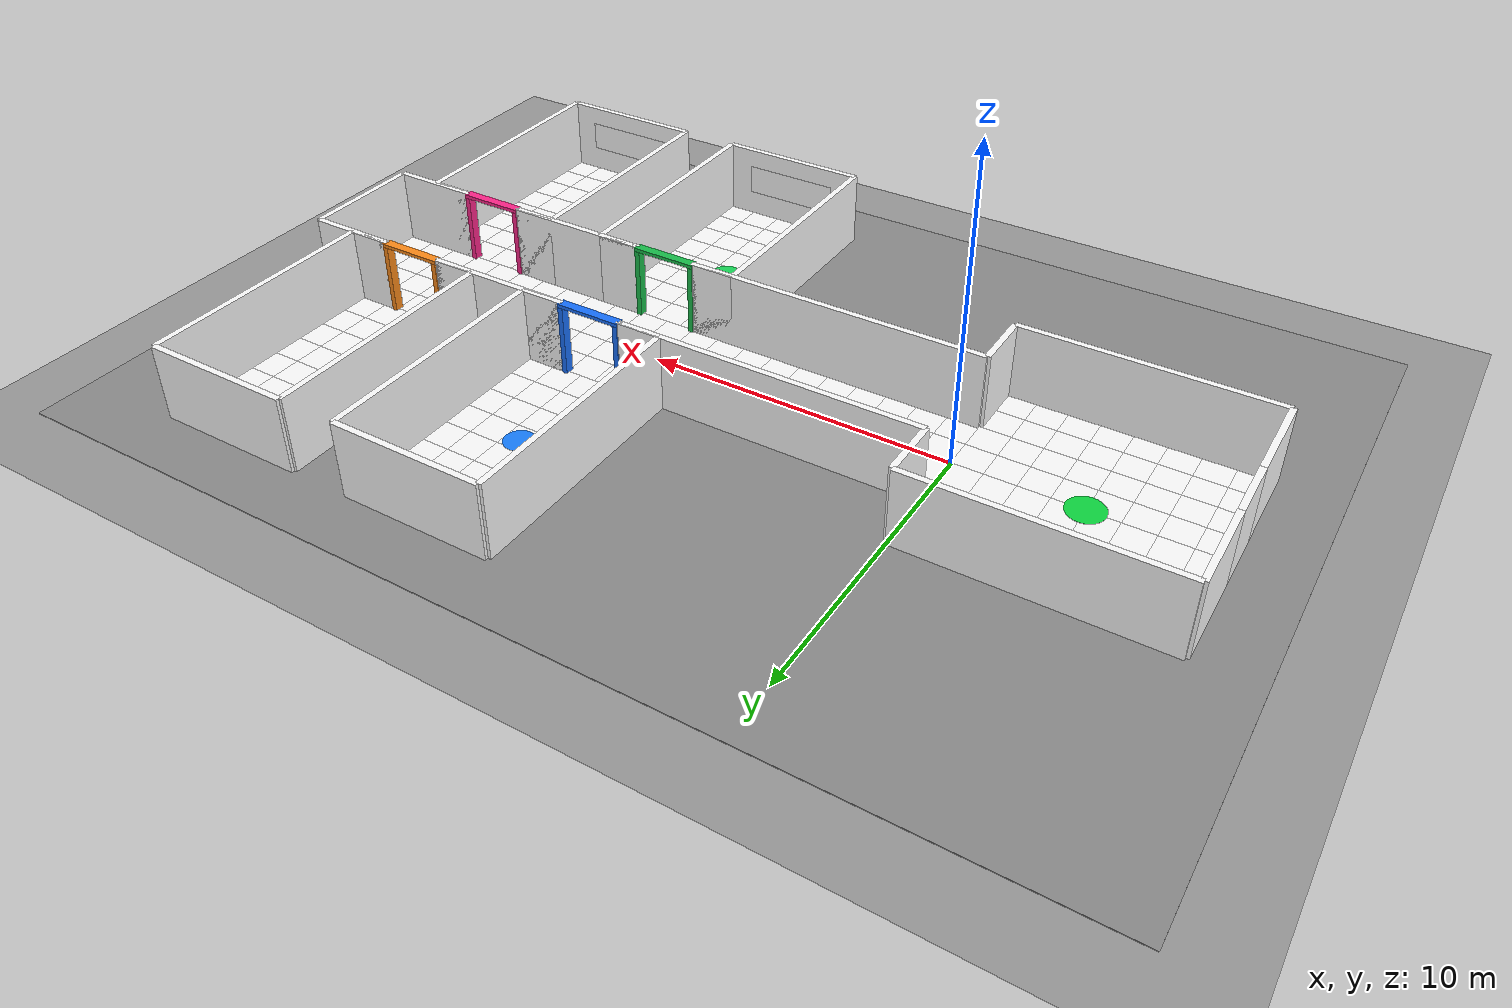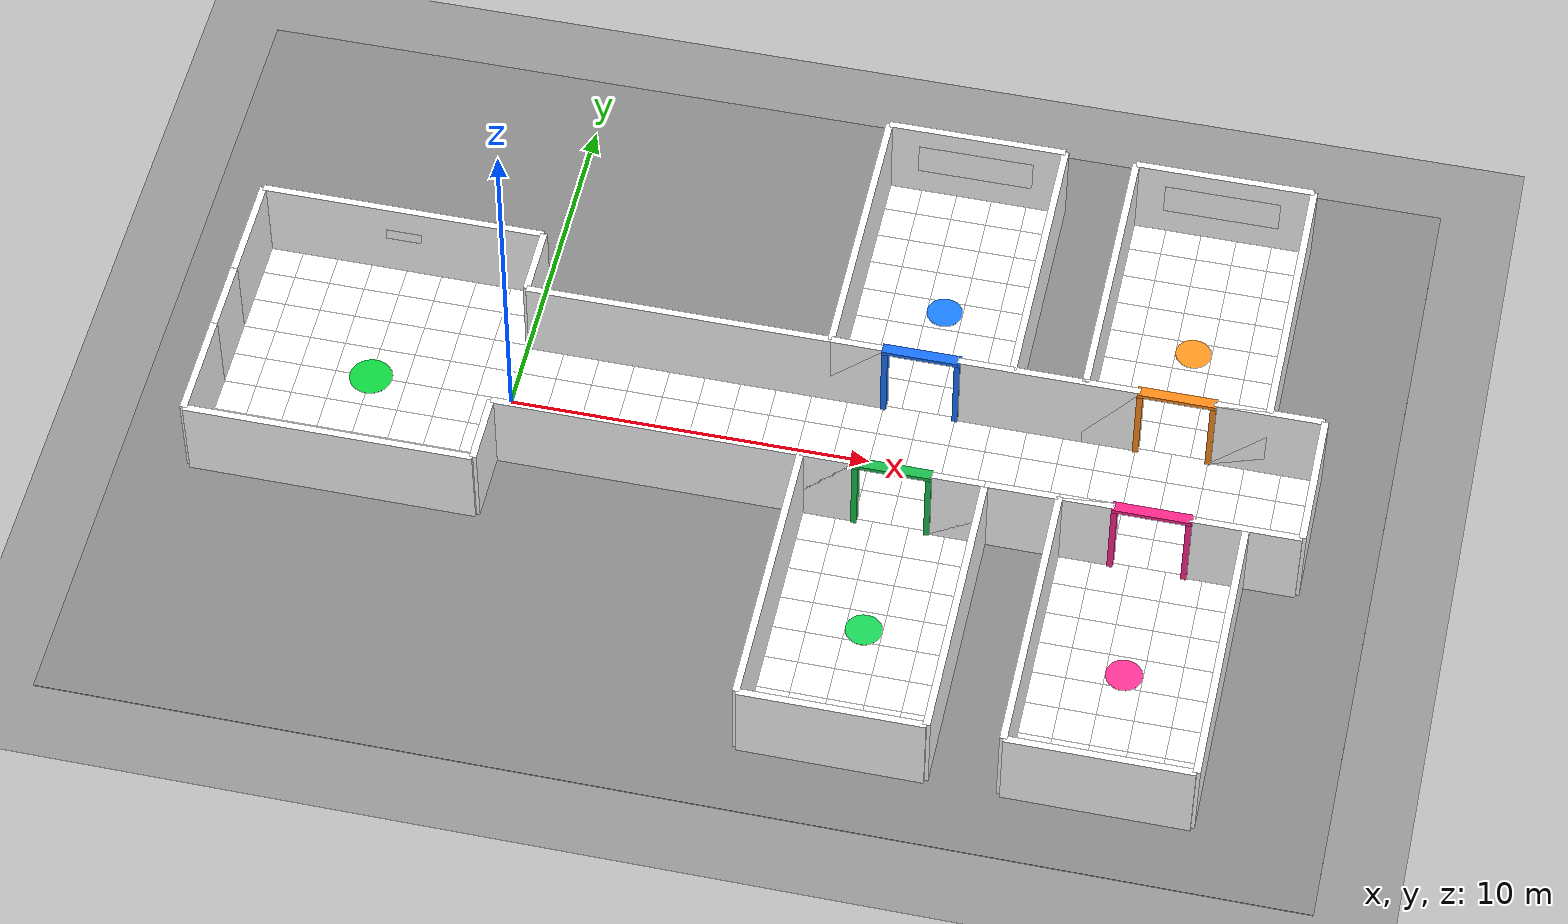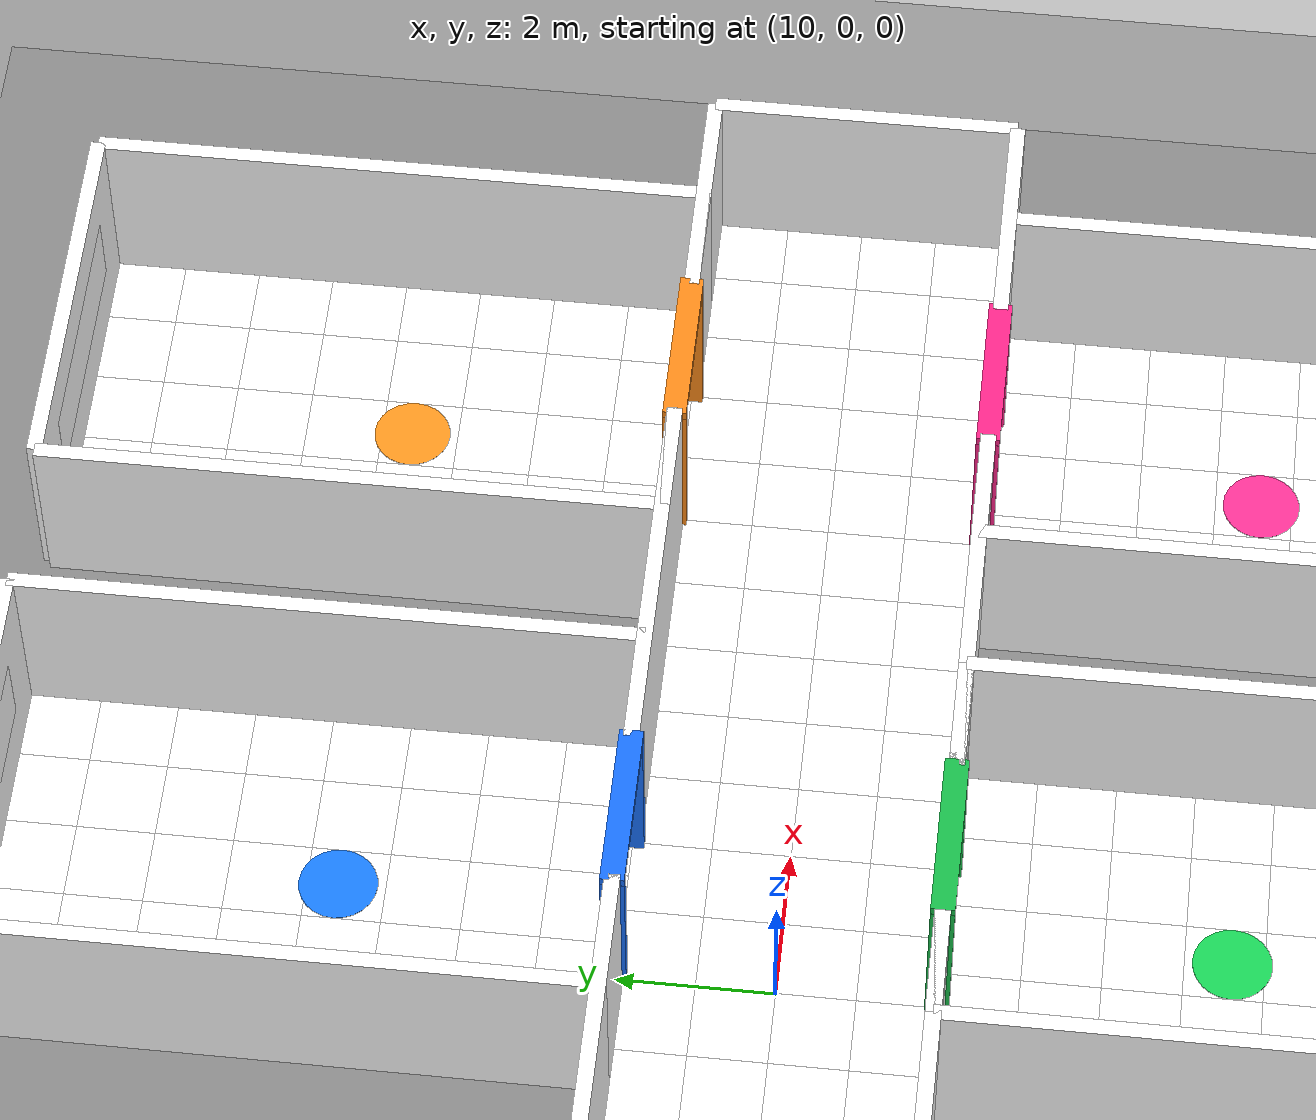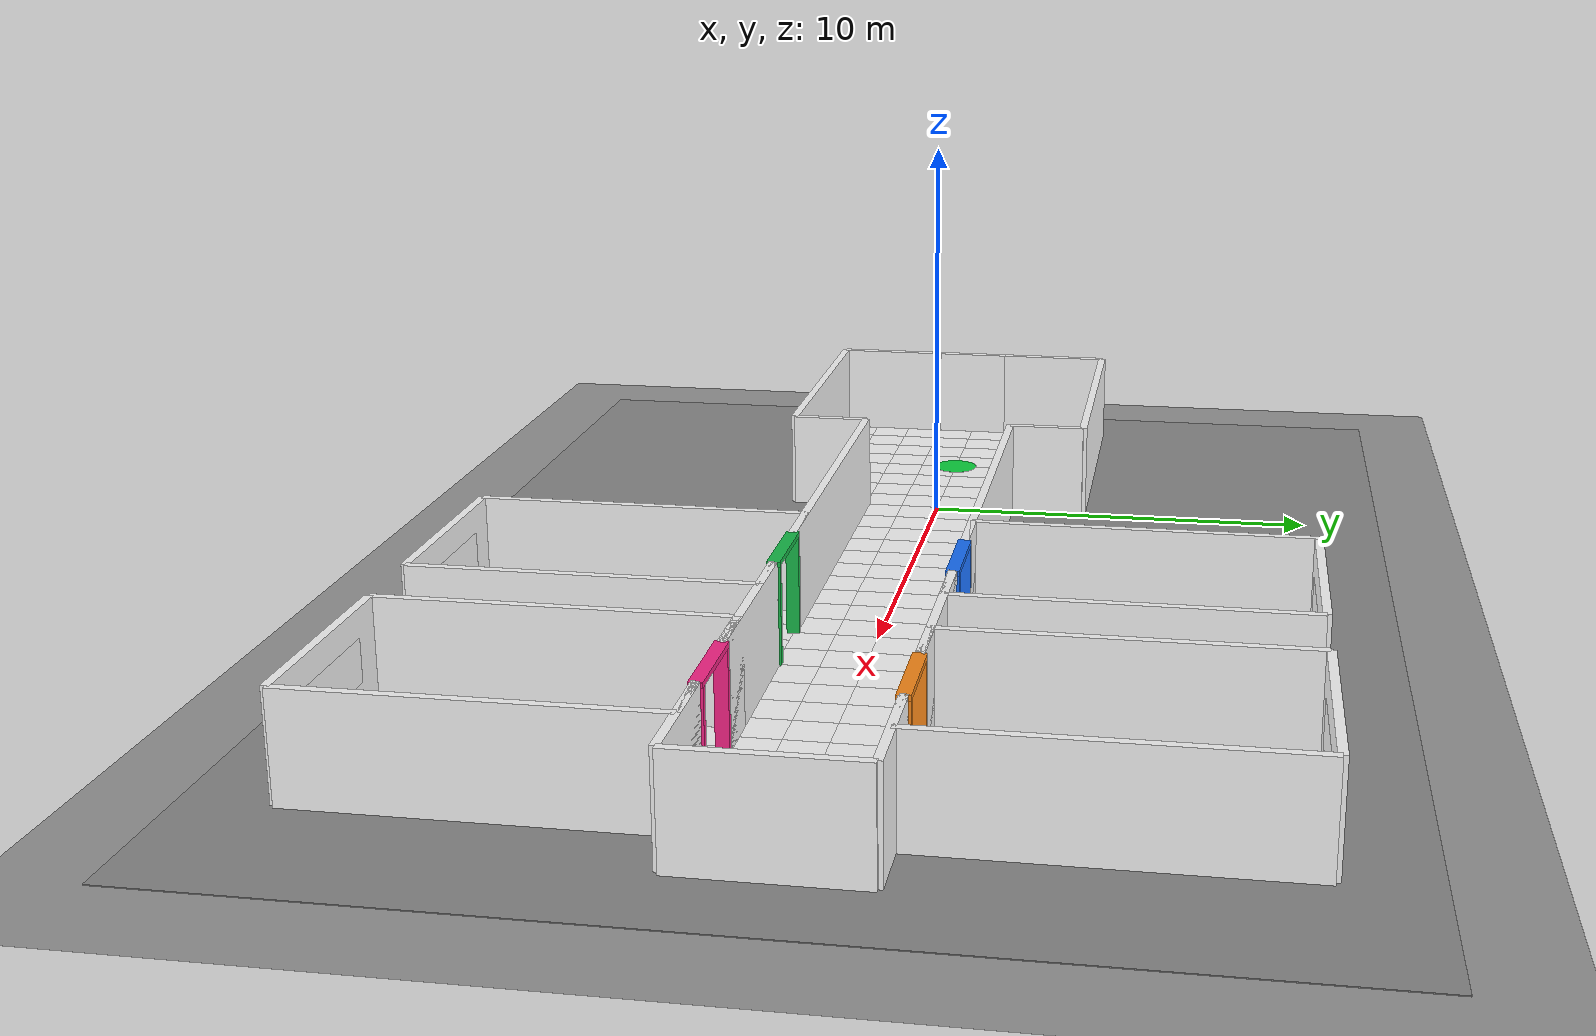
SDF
<sdf version="1.9">
 <world name="default">
  <plugin filename="gz-sim-physics-system" name="gz::sim::systems::Physics"/>
  <plugin filename="gz-sim-user-commands-system" name="gz::sim::systems::UserCommands"/>
  <plugin filename="gz-sim-scene-broadcaster-system" name="gz::sim::systems::SceneBroadcaster"/>
  <plugin filename="gz-sim-sensors-system" name="gz::sim::systems::Sensors">
   <render_engine>ogre2</render_engine>
  </plugin>
  <light name="sun" type="directional">
   <cast_shadows>false</cast_shadows>
   <pose>0 0 10 0 -0 0</pose>
   <diffuse>1.0 1.0 1.0 1</diffuse>
   <specular>0.2 0.2 0.2 1</specular>
   <attenuation>
    <range>1000</range>
    <constant>0.9</constant>
    <linear>0.01</linear>
    <quadratic>0.001</quadratic>
   </attenuation>
   <direction>-0.5 0.1 -0.9</direction>
  </light>
  <model name="ground_plane">
   <static>1</static>
   <link name="link">
    <collision name="collision">
     <geometry><plane><normal>0 0 1</normal><size>100 100</size></plane></geometry>
     <surface>
      <contact><collide_bitmask>65535</collide_bitmask></contact>
      <friction><ode><mu>100</mu><mu2>50</mu2></ode></friction>
     </surface>
    </collision>
    <visual name="visual">
     <cast_shadows>0</cast_shadows>
     <geometry><plane><normal>0 0 1</normal><size>100 100</size></plane></geometry>
     <material><ambient>0.6 0.6 0.6 1</ambient><diffuse>0.6 0.6 0.6 1</diffuse></material>
    </visual>
   </link>
  </model>
  <gravity>0 0 -9.8</gravity>
  <magnetic_field>6e-06 2.3e-05 -4.2e-05</magnetic_field>
  <atmosphere type="adiabatic"/>
  <physics name="default_physics" default="0" type="ode">
   <max_step_size>0.004</max_step_size>
   <real_time_factor>1</real_time_factor>
   <real_time_update_rate>250</real_time_update_rate>
  </physics>
  <scene>
   <grid>false</grid>
   <ambient>0.8 0.8 0.8 1</ambient>
   <background>0.9 0.9 0.9 1</background>
   <shadows>false</shadows>
  </scene>
  <audio><device>default</device></audio>
  <spherical_coordinates>
   <surface_model>EARTH_WGS84</surface_model>
   <latitude_deg>0</latitude_deg>
   <longitude_deg>0</longitude_deg>
   <elevation>0</elevation>
   <heading_deg>0</heading_deg>
  </spherical_coordinates>
  <model name="corridor_rooms">
   <static>true</static>
   <link name="link">
    <collision name="floor_col">
     <pose>7.0 0 0.01 0 0 0</pose>
     <geometry><box><size>34.0 24.0 0.02</size></box></geometry>
    </collision>
    <visual name="floor_vis">
     <pose>7.0 0 0.01 0 0 0</pose>
     <geometry><box><size>34.0 24.0 0.02</size></box></geometry>
     <material><ambient>0.55 0.55 0.55 1</ambient><diffuse>0.55 0.55 0.55 1</diffuse></material>
    </visual>
    <collision name="lobby_north_col">
     <pose>-4.0 4.0 1.25 0 0 0.0</pose>
     <geometry><box><size>8.0 0.2 2.5</size></box></geometry>
    </collision>
    <visual name="lobby_north_vis">
     <pose>-4.0 4.0 1.25 0 0 0.0</pose>
     <geometry><box><size>8.0 0.2 2.5</size></box></geometry>
     <material>
      <ambient>1 1 1 1</ambient>
      <diffuse>1 1 1 1</diffuse>
      <pbr>
       <metal>
        <albedo_map>materials/textures/wall.png</albedo_map>
        <metalness>0</metalness>
        <roughness>1</roughness>
       </metal>
      </pbr>
     </material>
    </visual>
    <collision name="lobby_south_col">
     <pose>-4.0 -4.0 1.25 0 0 0.0</pose>
     <geometry><box><size>8.0 0.2 2.5</size></box></geometry>
    </collision>
    <visual name="lobby_south_vis">
     <pose>-4.0 -4.0 1.25 0 0 0.0</pose>
     <geometry><box><size>8.0 0.2 2.5</size></box></geometry>
     <material>
      <ambient>1 1 1 1</ambient>
      <diffuse>1 1 1 1</diffuse>
      <pbr>
       <metal>
        <albedo_map>materials/textures/wall.png</albedo_map>
        <metalness>0</metalness>
        <roughness>1</roughness>
       </metal>
      </pbr>
     </material>
    </visual>
    <collision name="lobby_west_a_col">
     <pose>-8.0 2.5 1.25 0 0 0.0</pose>
     <geometry><box><size>0.2 3.0 2.5</size></box></geometry>
    </collision>
    <visual name="lobby_west_a_vis">
     <pose>-8.0 2.5 1.25 0 0 0.0</pose>
     <geometry><box><size>0.2 3.0 2.5</size></box></geometry>
     <material>
      <ambient>1 1 1 1</ambient>
      <diffuse>1 1 1 1</diffuse>
      <pbr>
       <metal>
        <albedo_map>materials/textures/wall.png</albedo_map>
        <metalness>0</metalness>
        <roughness>1</roughness>
       </metal>
      </pbr>
     </material>
    </visual>
    <collision name="lobby_west_b_col">
     <pose>-8.0 -2.5 1.25 0 0 0.0</pose>
     <geometry><box><size>0.2 3.0 2.5</size></box></geometry>
    </collision>
    <visual name="lobby_west_b_vis">
     <pose>-8.0 -2.5 1.25 0 0 0.0</pose>
     <geometry><box><size>0.2 3.0 2.5</size></box></geometry>
     <material>
      <ambient>1 1 1 1</ambient>
      <diffuse>1 1 1 1</diffuse>
      <pbr>
       <metal>
        <albedo_map>materials/textures/wall.png</albedo_map>
        <metalness>0</metalness>
        <roughness>1</roughness>
       </metal>
      </pbr>
     </material>
    </visual>
    <collision name="lobby_west_entrance_col">
     <pose>-8.0 0.0 1.25 0 0 0.0</pose>
     <geometry><box><size>0.2 2.0 2.5</size></box></geometry>
    </collision>
    <visual name="lobby_west_entrance_vis">
     <pose>-8.0 0.0 1.25 0 0 0.0</pose>
     <geometry><box><size>0.2 2.0 2.5</size></box></geometry>
     <material>
      <ambient>1 1 1 1</ambient>
      <diffuse>1 1 1 1</diffuse>
      <pbr>
       <metal>
        <albedo_map>materials/textures/wall.png</albedo_map>
        <metalness>0</metalness>
        <roughness>1</roughness>
       </metal>
      </pbr>
     </material>
    </visual>
    <collision name="lobby_east_a_col">
     <pose>0.0 3.0 1.25 0 0 0.0</pose>
     <geometry><box><size>0.2 2.0 2.5</size></box></geometry>
    </collision>
    <visual name="lobby_east_a_vis">
     <pose>0.0 3.0 1.25 0 0 0.0</pose>
     <geometry><box><size>0.2 2.0 2.5</size></box></geometry>
     <material>
      <ambient>1 1 1 1</ambient>
      <diffuse>1 1 1 1</diffuse>
      <pbr>
       <metal>
        <albedo_map>materials/textures/wall.png</albedo_map>
        <metalness>0</metalness>
        <roughness>1</roughness>
       </metal>
      </pbr>
     </material>
    </visual>
    <collision name="lobby_east_b_col">
     <pose>0.0 -3.0 1.25 0 0 0.0</pose>
     <geometry><box><size>0.2 2.0 2.5</size></box></geometry>
    </collision>
    <visual name="lobby_east_b_vis">
     <pose>0.0 -3.0 1.25 0 0 0.0</pose>
     <geometry><box><size>0.2 2.0 2.5</size></box></geometry>
     <material>
      <ambient>1 1 1 1</ambient>
      <diffuse>1 1 1 1</diffuse>
      <pbr>
       <metal>
        <albedo_map>materials/textures/wall.png</albedo_map>
        <metalness>0</metalness>
        <roughness>1</roughness>
       </metal>
      </pbr>
     </material>
    </visual>
    <collision name="corridor_north_0_col">
     <pose>5.0 2.0 1.25 0 0 0.0</pose>
     <geometry><box><size>10.0 0.2 2.5</size></box></geometry>
    </collision>
    <visual name="corridor_north_0_vis">
     <pose>5.0 2.0 1.25 0 0 0.0</pose>
     <geometry><box><size>10.0 0.2 2.5</size></box></geometry>
     <material>
      <ambient>1 1 1 1</ambient>
      <diffuse>1 1 1 1</diffuse>
      <pbr>
       <metal>
        <albedo_map>materials/textures/wall.png</albedo_map>
        <metalness>0</metalness>
        <roughness>1</roughness>
       </metal>
      </pbr>
     </material>
    </visual>
    <collision name="corridor_north_1_col">
     <pose>14.5 2.0 1.25 0 0 0.0</pose>
     <geometry><box><size>5.0 0.2 2.5</size></box></geometry>
    </collision>
    <visual name="corridor_north_1_vis">
     <pose>14.5 2.0 1.25 0 0 0.0</pose>
     <geometry><box><size>5.0 0.2 2.5</size></box></geometry>
     <material>
      <ambient>1 1 1 1</ambient>
      <diffuse>1 1 1 1</diffuse>
      <pbr>
       <metal>
        <albedo_map>materials/textures/wall.png</albedo_map>
        <metalness>0</metalness>
        <roughness>1</roughness>
       </metal>
      </pbr>
     </material>
    </visual>
    <collision name="corridor_north_2_col">
     <pose>20.5 2.0 1.25 0 0 0.0</pose>
     <geometry><box><size>3.0 0.2 2.5</size></box></geometry>
    </collision>
    <visual name="corridor_north_2_vis">
     <pose>20.5 2.0 1.25 0 0 0.0</pose>
     <geometry><box><size>3.0 0.2 2.5</size></box></geometry>
     <material>
      <ambient>1 1 1 1</ambient>
      <diffuse>1 1 1 1</diffuse>
      <pbr>
       <metal>
        <albedo_map>materials/textures/wall.png</albedo_map>
        <metalness>0</metalness>
        <roughness>1</roughness>
       </metal>
      </pbr>
     </material>
    </visual>
    <collision name="corridor_south_0_col">
     <pose>5.0 -2.0 1.25 0 0 0.0</pose>
     <geometry><box><size>10.0 0.2 2.5</size></box></geometry>
    </collision>
    <visual name="corridor_south_0_vis">
     <pose>5.0 -2.0 1.25 0 0 0.0</pose>
     <geometry><box><size>10.0 0.2 2.5</size></box></geometry>
     <material>
      <ambient>1 1 1 1</ambient>
      <diffuse>1 1 1 1</diffuse>
      <pbr>
       <metal>
        <albedo_map>materials/textures/wall.png</albedo_map>
        <metalness>0</metalness>
        <roughness>1</roughness>
       </metal>
      </pbr>
     </material>
    </visual>
    <collision name="corridor_south_1_col">
     <pose>14.5 -2.0 1.25 0 0 0.0</pose>
     <geometry><box><size>5.0 0.2 2.5</size></box></geometry>
    </collision>
    <visual name="corridor_south_1_vis">
     <pose>14.5 -2.0 1.25 0 0 0.0</pose>
     <geometry><box><size>5.0 0.2 2.5</size></box></geometry>
     <material>
      <ambient>1 1 1 1</ambient>
      <diffuse>1 1 1 1</diffuse>
      <pbr>
       <metal>
        <albedo_map>materials/textures/wall.png</albedo_map>
        <metalness>0</metalness>
        <roughness>1</roughness>
       </metal>
      </pbr>
     </material>
    </visual>
    <collision name="corridor_south_2_col">
     <pose>20.5 -2.0 1.25 0 0 0.0</pose>
     <geometry><box><size>3.0 0.2 2.5</size></box></geometry>
    </collision>
    <visual name="corridor_south_2_vis">
     <pose>20.5 -2.0 1.25 0 0 0.0</pose>
     <geometry><box><size>3.0 0.2 2.5</size></box></geometry>
     <material>
      <ambient>1 1 1 1</ambient>
      <diffuse>1 1 1 1</diffuse>
      <pbr>
       <metal>
        <albedo_map>materials/textures/wall.png</albedo_map>
        <metalness>0</metalness>
        <roughness>1</roughness>
       </metal>
      </pbr>
     </material>
    </visual>
    <collision name="corridor_east_end_col">
     <pose>22.0 0.0 1.25 0 0 0.0</pose>
     <geometry><box><size>0.2 4.0 2.5</size></box></geometry>
    </collision>
    <visual name="corridor_east_end_vis">
     <pose>22.0 0.0 1.25 0 0 0.0</pose>
     <geometry><box><size>0.2 4.0 2.5</size></box></geometry>
     <material>
      <ambient>1 1 1 1</ambient>
      <diffuse>1 1 1 1</diffuse>
      <pbr>
       <metal>
        <albedo_map>materials/textures/wall.png</albedo_map>
        <metalness>0</metalness>
        <roughness>1</roughness>
       </metal>
      </pbr>
     </material>
    </visual>
    <collision name="room_A_doorwall_a_col">
     <pose>9.25 2.0 1.25 0 0 0.0</pose>
     <geometry><box><size>1.5 0.2 2.5</size></box></geometry>
    </collision>
    <visual name="room_A_doorwall_a_vis">
     <pose>9.25 2.0 1.25 0 0 0.0</pose>
     <geometry><box><size>1.5 0.2 2.5</size></box></geometry>
     <material>
      <ambient>1 1 1 1</ambient>
      <diffuse>1 1 1 1</diffuse>
      <pbr>
       <metal>
        <albedo_map>materials/textures/wall.png</albedo_map>
        <metalness>0</metalness>
        <roughness>1</roughness>
       </metal>
      </pbr>
     </material>
    </visual>
    <collision name="room_A_doorwall_b_col">
     <pose>12.75 2.0 1.25 0 0 0.0</pose>
     <geometry><box><size>1.5 0.2 2.5</size></box></geometry>
    </collision>
    <visual name="room_A_doorwall_b_vis">
     <pose>12.75 2.0 1.25 0 0 0.0</pose>
     <geometry><box><size>1.5 0.2 2.5</size></box></geometry>
     <material>
      <ambient>1 1 1 1</ambient>
      <diffuse>1 1 1 1</diffuse>
      <pbr>
       <metal>
        <albedo_map>materials/textures/wall.png</albedo_map>
        <metalness>0</metalness>
        <roughness>1</roughness>
       </metal>
      </pbr>
     </material>
    </visual>
    <collision name="room_A_backwall_col">
     <pose>11.0 10.0 1.25 0 0 0.0</pose>
     <geometry><box><size>5.0 0.2 2.5</size></box></geometry>
    </collision>
    <visual name="room_A_backwall_vis">
     <pose>11.0 10.0 1.25 0 0 0.0</pose>
     <geometry><box><size>5.0 0.2 2.5</size></box></geometry>
     <material>
      <ambient>1 1 1 1</ambient>
      <diffuse>1 1 1 1</diffuse>
      <pbr>
       <metal>
        <albedo_map>materials/textures/wall.png</albedo_map>
        <metalness>0</metalness>
        <roughness>1</roughness>
       </metal>
      </pbr>
     </material>
    </visual>
    <collision name="room_A_sidewall_1_col">
     <pose>8.5 6.0 1.25 0 0 0.0</pose>
     <geometry><box><size>0.2 8.0 2.5</size></box></geometry>
    </collision>
    <visual name="room_A_sidewall_1_vis">
     <pose>8.5 6.0 1.25 0 0 0.0</pose>
     <geometry><box><size>0.2 8.0 2.5</size></box></geometry>
     <material>
      <ambient>1 1 1 1</ambient>
      <diffuse>1 1 1 1</diffuse>
      <pbr>
       <metal>
        <albedo_map>materials/textures/wall.png</albedo_map>
        <metalness>0</metalness>
        <roughness>1</roughness>
       </metal>
      </pbr>
     </material>
    </visual>
    <collision name="room_A_sidewall_2_col">
     <pose>13.5 6.0 1.25 0 0 0.0</pose>
     <geometry><box><size>0.2 8.0 2.5</size></box></geometry>
    </collision>
    <visual name="room_A_sidewall_2_vis">
     <pose>13.5 6.0 1.25 0 0 0.0</pose>
     <geometry><box><size>0.2 8.0 2.5</size></box></geometry>
     <material>
      <ambient>1 1 1 1</ambient>
      <diffuse>1 1 1 1</diffuse>
      <pbr>
       <metal>
        <albedo_map>materials/textures/wall.png</albedo_map>
        <metalness>0</metalness>
        <roughness>1</roughness>
       </metal>
      </pbr>
     </material>
    </visual>
    <collision name="room_B_doorwall_a_col">
     <pose>9.25 -2.0 1.25 0 0 0.0</pose>
     <geometry><box><size>1.5 0.2 2.5</size></box></geometry>
    </collision>
    <visual name="room_B_doorwall_a_vis">
     <pose>9.25 -2.0 1.25 0 0 0.0</pose>
     <geometry><box><size>1.5 0.2 2.5</size></box></geometry>
     <material>
      <ambient>1 1 1 1</ambient>
      <diffuse>1 1 1 1</diffuse>
      <pbr>
       <metal>
        <albedo_map>materials/textures/wall.png</albedo_map>
        <metalness>0</metalness>
        <roughness>1</roughness>
       </metal>
      </pbr>
     </material>
    </visual>
    <collision name="room_B_doorwall_b_col">
     <pose>12.75 -2.0 1.25 0 0 0.0</pose>
     <geometry><box><size>1.5 0.2 2.5</size></box></geometry>
    </collision>
    <visual name="room_B_doorwall_b_vis">
     <pose>12.75 -2.0 1.25 0 0 0.0</pose>
     <geometry><box><size>1.5 0.2 2.5</size></box></geometry>
     <material>
      <ambient>1 1 1 1</ambient>
      <diffuse>1 1 1 1</diffuse>
      <pbr>
       <metal>
        <albedo_map>materials/textures/wall.png</albedo_map>
        <metalness>0</metalness>
        <roughness>1</roughness>
       </metal>
      </pbr>
     </material>
    </visual>
    <collision name="room_B_backwall_col">
     <pose>11.0 -10.0 1.25 0 0 0.0</pose>
     <geometry><box><size>5.0 0.2 2.5</size></box></geometry>
    </collision>
    <visual name="room_B_backwall_vis">
     <pose>11.0 -10.0 1.25 0 0 0.0</pose>
     <geometry><box><size>5.0 0.2 2.5</size></box></geometry>
     <material>
      <ambient>1 1 1 1</ambient>
      <diffuse>1 1 1 1</diffuse>
      <pbr>
       <metal>
        <albedo_map>materials/textures/wall.png</albedo_map>
        <metalness>0</metalness>
        <roughness>1</roughness>
       </metal>
      </pbr>
     </material>
    </visual>
    <collision name="room_B_sidewall_1_col">
     <pose>8.5 -6.0 1.25 0 0 0.0</pose>
     <geometry><box><size>0.2 8.0 2.5</size></box></geometry>
    </collision>
    <visual name="room_B_sidewall_1_vis">
     <pose>8.5 -6.0 1.25 0 0 0.0</pose>
     <geometry><box><size>0.2 8.0 2.5</size></box></geometry>
     <material>
      <ambient>1 1 1 1</ambient>
      <diffuse>1 1 1 1</diffuse>
      <pbr>
       <metal>
        <albedo_map>materials/textures/wall.png</albedo_map>
        <metalness>0</metalness>
        <roughness>1</roughness>
       </metal>
      </pbr>
     </material>
    </visual>
    <collision name="room_B_sidewall_2_col">
     <pose>13.5 -6.0 1.25 0 0 0.0</pose>
     <geometry><box><size>0.2 8.0 2.5</size></box></geometry>
    </collision>
    <visual name="room_B_sidewall_2_vis">
     <pose>13.5 -6.0 1.25 0 0 0.0</pose>
     <geometry><box><size>0.2 8.0 2.5</size></box></geometry>
     <material>
      <ambient>1 1 1 1</ambient>
      <diffuse>1 1 1 1</diffuse>
      <pbr>
       <metal>
        <albedo_map>materials/textures/wall.png</albedo_map>
        <metalness>0</metalness>
        <roughness>1</roughness>
       </metal>
      </pbr>
     </material>
    </visual>
    <collision name="room_C_doorwall_a_col">
     <pose>16.25 2.0 1.25 0 0 0.0</pose>
     <geometry><box><size>1.5 0.2 2.5</size></box></geometry>
    </collision>
    <visual name="room_C_doorwall_a_vis">
     <pose>16.25 2.0 1.25 0 0 0.0</pose>
     <geometry><box><size>1.5 0.2 2.5</size></box></geometry>
     <material>
      <ambient>1 1 1 1</ambient>
      <diffuse>1 1 1 1</diffuse>
      <pbr>
       <metal>
        <albedo_map>materials/textures/wall.png</albedo_map>
        <metalness>0</metalness>
        <roughness>1</roughness>
       </metal>
      </pbr>
     </material>
    </visual>
    <collision name="room_C_doorwall_b_col">
     <pose>19.75 2.0 1.25 0 0 0.0</pose>
     <geometry><box><size>1.5 0.2 2.5</size></box></geometry>
    </collision>
    <visual name="room_C_doorwall_b_vis">
     <pose>19.75 2.0 1.25 0 0 0.0</pose>
     <geometry><box><size>1.5 0.2 2.5</size></box></geometry>
     <material>
      <ambient>1 1 1 1</ambient>
      <diffuse>1 1 1 1</diffuse>
      <pbr>
       <metal>
        <albedo_map>materials/textures/wall.png</albedo_map>
        <metalness>0</metalness>
        <roughness>1</roughness>
       </metal>
      </pbr>
     </material>
    </visual>
    <collision name="room_C_backwall_col">
     <pose>18.0 10.0 1.25 0 0 0.0</pose>
     <geometry><box><size>5.0 0.2 2.5</size></box></geometry>
    </collision>
    <visual name="room_C_backwall_vis">
     <pose>18.0 10.0 1.25 0 0 0.0</pose>
     <geometry><box><size>5.0 0.2 2.5</size></box></geometry>
     <material>
      <ambient>1 1 1 1</ambient>
      <diffuse>1 1 1 1</diffuse>
      <pbr>
       <metal>
        <albedo_map>materials/textures/wall.png</albedo_map>
        <metalness>0</metalness>
        <roughness>1</roughness>
       </metal>
      </pbr>
     </material>
    </visual>
    <collision name="room_C_sidewall_1_col">
     <pose>15.5 6.0 1.25 0 0 0.0</pose>
     <geometry><box><size>0.2 8.0 2.5</size></box></geometry>
    </collision>
    <visual name="room_C_sidewall_1_vis">
     <pose>15.5 6.0 1.25 0 0 0.0</pose>
     <geometry><box><size>0.2 8.0 2.5</size></box></geometry>
     <material>
      <ambient>1 1 1 1</ambient>
      <diffuse>1 1 1 1</diffuse>
      <pbr>
       <metal>
        <albedo_map>materials/textures/wall.png</albedo_map>
        <metalness>0</metalness>
        <roughness>1</roughness>
       </metal>
      </pbr>
     </material>
    </visual>
    <collision name="room_C_sidewall_2_col">
     <pose>20.5 6.0 1.25 0 0 0.0</pose>
     <geometry><box><size>0.2 8.0 2.5</size></box></geometry>
    </collision>
    <visual name="room_C_sidewall_2_vis">
     <pose>20.5 6.0 1.25 0 0 0.0</pose>
     <geometry><box><size>0.2 8.0 2.5</size></box></geometry>
     <material>
      <ambient>1 1 1 1</ambient>
      <diffuse>1 1 1 1</diffuse>
      <pbr>
       <metal>
        <albedo_map>materials/textures/wall.png</albedo_map>
        <metalness>0</metalness>
        <roughness>1</roughness>
       </metal>
      </pbr>
     </material>
    </visual>
    <collision name="room_D_doorwall_a_col">
     <pose>16.25 -2.0 1.25 0 0 0.0</pose>
     <geometry><box><size>1.5 0.2 2.5</size></box></geometry>
    </collision>
    <visual name="room_D_doorwall_a_vis">
     <pose>16.25 -2.0 1.25 0 0 0.0</pose>
     <geometry><box><size>1.5 0.2 2.5</size></box></geometry>
     <material>
      <ambient>1 1 1 1</ambient>
      <diffuse>1 1 1 1</diffuse>
      <pbr>
       <metal>
        <albedo_map>materials/textures/wall.png</albedo_map>
        <metalness>0</metalness>
        <roughness>1</roughness>
       </metal>
      </pbr>
     </material>
    </visual>
    <collision name="room_D_doorwall_b_col">
     <pose>19.75 -2.0 1.25 0 0 0.0</pose>
     <geometry><box><size>1.5 0.2 2.5</size></box></geometry>
    </collision>
    <visual name="room_D_doorwall_b_vis">
     <pose>19.75 -2.0 1.25 0 0 0.0</pose>
     <geometry><box><size>1.5 0.2 2.5</size></box></geometry>
     <material>
      <ambient>1 1 1 1</ambient>
      <diffuse>1 1 1 1</diffuse>
      <pbr>
       <metal>
        <albedo_map>materials/textures/wall.png</albedo_map>
        <metalness>0</metalness>
        <roughness>1</roughness>
       </metal>
      </pbr>
     </material>
    </visual>
    <collision name="room_D_backwall_col">
     <pose>18.0 -10.0 1.25 0 0 0.0</pose>
     <geometry><box><size>5.0 0.2 2.5</size></box></geometry>
    </collision>
    <visual name="room_D_backwall_vis">
     <pose>18.0 -10.0 1.25 0 0 0.0</pose>
     <geometry><box><size>5.0 0.2 2.5</size></box></geometry>
     <material>
      <ambient>1 1 1 1</ambient>
      <diffuse>1 1 1 1</diffuse>
      <pbr>
       <metal>
        <albedo_map>materials/textures/wall.png</albedo_map>
        <metalness>0</metalness>
        <roughness>1</roughness>
       </metal>
      </pbr>
     </material>
    </visual>
    <collision name="room_D_sidewall_1_col">
     <pose>15.5 -6.0 1.25 0 0 0.0</pose>
     <geometry><box><size>0.2 8.0 2.5</size></box></geometry>
    </collision>
    <visual name="room_D_sidewall_1_vis">
     <pose>15.5 -6.0 1.25 0 0 0.0</pose>
     <geometry><box><size>0.2 8.0 2.5</size></box></geometry>
     <material>
      <ambient>1 1 1 1</ambient>
      <diffuse>1 1 1 1</diffuse>
      <pbr>
       <metal>
        <albedo_map>materials/textures/wall.png</albedo_map>
        <metalness>0</metalness>
        <roughness>1</roughness>
       </metal>
      </pbr>
     </material>
    </visual>
    <collision name="room_D_sidewall_2_col">
     <pose>20.5 -6.0 1.25 0 0 0.0</pose>
     <geometry><box><size>0.2 8.0 2.5</size></box></geometry>
    </collision>
    <visual name="room_D_sidewall_2_vis">
     <pose>20.5 -6.0 1.25 0 0 0.0</pose>
     <geometry><box><size>0.2 8.0 2.5</size></box></geometry>
     <material>
      <ambient>1 1 1 1</ambient>
      <diffuse>1 1 1 1</diffuse>
      <pbr>
       <metal>
        <albedo_map>materials/textures/wall.png</albedo_map>
        <metalness>0</metalness>
        <roughness>1</roughness>
       </metal>
      </pbr>
     </material>
    </visual>
    <visual name="plate_A_vis">
     <pose>11.0 9.89 1.375 1.5708 0 0.0</pose>
     <geometry><plane><size>3.25 1.0</size></plane></geometry>
     <material>
      <ambient>1 1 1 1</ambient>
      <diffuse>1 1 1 1</diffuse>
      <pbr>
       <metal>
        <albedo_map>materials/textures/sala_a.png</albedo_map>
        <metalness>0.0</metalness>
        <roughness>1.0</roughness>
       </metal>
      </pbr>
     </material>
    </visual>
    <visual name="plate_B_vis">
     <pose>11.0 -9.89 1.375 1.5708 0 3.14159265</pose>
     <geometry><plane><size>3.25 1.0</size></plane></geometry>
     <material>
      <ambient>1 1 1 1</ambient>
      <diffuse>1 1 1 1</diffuse>
      <pbr>
       <metal>
        <albedo_map>materials/textures/sala_b.png</albedo_map>
        <metalness>0.0</metalness>
        <roughness>1.0</roughness>
       </metal>
      </pbr>
     </material>
    </visual>
    <visual name="plate_C_vis">
     <pose>18.0 9.89 1.375 1.5708 0 0.0</pose>
     <geometry><plane><size>3.25 1.0</size></plane></geometry>
     <material>
      <ambient>1 1 1 1</ambient>
      <diffuse>1 1 1 1</diffuse>
      <pbr>
       <metal>
        <albedo_map>materials/textures/sala_c.png</albedo_map>
        <metalness>0.0</metalness>
        <roughness>1.0</roughness>
       </metal>
      </pbr>
     </material>
    </visual>
    <visual name="plate_D_vis">
     <pose>18.0 -9.89 1.375 1.5708 0 3.14159265</pose>
     <geometry><plane><size>3.25 1.0</size></plane></geometry>
     <material>
      <ambient>1 1 1 1</ambient>
      <diffuse>1 1 1 1</diffuse>
      <pbr>
       <metal>
        <albedo_map>materials/textures/sala_d.png</albedo_map>
        <metalness>0.0</metalness>
        <roughness>1.0</roughness>
       </metal>
      </pbr>
     </material>
    </visual>
   </link>
  </model>
  <model name="checkpoint_a">
   <static>true</static>
   <link name="link">
    <visual name="vis">
     <pose>11 5.6 0.02 0 0 0</pose>
     <geometry><cylinder><radius>0.5</radius><length>0.04</length></cylinder></geometry>
     <material>
      <ambient>0.10 0.45 1.00 1</ambient>
      <diffuse>0.10 0.50 1.00 1</diffuse>
      <emissive>0.05 0.22 0.55 1</emissive>
     </material>
    </visual>
   </link>
  </model>
  <model name="checkpoint_b">
   <static>true</static>
   <link name="link">
    <visual name="vis">
     <pose>11 -5.6 0.02 0 0 0</pose>
     <geometry><cylinder><radius>0.5</radius><length>0.04</length></cylinder></geometry>
     <material>
      <ambient>0.10 0.75 0.30 1</ambient>
      <diffuse>0.10 0.85 0.35 1</diffuse>
      <emissive>0.05 0.40 0.16 1</emissive>
     </material>
    </visual>
   </link>
  </model>
  <model name="checkpoint_c">
   <static>true</static>
   <link name="link">
    <visual name="vis">
     <pose>18 5.6 0.02 0 0 0</pose>
     <geometry><cylinder><radius>0.5</radius><length>0.04</length></cylinder></geometry>
     <material>
      <ambient>1.00 0.55 0.10 1</ambient>
      <diffuse>1.00 0.60 0.12 1</diffuse>
      <emissive>0.50 0.28 0.05 1</emissive>
     </material>
    </visual>
   </link>
  </model>
  <model name="checkpoint_d">
   <static>true</static>
   <link name="link">
    <visual name="vis">
     <pose>18 -5.6 0.02 0 0 0</pose>
     <geometry><cylinder><radius>0.5</radius><length>0.04</length></cylinder></geometry>
     <material>
      <ambient>1.00 0.15 0.55 1</ambient>
      <diffuse>1.00 0.20 0.60 1</diffuse>
      <emissive>0.50 0.08 0.28 1</emissive>
     </material>
    </visual>
   </link>
  </model>
  <model name="home_base">
   <static>true</static>
   <link name="link">
    <visual name="disk">
     <pose>-4.0 0 0.02 0 0 0</pose>
     <geometry><cylinder><radius>0.6</radius><length>0.04</length></cylinder></geometry>
     <material>
      <ambient>0.05 0.75 0.2 1</ambient>
      <diffuse>0.05 0.85 0.25 1</diffuse>
      <emissive>0.02 0.3 0.08 1</emissive>
     </material>
    </visual>
    <visual name="ring">
     <pose>-4.0 0 0.015 0 0 0</pose>
     <geometry><cylinder><radius>0.75</radius><length>0.03</length></cylinder></geometry>
     <material><ambient>0.95 0.95 0.95 1</ambient><diffuse>1 1 1 1</diffuse></material>
    </visual>
   </link>
  </model>
  <model name="deco_arco_A">
   <static>true</static>
   <link name="link">
    <visual name="jamb_l">
     <pose>10.0 2.0 1.19 0 0 0</pose>
     <geometry><box><size>0.16 0.30 2.38</size></box></geometry>
     <material><ambient>0.10 0.45 1.00 1</ambient><diffuse>0.10 0.45 1.00 1</diffuse></material>
    </visual>
    <visual name="jamb_r">
     <pose>12.0 2.0 1.19 0 0 0</pose>
     <geometry><box><size>0.16 0.30 2.38</size></box></geometry>
     <material><ambient>0.10 0.45 1.00 1</ambient><diffuse>0.10 0.45 1.00 1</diffuse></material>
    </visual>
    <visual name="lintel">
     <pose>11.0 2.0 2.44 0 0 0</pose>
     <geometry><box><size>2.16 0.30 0.12</size></box></geometry>
     <material>
      <ambient>0.10 0.45 1.00 1</ambient>
      <diffuse>0.10 0.45 1.00 1</diffuse>
      <emissive>0.04 0.18 0.40 1</emissive>
     </material>
    </visual>
   </link>
  </model>
  <model name="deco_arco_B">
   <static>true</static>
   <link name="link">
    <visual name="jamb_l">
     <pose>10.0 -2.0 1.19 0 0 0</pose>
     <geometry><box><size>0.16 0.30 2.38</size></box></geometry>
     <material><ambient>0.10 0.75 0.30 1</ambient><diffuse>0.10 0.75 0.30 1</diffuse></material>
    </visual>
    <visual name="jamb_r">
     <pose>12.0 -2.0 1.19 0 0 0</pose>
     <geometry><box><size>0.16 0.30 2.38</size></box></geometry>
     <material><ambient>0.10 0.75 0.30 1</ambient><diffuse>0.10 0.75 0.30 1</diffuse></material>
    </visual>
    <visual name="lintel">
     <pose>11.0 -2.0 2.44 0 0 0</pose>
     <geometry><box><size>2.16 0.30 0.12</size></box></geometry>
     <material>
      <ambient>0.10 0.75 0.30 1</ambient>
      <diffuse>0.10 0.75 0.30 1</diffuse>
      <emissive>0.04 0.30 0.12 1</emissive>
     </material>
    </visual>
   </link>
  </model>
  <model name="deco_arco_C">
   <static>true</static>
   <link name="link">
    <visual name="jamb_l">
     <pose>17.0 2.0 1.19 0 0 0</pose>
     <geometry><box><size>0.16 0.30 2.38</size></box></geometry>
     <material><ambient>1.00 0.55 0.10 1</ambient><diffuse>1.00 0.55 0.10 1</diffuse></material>
    </visual>
    <visual name="jamb_r">
     <pose>19.0 2.0 1.19 0 0 0</pose>
     <geometry><box><size>0.16 0.30 2.38</size></box></geometry>
     <material><ambient>1.00 0.55 0.10 1</ambient><diffuse>1.00 0.55 0.10 1</diffuse></material>
    </visual>
    <visual name="lintel">
     <pose>18.0 2.0 2.44 0 0 0</pose>
     <geometry><box><size>2.16 0.30 0.12</size></box></geometry>
     <material>
      <ambient>1.00 0.55 0.10 1</ambient>
      <diffuse>1.00 0.55 0.10 1</diffuse>
      <emissive>0.40 0.22 0.04 1</emissive>
     </material>
    </visual>
   </link>
  </model>
  <model name="deco_arco_D">
   <static>true</static>
   <link name="link">
    <visual name="jamb_l">
     <pose>17.0 -2.0 1.19 0 0 0</pose>
     <geometry><box><size>0.16 0.30 2.38</size></box></geometry>
     <material><ambient>1.00 0.15 0.55 1</ambient><diffuse>1.00 0.15 0.55 1</diffuse></material>
    </visual>
    <visual name="jamb_r">
     <pose>19.0 -2.0 1.19 0 0 0</pose>
     <geometry><box><size>0.16 0.30 2.38</size></box></geometry>
     <material><ambient>1.00 0.15 0.55 1</ambient><diffuse>1.00 0.15 0.55 1</diffuse></material>
    </visual>
    <visual name="lintel">
     <pose>18.0 -2.0 2.44 0 0 0</pose>
     <geometry><box><size>2.16 0.30 0.12</size></box></geometry>
     <material>
      <ambient>1.00 0.15 0.55 1</ambient>
      <diffuse>1.00 0.15 0.55 1</diffuse>
      <emissive>0.40 0.06 0.22 1</emissive>
     </material>
    </visual>
   </link>
  </model>
  <model name="deco_placa_base">
   <static>true</static>
   <link name="link">
    <visual name="vis">
     <pose>-4.0 3.86 1.55 1.5708 0 0</pose>
     <geometry><plane><size>1.0 0.35</size></plane></geometry>
     <material>
      <ambient>1 1 1 1</ambient>
      <diffuse>1 1 1 1</diffuse>
      <pbr>
       <metal>
        <albedo_map>materials/textures/base.png</albedo_map>
        <metalness>0</metalness>
        <roughness>1</roughness>
       </metal>
      </pbr>
     </material>
    </visual>
   </link>
  </model>
  <light name="luz_corredor_2" type="point">
   <cast_shadows>false</cast_shadows>
   <pose>2 0 3.0 0 0 0</pose>
   <diffuse>1.0 0.95 0.85 1</diffuse>
   <specular>0.9 0.9 0.9 1</specular>
   <attenuation>
    <range>10</range>
    <constant>0.3</constant>
    <linear>0.03</linear>
    <quadratic>0.025</quadratic>
   </attenuation>
  </light>
  <light name="luz_corredor_8" type="point">
   <cast_shadows>false</cast_shadows>
   <pose>8 0 3.0 0 0 0</pose>
   <diffuse>1.0 0.95 0.85 1</diffuse>
   <specular>0.9 0.9 0.9 1</specular>
   <attenuation>
    <range>10</range>
    <constant>0.3</constant>
    <linear>0.03</linear>
    <quadratic>0.025</quadratic>
   </attenuation>
  </light>
  <light name="luz_corredor_14" type="point">
   <cast_shadows>false</cast_shadows>
   <pose>14 0 3.0 0 0 0</pose>
   <diffuse>1.0 0.95 0.85 1</diffuse>
   <specular>0.9 0.9 0.9 1</specular>
   <attenuation>
    <range>10</range>
    <constant>0.3</constant>
    <linear>0.03</linear>
    <quadratic>0.025</quadratic>
   </attenuation>
  </light>
  <light name="luz_corredor_20" type="point">
   <cast_shadows>false</cast_shadows>
   <pose>20 0 3.0 0 0 0</pose>
   <diffuse>1.0 0.95 0.85 1</diffuse>
   <specular>0.9 0.9 0.9 1</specular>
   <attenuation>
    <range>10</range>
    <constant>0.3</constant>
    <linear>0.03</linear>
    <quadratic>0.025</quadratic>
   </attenuation>
  </light>
  <light name="luz_porta_A" type="point">
   <cast_shadows>false</cast_shadows>
   <pose>11 2.5 2.2 0 0 0</pose>
   <diffuse>0.10 0.45 1.00 1</diffuse>
   <specular>0.2 0.2 0.2 1</specular>
   <attenuation>
    <range>6</range>
    <constant>0.4</constant>
    <linear>0.05</linear>
    <quadratic>0.05</quadratic>
   </attenuation>
  </light>
  <light name="luz_porta_B" type="point">
   <cast_shadows>false</cast_shadows>
   <pose>11 -1.5 2.2 0 0 0</pose>
   <diffuse>0.10 0.75 0.30 1</diffuse>
   <specular>0.2 0.2 0.2 1</specular>
   <attenuation>
    <range>6</range>
    <constant>0.4</constant>
    <linear>0.05</linear>
    <quadratic>0.05</quadratic>
   </attenuation>
  </light>
  <light name="luz_porta_C" type="point">
   <cast_shadows>false</cast_shadows>
   <pose>18 2.5 2.2 0 0 0</pose>
   <diffuse>1.00 0.55 0.10 1</diffuse>
   <specular>0.2 0.2 0.2 1</specular>
   <attenuation>
    <range>6</range>
    <constant>0.4</constant>
    <linear>0.05</linear>
    <quadratic>0.05</quadratic>
   </attenuation>
  </light>
  <light name="luz_porta_D" type="point">
   <cast_shadows>false</cast_shadows>
   <pose>18 -1.5 2.2 0 0 0</pose>
   <diffuse>1.00 0.15 0.55 1</diffuse>
   <specular>0.2 0.2 0.2 1</specular>
   <attenuation>
    <range>6</range>
    <constant>0.4</constant>
    <linear>0.05</linear>
    <quadratic>0.05</quadratic>
   </attenuation>
  </light>
  <model name="deco_piso_homogeneo">
   <static>true</static>
   <link name="link">
    <visual name="p_-7.5_-3.5">
     <pose>-7.5 -3.5 0.03 0 0 0</pose>
     <geometry><box><size>1.0 1.0 0.012</size></box></geometry>
     <material>
      <ambient>1 1 1 1</ambient>
      <diffuse>1 1 1 1</diffuse>
      <pbr>
       <metal>
        <albedo_map>materials/textures/tile.png</albedo_map>
        <metalness>0</metalness>
        <roughness>1</roughness>
       </metal>
      </pbr>
     </material>
    </visual>
    <visual name="p_-7.5_-2.5">
     <pose>-7.5 -2.5 0.03 0 0 0</pose>
     <geometry><box><size>1.0 1.0 0.012</size></box></geometry>
     <material>
      <ambient>1 1 1 1</ambient>
      <diffuse>1 1 1 1</diffuse>
      <pbr>
       <metal>
        <albedo_map>materials/textures/tile.png</albedo_map>
        <metalness>0</metalness>
        <roughness>1</roughness>
       </metal>
      </pbr>
     </material>
    </visual>
    <visual name="p_-7.5_-1.5">
     <pose>-7.5 -1.5 0.03 0 0 0</pose>
     <geometry><box><size>1.0 1.0 0.012</size></box></geometry>
     <material>
      <ambient>1 1 1 1</ambient>
      <diffuse>1 1 1 1</diffuse>
      <pbr>
       <metal>
        <albedo_map>materials/textures/tile.png</albedo_map>
        <metalness>0</metalness>
        <roughness>1</roughness>
       </metal>
      </pbr>
     </material>
    </visual>
    <visual name="p_-7.5_-0.5">
     <pose>-7.5 -0.5 0.03 0 0 0</pose>
     <geometry><box><size>1.0 1.0 0.012</size></box></geometry>
     <material>
      <ambient>1 1 1 1</ambient>
      <diffuse>1 1 1 1</diffuse>
      <pbr>
       <metal>
        <albedo_map>materials/textures/tile.png</albedo_map>
        <metalness>0</metalness>
        <roughness>1</roughness>
       </metal>
      </pbr>
     </material>
    </visual>
    <visual name="p_-7.5_0.5">
     <pose>-7.5 0.5 0.03 0 0 0</pose>
     <geometry><box><size>1.0 1.0 0.012</size></box></geometry>
     <material>
      <ambient>1 1 1 1</ambient>
      <diffuse>1 1 1 1</diffuse>
      <pbr>
       <metal>
        <albedo_map>materials/textures/tile.png</albedo_map>
        <metalness>0</metalness>
        <roughness>1</roughness>
       </metal>
      </pbr>
     </material>
    </visual>
    <visual name="p_-7.5_1.5">
     <pose>-7.5 1.5 0.03 0 0 0</pose>
     <geometry><box><size>1.0 1.0 0.012</size></box></geometry>
     <material>
      <ambient>1 1 1 1</ambient>
      <diffuse>1 1 1 1</diffuse>
      <pbr>
       <metal>
        <albedo_map>materials/textures/tile.png</albedo_map>
        <metalness>0</metalness>
        <roughness>1</roughness>
       </metal>
      </pbr>
     </material>
    </visual>
    <visual name="p_-7.5_2.5">
     <pose>-7.5 2.5 0.03 0 0 0</pose>
     <geometry><box><size>1.0 1.0 0.012</size></box></geometry>
     <material>
      <ambient>1 1 1 1</ambient>
      <diffuse>1 1 1 1</diffuse>
      <pbr>
       <metal>
        <albedo_map>materials/textures/tile.png</albedo_map>
        <metalness>0</metalness>
        <roughness>1</roughness>
       </metal>
      </pbr>
     </material>
    </visual>
    <visual name="p_-7.5_3.5">
     <pose>-7.5 3.5 0.03 0 0 0</pose>
     <geometry><box><size>1.0 1.0 0.012</size></box></geometry>
     <material>
      <ambient>1 1 1 1</ambient>
      <diffuse>1 1 1 1</diffuse>
      <pbr>
       <metal>
        <albedo_map>materials/textures/tile.png</albedo_map>
        <metalness>0</metalness>
        <roughness>1</roughness>
       </metal>
      </pbr>
     </material>
    </visual>
    <visual name="p_-6.5_-3.5">
     <pose>-6.5 -3.5 0.03 0 0 0</pose>
     <geometry><box><size>1.0 1.0 0.012</size></box></geometry>
     <material>
      <ambient>1 1 1 1</ambient>
      <diffuse>1 1 1 1</diffuse>
      <pbr>
       <metal>
        <albedo_map>materials/textures/tile.png</albedo_map>
        <metalness>0</metalness>
        <roughness>1</roughness>
       </metal>
      </pbr>
     </material>
    </visual>
    <visual name="p_-6.5_-2.5">
     <pose>-6.5 -2.5 0.03 0 0 0</pose>
     <geometry><box><size>1.0 1.0 0.012</size></box></geometry>
     <material>
      <ambient>1 1 1 1</ambient>
      <diffuse>1 1 1 1</diffuse>
      <pbr>
       <metal>
        <albedo_map>materials/textures/tile.png</albedo_map>
        <metalness>0</metalness>
        <roughness>1</roughness>
       </metal>
      </pbr>
     </material>
    </visual>
    <visual name="p_-6.5_-1.5">
     <pose>-6.5 -1.5 0.03 0 0 0</pose>
     <geometry><box><size>1.0 1.0 0.012</size></box></geometry>
     <material>
      <ambient>1 1 1 1</ambient>
      <diffuse>1 1 1 1</diffuse>
      <pbr>
       <metal>
        <albedo_map>materials/textures/tile.png</albedo_map>
        <metalness>0</metalness>
        <roughness>1</roughness>
       </metal>
      </pbr>
     </material>
    </visual>
    <visual name="p_-6.5_-0.5">
     <pose>-6.5 -0.5 0.03 0 0 0</pose>
     <geometry><box><size>1.0 1.0 0.012</size></box></geometry>
     <material>
      <ambient>1 1 1 1</ambient>
      <diffuse>1 1 1 1</diffuse>
      <pbr>
       <metal>
        <albedo_map>materials/textures/tile.png</albedo_map>
        <metalness>0</metalness>
        <roughness>1</roughness>
       </metal>
      </pbr>
     </material>
    </visual>
    <visual name="p_-6.5_0.5">
     <pose>-6.5 0.5 0.03 0 0 0</pose>
     <geometry><box><size>1.0 1.0 0.012</size></box></geometry>
     <material>
      <ambient>1 1 1 1</ambient>
      <diffuse>1 1 1 1</diffuse>
      <pbr>
       <metal>
        <albedo_map>materials/textures/tile.png</albedo_map>
        <metalness>0</metalness>
        <roughness>1</roughness>
       </metal>
      </pbr>
     </material>
    </visual>
    <visual name="p_-6.5_1.5">
     <pose>-6.5 1.5 0.03 0 0 0</pose>
     <geometry><box><size>1.0 1.0 0.012</size></box></geometry>
     <material>
      <ambient>1 1 1 1</ambient>
      <diffuse>1 1 1 1</diffuse>
      <pbr>
       <metal>
        <albedo_map>materials/textures/tile.png</albedo_map>
        <metalness>0</metalness>
        <roughness>1</roughness>
       </metal>
      </pbr>
     </material>
    </visual>
    <visual name="p_-6.5_2.5">
     <pose>-6.5 2.5 0.03 0 0 0</pose>
     <geometry><box><size>1.0 1.0 0.012</size></box></geometry>
     <material>
      <ambient>1 1 1 1</ambient>
      <diffuse>1 1 1 1</diffuse>
      <pbr>
       <metal>
        <albedo_map>materials/textures/tile.png</albedo_map>
        <metalness>0</metalness>
        <roughness>1</roughness>
       </metal>
      </pbr>
     </material>
    </visual>
    <visual name="p_-6.5_3.5">
     <pose>-6.5 3.5 0.03 0 0 0</pose>
     <geometry><box><size>1.0 1.0 0.012</size></box></geometry>
     <material>
      <ambient>1 1 1 1</ambient>
      <diffuse>1 1 1 1</diffuse>
      <pbr>
       <metal>
        <albedo_map>materials/textures/tile.png</albedo_map>
        <metalness>0</metalness>
        <roughness>1</roughness>
       </metal>
      </pbr>
     </material>
    </visual>
    <visual name="p_-5.5_-3.5">
     <pose>-5.5 -3.5 0.03 0 0 0</pose>
     <geometry><box><size>1.0 1.0 0.012</size></box></geometry>
     <material>
      <ambient>1 1 1 1</ambient>
      <diffuse>1 1 1 1</diffuse>
      <pbr>
       <metal>
        <albedo_map>materials/textures/tile.png</albedo_map>
        <metalness>0</metalness>
        <roughness>1</roughness>
       </metal>
      </pbr>
     </material>
    </visual>
    <visual name="p_-5.5_-2.5">
     <pose>-5.5 -2.5 0.03 0 0 0</pose>
     <geometry><box><size>1.0 1.0 0.012</size></box></geometry>
     <material>
      <ambient>1 1 1 1</ambient>
      <diffuse>1 1 1 1</diffuse>
      <pbr>
       <metal>
        <albedo_map>materials/textures/tile.png</albedo_map>
        <metalness>0</metalness>
        <roughness>1</roughness>
       </metal>
      </pbr>
     </material>
    </visual>
    <visual name="p_-5.5_-1.5">
     <pose>-5.5 -1.5 0.03 0 0 0</pose>
     <geometry><box><size>1.0 1.0 0.012</size></box></geometry>
     <material>
      <ambient>1 1 1 1</ambient>
      <diffuse>1 1 1 1</diffuse>
      <pbr>
       <metal>
        <albedo_map>materials/textures/tile.png</albedo_map>
        <metalness>0</metalness>
        <roughness>1</roughness>
       </metal>
      </pbr>
     </material>
    </visual>
    <visual name="p_-5.5_-0.5">
     <pose>-5.5 -0.5 0.03 0 0 0</pose>
     <geometry><box><size>1.0 1.0 0.012</size></box></geometry>
     <material>
      <ambient>1 1 1 1</ambient>
      <diffuse>1 1 1 1</diffuse>
      <pbr>
       <metal>
        <albedo_map>materials/textures/tile.png</albedo_map>
        <metalness>0</metalness>
        <roughness>1</roughness>
       </metal>
      </pbr>
     </material>
    </visual>
    <visual name="p_-5.5_0.5">
     <pose>-5.5 0.5 0.03 0 0 0</pose>
     <geometry><box><size>1.0 1.0 0.012</size></box></geometry>
     <material>
      <ambient>1 1 1 1</ambient>
      <diffuse>1 1 1 1</diffuse>
      <pbr>
       <metal>
        <albedo_map>materials/textures/tile.png</albedo_map>
        <metalness>0</metalness>
        <roughness>1</roughness>
       </metal>
      </pbr>
     </material>
    </visual>
    <visual name="p_-5.5_1.5">
     <pose>-5.5 1.5 0.03 0 0 0</pose>
     <geometry><box><size>1.0 1.0 0.012</size></box></geometry>
     <material>
      <ambient>1 1 1 1</ambient>
      <diffuse>1 1 1 1</diffuse>
      <pbr>
       <metal>
        <albedo_map>materials/textures/tile.png</albedo_map>
        <metalness>0</metalness>
        <roughness>1</roughness>
       </metal>
      </pbr>
     </material>
    </visual>
    <visual name="p_-5.5_2.5">
     <pose>-5.5 2.5 0.03 0 0 0</pose>
     <geometry><box><size>1.0 1.0 0.012</size></box></geometry>
     <material>
      <ambient>1 1 1 1</ambient>
      <diffuse>1 1 1 1</diffuse>
      <pbr>
       <metal>
        <albedo_map>materials/textures/tile.png</albedo_map>
        <metalness>0</metalness>
        <roughness>1</roughness>
       </metal>
      </pbr>
     </material>
    </visual>
    <visual name="p_-5.5_3.5">
     <pose>-5.5 3.5 0.03 0 0 0</pose>
     <geometry><box><size>1.0 1.0 0.012</size></box></geometry>
     <material>
      <ambient>1 1 1 1</ambient>
      <diffuse>1 1 1 1</diffuse>
      <pbr>
       <metal>
        <albedo_map>materials/textures/tile.png</albedo_map>
        <metalness>0</metalness>
        <roughness>1</roughness>
       </metal>
      </pbr>
     </material>
    </visual>
    <visual name="p_-4.5_-3.5">
     <pose>-4.5 -3.5 0.03 0 0 0</pose>
     <geometry><box><size>1.0 1.0 0.012</size></box></geometry>
     <material>
      <ambient>1 1 1 1</ambient>
      <diffuse>1 1 1 1</diffuse>
      <pbr>
       <metal>
        <albedo_map>materials/textures/tile.png</albedo_map>
        <metalness>0</metalness>
        <roughness>1</roughness>
       </metal>
      </pbr>
     </material>
    </visual>
    <visual name="p_-4.5_-2.5">
     <pose>-4.5 -2.5 0.03 0 0 0</pose>
     <geometry><box><size>1.0 1.0 0.012</size></box></geometry>
     <material>
      <ambient>1 1 1 1</ambient>
      <diffuse>1 1 1 1</diffuse>
      <pbr>
       <metal>
        <albedo_map>materials/textures/tile.png</albedo_map>
        <metalness>0</metalness>
        <roughness>1</roughness>
       </metal>
      </pbr>
     </material>
    </visual>
    <visual name="p_-4.5_-1.5">
     <pose>-4.5 -1.5 0.03 0 0 0</pose>
     <geometry><box><size>1.0 1.0 0.012</size></box></geometry>
     <material>
      <ambient>1 1 1 1</ambient>
      <diffuse>1 1 1 1</diffuse>
      <pbr>
       <metal>
        <albedo_map>materials/textures/tile.png</albedo_map>
        <metalness>0</metalness>
        <roughness>1</roughness>
       </metal>
      </pbr>
     </material>
    </visual>
    <visual name="p_-4.5_-0.5">
     <pose>-4.5 -0.5 0.03 0 0 0</pose>
     <geometry><box><size>1.0 1.0 0.012</size></box></geometry>
     <material>
      <ambient>1 1 1 1</ambient>
      <diffuse>1 1 1 1</diffuse>
      <pbr>
       <metal>
        <albedo_map>materials/textures/tile.png</albedo_map>
        <metalness>0</metalness>
        <roughness>1</roughness>
       </metal>
      </pbr>
     </material>
    </visual>
    <visual name="p_-4.5_0.5">
     <pose>-4.5 0.5 0.03 0 0 0</pose>
     <geometry><box><size>1.0 1.0 0.012</size></box></geometry>
     <material>
      <ambient>1 1 1 1</ambient>
      <diffuse>1 1 1 1</diffuse>
      <pbr>
       <metal>
        <albedo_map>materials/textures/tile.png</albedo_map>
        <metalness>0</metalness>
        <roughness>1</roughness>
       </metal>
      </pbr>
     </material>
    </visual>
    <visual name="p_-4.5_1.5">
     <pose>-4.5 1.5 0.03 0 0 0</pose>
     <geometry><box><size>1.0 1.0 0.012</size></box></geometry>
     <material>
      <ambient>1 1 1 1</ambient>
      <diffuse>1 1 1 1</diffuse>
      <pbr>
       <metal>
        <albedo_map>materials/textures/tile.png</albedo_map>
        <metalness>0</metalness>
        <roughness>1</roughness>
       </metal>
      </pbr>
     </material>
    </visual>
    <visual name="p_-4.5_2.5">
     <pose>-4.5 2.5 0.03 0 0 0</pose>
     <geometry><box><size>1.0 1.0 0.012</size></box></geometry>
     <material>
      <ambient>1 1 1 1</ambient>
      <diffuse>1 1 1 1</diffuse>
      <pbr>
       <metal>
        <albedo_map>materials/textures/tile.png</albedo_map>
        <metalness>0</metalness>
        <roughness>1</roughness>
       </metal>
      </pbr>
     </material>
    </visual>
    <visual name="p_-4.5_3.5">
     <pose>-4.5 3.5 0.03 0 0 0</pose>
     <geometry><box><size>1.0 1.0 0.012</size></box></geometry>
     <material>
      <ambient>1 1 1 1</ambient>
      <diffuse>1 1 1 1</diffuse>
      <pbr>
       <metal>
        <albedo_map>materials/textures/tile.png</albedo_map>
        <metalness>0</metalness>
        <roughness>1</roughness>
       </metal>
      </pbr>
     </material>
    </visual>
    <visual name="p_-3.5_-3.5">
     <pose>-3.5 -3.5 0.03 0 0 0</pose>
     <geometry><box><size>1.0 1.0 0.012</size></box></geometry>
     <material>
      <ambient>1 1 1 1</ambient>
      <diffuse>1 1 1 1</diffuse>
      <pbr>
       <metal>
        <albedo_map>materials/textures/tile.png</albedo_map>
        <metalness>0</metalness>
        <roughness>1</roughness>
       </metal>
      </pbr>
     </material>
    </visual>
    <visual name="p_-3.5_-2.5">
     <pose>-3.5 -2.5 0.03 0 0 0</pose>
     <geometry><box><size>1.0 1.0 0.012</size></box></geometry>
     <material>
      <ambient>1 1 1 1</ambient>
      <diffuse>1 1 1 1</diffuse>
      <pbr>
       <metal>
        <albedo_map>materials/textures/tile.png</albedo_map>
        <metalness>0</metalness>
        <roughness>1</roughness>
       </metal>
      </pbr>
     </material>
    </visual>
    <visual name="p_-3.5_-1.5">
     <pose>-3.5 -1.5 0.03 0 0 0</pose>
     <geometry><box><size>1.0 1.0 0.012</size></box></geometry>
     <material>
      <ambient>1 1 1 1</ambient>
      <diffuse>1 1 1 1</diffuse>
      <pbr>
       <metal>
        <albedo_map>materials/textures/tile.png</albedo_map>
        <metalness>0</metalness>
        <roughness>1</roughness>
       </metal>
      </pbr>
     </material>
    </visual>
    <visual name="p_-3.5_-0.5">
     <pose>-3.5 -0.5 0.03 0 0 0</pose>
     <geometry><box><size>1.0 1.0 0.012</size></box></geometry>
     <material>
      <ambient>1 1 1 1</ambient>
      <diffuse>1 1 1 1</diffuse>
      <pbr>
       <metal>
        <albedo_map>materials/textures/tile.png</albedo_map>
        <metalness>0</metalness>
        <roughness>1</roughness>
       </metal>
      </pbr>
     </material>
    </visual>
    <visual name="p_-3.5_0.5">
     <pose>-3.5 0.5 0.03 0 0 0</pose>
     <geometry><box><size>1.0 1.0 0.012</size></box></geometry>
     <material>
      <ambient>1 1 1 1</ambient>
      <diffuse>1 1 1 1</diffuse>
      <pbr>
       <metal>
        <albedo_map>materials/textures/tile.png</albedo_map>
        <metalness>0</metalness>
        <roughness>1</roughness>
       </metal>
      </pbr>
     </material>
    </visual>
    <visual name="p_-3.5_1.5">
     <pose>-3.5 1.5 0.03 0 0 0</pose>
     <geometry><box><size>1.0 1.0 0.012</size></box></geometry>
     <material>
      <ambient>1 1 1 1</ambient>
      <diffuse>1 1 1 1</diffuse>
      <pbr>
       <metal>
        <albedo_map>materials/textures/tile.png</albedo_map>
        <metalness>0</metalness>
        <roughness>1</roughness>
       </metal>
      </pbr>
     </material>
    </visual>
    <visual name="p_-3.5_2.5">
     <pose>-3.5 2.5 0.03 0 0 0</pose>
     <geometry><box><size>1.0 1.0 0.012</size></box></geometry>
     <material>
      <ambient>1 1 1 1</ambient>
      <diffuse>1 1 1 1</diffuse>
      <pbr>
       <metal>
        <albedo_map>materials/textures/tile.png</albedo_map>
        <metalness>0</metalness>
        <roughness>1</roughness>
       </metal>
      </pbr>
     </material>
    </visual>
    <visual name="p_-3.5_3.5">
     <pose>-3.5 3.5 0.03 0 0 0</pose>
     <geometry><box><size>1.0 1.0 0.012</size></box></geometry>
     <material>
      <ambient>1 1 1 1</ambient>
      <diffuse>1 1 1 1</diffuse>
      <pbr>
       <metal>
        <albedo_map>materials/textures/tile.png</albedo_map>
        <metalness>0</metalness>
        <roughness>1</roughness>
       </metal>
      </pbr>
     </material>
    </visual>
    <visual name="p_-2.5_-3.5">
     <pose>-2.5 -3.5 0.03 0 0 0</pose>
     <geometry><box><size>1.0 1.0 0.012</size></box></geometry>
     <material>
      <ambient>1 1 1 1</ambient>
      <diffuse>1 1 1 1</diffuse>
      <pbr>
       <metal>
        <albedo_map>materials/textures/tile.png</albedo_map>
        <metalness>0</metalness>
        <roughness>1</roughness>
       </metal>
      </pbr>
     </material>
    </visual>
    <visual name="p_-2.5_-2.5">
     <pose>-2.5 -2.5 0.03 0 0 0</pose>
     <geometry><box><size>1.0 1.0 0.012</size></box></geometry>
     <material>
      <ambient>1 1 1 1</ambient>
      <diffuse>1 1 1 1</diffuse>
      <pbr>
       <metal>
        <albedo_map>materials/textures/tile.png</albedo_map>
        <metalness>0</metalness>
        <roughness>1</roughness>
       </metal>
      </pbr>
     </material>
    </visual>
    <visual name="p_-2.5_-1.5">
     <pose>-2.5 -1.5 0.03 0 0 0</pose>
     <geometry><box><size>1.0 1.0 0.012</size></box></geometry>
     <material>
      <ambient>1 1 1 1</ambient>
      <diffuse>1 1 1 1</diffuse>
      <pbr>
       <metal>
        <albedo_map>materials/textures/tile.png</albedo_map>
        <metalness>0</metalness>
        <roughness>1</roughness>
       </metal>
      </pbr>
     </material>
    </visual>
    <visual name="p_-2.5_-0.5">
     <pose>-2.5 -0.5 0.03 0 0 0</pose>
     <geometry><box><size>1.0 1.0 0.012</size></box></geometry>
     <material>
      <ambient>1 1 1 1</ambient>
      <diffuse>1 1 1 1</diffuse>
      <pbr>
       <metal>
        <albedo_map>materials/textures/tile.png</albedo_map>
        <metalness>0</metalness>
        <roughness>1</roughness>
       </metal>
      </pbr>
     </material>
    </visual>
    <visual name="p_-2.5_0.5">
     <pose>-2.5 0.5 0.03 0 0 0</pose>
     <geometry><box><size>1.0 1.0 0.012</size></box></geometry>
     <material>
      <ambient>1 1 1 1</ambient>
      <diffuse>1 1 1 1</diffuse>
      <pbr>
       <metal>
        <albedo_map>materials/textures/tile.png</albedo_map>
        <metalness>0</metalness>
        <roughness>1</roughness>
       </metal>
      </pbr>
     </material>
    </visual>
    <visual name="p_-2.5_1.5">
     <pose>-2.5 1.5 0.03 0 0 0</pose>
     <geometry><box><size>1.0 1.0 0.012</size></box></geometry>
     <material>
      <ambient>1 1 1 1</ambient>
      <diffuse>1 1 1 1</diffuse>
      <pbr>
       <metal>
        <albedo_map>materials/textures/tile.png</albedo_map>
        <metalness>0</metalness>
        <roughness>1</roughness>
       </metal>
      </pbr>
     </material>
    </visual>
    <visual name="p_-2.5_2.5">
     <pose>-2.5 2.5 0.03 0 0 0</pose>
     <geometry><box><size>1.0 1.0 0.012</size></box></geometry>
     <material>
      <ambient>1 1 1 1</ambient>
      <diffuse>1 1 1 1</diffuse>
      <pbr>
       <metal>
        <albedo_map>materials/textures/tile.png</albedo_map>
        <metalness>0</metalness>
        <roughness>1</roughness>
       </metal>
      </pbr>
     </material>
    </visual>
    <visual name="p_-2.5_3.5">
     <pose>-2.5 3.5 0.03 0 0 0</pose>
     <geometry><box><size>1.0 1.0 0.012</size></box></geometry>
     <material>
      <ambient>1 1 1 1</ambient>
      <diffuse>1 1 1 1</diffuse>
      <pbr>
       <metal>
        <albedo_map>materials/textures/tile.png</albedo_map>
        <metalness>0</metalness>
        <roughness>1</roughness>
       </metal>
      </pbr>
     </material>
    </visual>
    <visual name="p_-1.5_-3.5">
     <pose>-1.5 -3.5 0.03 0 0 0</pose>
     <geometry><box><size>1.0 1.0 0.012</size></box></geometry>
     <material>
      <ambient>1 1 1 1</ambient>
      <diffuse>1 1 1 1</diffuse>
      <pbr>
       <metal>
        <albedo_map>materials/textures/tile.png</albedo_map>
        <metalness>0</metalness>
        <roughness>1</roughness>
       </metal>
      </pbr>
     </material>
    </visual>
    <visual name="p_-1.5_-2.5">
     <pose>-1.5 -2.5 0.03 0 0 0</pose>
     <geometry><box><size>1.0 1.0 0.012</size></box></geometry>
     <material>
      <ambient>1 1 1 1</ambient>
      <diffuse>1 1 1 1</diffuse>
      <pbr>
       <metal>
        <albedo_map>materials/textures/tile.png</albedo_map>
        <metalness>0</metalness>
        <roughness>1</roughness>
       </metal>
      </pbr>
     </material>
    </visual>
    <visual name="p_-1.5_-1.5">
     <pose>-1.5 -1.5 0.03 0 0 0</pose>
     <geometry><box><size>1.0 1.0 0.012</size></box></geometry>
     <material>
      <ambient>1 1 1 1</ambient>
      <diffuse>1 1 1 1</diffuse>
      <pbr>
       <metal>
        <albedo_map>materials/textures/tile.png</albedo_map>
        <metalness>0</metalness>
        <roughness>1</roughness>
       </metal>
      </pbr>
     </material>
    </visual>
    <visual name="p_-1.5_-0.5">
     <pose>-1.5 -0.5 0.03 0 0 0</pose>
     <geometry><box><size>1.0 1.0 0.012</size></box></geometry>
     <material>
      <ambient>1 1 1 1</ambient>
      <diffuse>1 1 1 1</diffuse>
      <pbr>
       <metal>
        <albedo_map>materials/textures/tile.png</albedo_map>
        <metalness>0</metalness>
        <roughness>1</roughness>
       </metal>
      </pbr>
     </material>
    </visual>
    <visual name="p_-1.5_0.5">
     <pose>-1.5 0.5 0.03 0 0 0</pose>
     <geometry><box><size>1.0 1.0 0.012</size></box></geometry>
     <material>
      <ambient>1 1 1 1</ambient>
      <diffuse>1 1 1 1</diffuse>
      <pbr>
       <metal>
        <albedo_map>materials/textures/tile.png</albedo_map>
        <metalness>0</metalness>
        <roughness>1</roughness>
       </metal>
      </pbr>
     </material>
    </visual>
    <visual name="p_-1.5_1.5">
     <pose>-1.5 1.5 0.03 0 0 0</pose>
     <geometry><box><size>1.0 1.0 0.012</size></box></geometry>
     <material>
      <ambient>1 1 1 1</ambient>
      <diffuse>1 1 1 1</diffuse>
      <pbr>
       <metal>
        <albedo_map>materials/textures/tile.png</albedo_map>
        <metalness>0</metalness>
        <roughness>1</roughness>
       </metal>
      </pbr>
     </material>
    </visual>
    <visual name="p_-1.5_2.5">
     <pose>-1.5 2.5 0.03 0 0 0</pose>
     <geometry><box><size>1.0 1.0 0.012</size></box></geometry>
     <material>
      <ambient>1 1 1 1</ambient>
      <diffuse>1 1 1 1</diffuse>
      <pbr>
       <metal>
        <albedo_map>materials/textures/tile.png</albedo_map>
        <metalness>0</metalness>
        <roughness>1</roughness>
       </metal>
      </pbr>
     </material>
    </visual>
    <visual name="p_-1.5_3.5">
     <pose>-1.5 3.5 0.03 0 0 0</pose>
     <geometry><box><size>1.0 1.0 0.012</size></box></geometry>
     <material>
      <ambient>1 1 1 1</ambient>
      <diffuse>1 1 1 1</diffuse>
      <pbr>
       <metal>
        <albedo_map>materials/textures/tile.png</albedo_map>
        <metalness>0</metalness>
        <roughness>1</roughness>
       </metal>
      </pbr>
     </material>
    </visual>
    <visual name="p_-0.5_-3.5">
     <pose>-0.5 -3.5 0.03 0 0 0</pose>
     <geometry><box><size>1.0 1.0 0.012</size></box></geometry>
     <material>
      <ambient>1 1 1 1</ambient>
      <diffuse>1 1 1 1</diffuse>
      <pbr>
       <metal>
        <albedo_map>materials/textures/tile.png</albedo_map>
        <metalness>0</metalness>
        <roughness>1</roughness>
       </metal>
      </pbr>
     </material>
    </visual>
    <visual name="p_-0.5_-2.5">
     <pose>-0.5 -2.5 0.03 0 0 0</pose>
     <geometry><box><size>1.0 1.0 0.012</size></box></geometry>
     <material>
      <ambient>1 1 1 1</ambient>
      <diffuse>1 1 1 1</diffuse>
      <pbr>
       <metal>
        <albedo_map>materials/textures/tile.png</albedo_map>
        <metalness>0</metalness>
        <roughness>1</roughness>
       </metal>
      </pbr>
     </material>
    </visual>
    <visual name="p_-0.5_-1.5">
     <pose>-0.5 -1.5 0.03 0 0 0</pose>
     <geometry><box><size>1.0 1.0 0.012</size></box></geometry>
     <material>
      <ambient>1 1 1 1</ambient>
      <diffuse>1 1 1 1</diffuse>
      <pbr>
       <metal>
        <albedo_map>materials/textures/tile.png</albedo_map>
        <metalness>0</metalness>
        <roughness>1</roughness>
       </metal>
      </pbr>
     </material>
    </visual>
    <visual name="p_-0.5_-0.5">
     <pose>-0.5 -0.5 0.03 0 0 0</pose>
     <geometry><box><size>1.0 1.0 0.012</size></box></geometry>
     <material>
      <ambient>1 1 1 1</ambient>
      <diffuse>1 1 1 1</diffuse>
      <pbr>
       <metal>
        <albedo_map>materials/textures/tile.png</albedo_map>
        <metalness>0</metalness>
        <roughness>1</roughness>
       </metal>
      </pbr>
     </material>
    </visual>
    <visual name="p_-0.5_0.5">
     <pose>-0.5 0.5 0.03 0 0 0</pose>
     <geometry><box><size>1.0 1.0 0.012</size></box></geometry>
     <material>
      <ambient>1 1 1 1</ambient>
      <diffuse>1 1 1 1</diffuse>
      <pbr>
       <metal>
        <albedo_map>materials/textures/tile.png</albedo_map>
        <metalness>0</metalness>
        <roughness>1</roughness>
       </metal>
      </pbr>
     </material>
    </visual>
    <visual name="p_-0.5_1.5">
     <pose>-0.5 1.5 0.03 0 0 0</pose>
     <geometry><box><size>1.0 1.0 0.012</size></box></geometry>
     <material>
      <ambient>1 1 1 1</ambient>
      <diffuse>1 1 1 1</diffuse>
      <pbr>
       <metal>
        <albedo_map>materials/textures/tile.png</albedo_map>
        <metalness>0</metalness>
        <roughness>1</roughness>
       </metal>
      </pbr>
     </material>
    </visual>
    <visual name="p_-0.5_2.5">
     <pose>-0.5 2.5 0.03 0 0 0</pose>
     <geometry><box><size>1.0 1.0 0.012</size></box></geometry>
     <material>
      <ambient>1 1 1 1</ambient>
      <diffuse>1 1 1 1</diffuse>
      <pbr>
       <metal>
        <albedo_map>materials/textures/tile.png</albedo_map>
        <metalness>0</metalness>
        <roughness>1</roughness>
       </metal>
      </pbr>
     </material>
    </visual>
    <visual name="p_-0.5_3.5">
     <pose>-0.5 3.5 0.03 0 0 0</pose>
     <geometry><box><size>1.0 1.0 0.012</size></box></geometry>
     <material>
      <ambient>1 1 1 1</ambient>
      <diffuse>1 1 1 1</diffuse>
      <pbr>
       <metal>
        <albedo_map>materials/textures/tile.png</albedo_map>
        <metalness>0</metalness>
        <roughness>1</roughness>
       </metal>
      </pbr>
     </material>
    </visual>
    <visual name="p_0.5_-1.5">
     <pose>0.5 -1.5 0.03 0 0 0</pose>
     <geometry><box><size>1.0 1.0 0.012</size></box></geometry>
     <material>
      <ambient>1 1 1 1</ambient>
      <diffuse>1 1 1 1</diffuse>
      <pbr>
       <metal>
        <albedo_map>materials/textures/tile.png</albedo_map>
        <metalness>0</metalness>
        <roughness>1</roughness>
       </metal>
      </pbr>
     </material>
    </visual>
    <visual name="p_0.5_-0.5">
     <pose>0.5 -0.5 0.03 0 0 0</pose>
     <geometry><box><size>1.0 1.0 0.012</size></box></geometry>
     <material>
      <ambient>1 1 1 1</ambient>
      <diffuse>1 1 1 1</diffuse>
      <pbr>
       <metal>
        <albedo_map>materials/textures/tile.png</albedo_map>
        <metalness>0</metalness>
        <roughness>1</roughness>
       </metal>
      </pbr>
     </material>
    </visual>
    <visual name="p_0.5_0.5">
     <pose>0.5 0.5 0.03 0 0 0</pose>
     <geometry><box><size>1.0 1.0 0.012</size></box></geometry>
     <material>
      <ambient>1 1 1 1</ambient>
      <diffuse>1 1 1 1</diffuse>
      <pbr>
       <metal>
        <albedo_map>materials/textures/tile.png</albedo_map>
        <metalness>0</metalness>
        <roughness>1</roughness>
       </metal>
      </pbr>
     </material>
    </visual>
    <visual name="p_0.5_1.5">
     <pose>0.5 1.5 0.03 0 0 0</pose>
     <geometry><box><size>1.0 1.0 0.012</size></box></geometry>
     <material>
      <ambient>1 1 1 1</ambient>
      <diffuse>1 1 1 1</diffuse>
      <pbr>
       <metal>
        <albedo_map>materials/textures/tile.png</albedo_map>
        <metalness>0</metalness>
        <roughness>1</roughness>
       </metal>
      </pbr>
     </material>
    </visual>
    <visual name="p_1.5_-1.5">
     <pose>1.5 -1.5 0.03 0 0 0</pose>
     <geometry><box><size>1.0 1.0 0.012</size></box></geometry>
     <material>
      <ambient>1 1 1 1</ambient>
      <diffuse>1 1 1 1</diffuse>
      <pbr>
       <metal>
        <albedo_map>materials/textures/tile.png</albedo_map>
        <metalness>0</metalness>
        <roughness>1</roughness>
       </metal>
      </pbr>
     </material>
    </visual>
    <visual name="p_1.5_-0.5">
     <pose>1.5 -0.5 0.03 0 0 0</pose>
     <geometry><box><size>1.0 1.0 0.012</size></box></geometry>
     <material>
      <ambient>1 1 1 1</ambient>
      <diffuse>1 1 1 1</diffuse>
      <pbr>
       <metal>
        <albedo_map>materials/textures/tile.png</albedo_map>
        <metalness>0</metalness>
        <roughness>1</roughness>
       </metal>
      </pbr>
     </material>
    </visual>
    <visual name="p_1.5_0.5">
     <pose>1.5 0.5 0.03 0 0 0</pose>
     <geometry><box><size>1.0 1.0 0.012</size></box></geometry>
     <material>
      <ambient>1 1 1 1</ambient>
      <diffuse>1 1 1 1</diffuse>
      <pbr>
       <metal>
        <albedo_map>materials/textures/tile.png</albedo_map>
        <metalness>0</metalness>
        <roughness>1</roughness>
       </metal>
      </pbr>
     </material>
    </visual>
    <visual name="p_1.5_1.5">
     <pose>1.5 1.5 0.03 0 0 0</pose>
     <geometry><box><size>1.0 1.0 0.012</size></box></geometry>
     <material>
      <ambient>1 1 1 1</ambient>
      <diffuse>1 1 1 1</diffuse>
      <pbr>
       <metal>
        <albedo_map>materials/textures/tile.png</albedo_map>
        <metalness>0</metalness>
        <roughness>1</roughness>
       </metal>
      </pbr>
     </material>
    </visual>
    <visual name="p_2.5_-1.5">
     <pose>2.5 -1.5 0.03 0 0 0</pose>
     <geometry><box><size>1.0 1.0 0.012</size></box></geometry>
     <material>
      <ambient>1 1 1 1</ambient>
      <diffuse>1 1 1 1</diffuse>
      <pbr>
       <metal>
        <albedo_map>materials/textures/tile.png</albedo_map>
        <metalness>0</metalness>
        <roughness>1</roughness>
       </metal>
      </pbr>
     </material>
    </visual>
    <visual name="p_2.5_-0.5">
     <pose>2.5 -0.5 0.03 0 0 0</pose>
     <geometry><box><size>1.0 1.0 0.012</size></box></geometry>
     <material>
      <ambient>1 1 1 1</ambient>
      <diffuse>1 1 1 1</diffuse>
      <pbr>
       <metal>
        <albedo_map>materials/textures/tile.png</albedo_map>
        <metalness>0</metalness>
        <roughness>1</roughness>
       </metal>
      </pbr>
     </material>
    </visual>
    <visual name="p_2.5_0.5">
     <pose>2.5 0.5 0.03 0 0 0</pose>
     <geometry><box><size>1.0 1.0 0.012</size></box></geometry>
     <material>
      <ambient>1 1 1 1</ambient>
      <diffuse>1 1 1 1</diffuse>
      <pbr>
       <metal>
        <albedo_map>materials/textures/tile.png</albedo_map>
        <metalness>0</metalness>
        <roughness>1</roughness>
       </metal>
      </pbr>
     </material>
    </visual>
    <visual name="p_2.5_1.5">
     <pose>2.5 1.5 0.03 0 0 0</pose>
     <geometry><box><size>1.0 1.0 0.012</size></box></geometry>
     <material>
      <ambient>1 1 1 1</ambient>
      <diffuse>1 1 1 1</diffuse>
      <pbr>
       <metal>
        <albedo_map>materials/textures/tile.png</albedo_map>
        <metalness>0</metalness>
        <roughness>1</roughness>
       </metal>
      </pbr>
     </material>
    </visual>
    <visual name="p_3.5_-1.5">
     <pose>3.5 -1.5 0.03 0 0 0</pose>
     <geometry><box><size>1.0 1.0 0.012</size></box></geometry>
     <material>
      <ambient>1 1 1 1</ambient>
      <diffuse>1 1 1 1</diffuse>
      <pbr>
       <metal>
        <albedo_map>materials/textures/tile.png</albedo_map>
        <metalness>0</metalness>
        <roughness>1</roughness>
       </metal>
      </pbr>
     </material>
    </visual>
    <visual name="p_3.5_-0.5">
     <pose>3.5 -0.5 0.03 0 0 0</pose>
     <geometry><box><size>1.0 1.0 0.012</size></box></geometry>
     <material>
      <ambient>1 1 1 1</ambient>
      <diffuse>1 1 1 1</diffuse>
      <pbr>
       <metal>
        <albedo_map>materials/textures/tile.png</albedo_map>
        <metalness>0</metalness>
        <roughness>1</roughness>
       </metal>
      </pbr>
     </material>
    </visual>
    <visual name="p_3.5_0.5">
     <pose>3.5 0.5 0.03 0 0 0</pose>
     <geometry><box><size>1.0 1.0 0.012</size></box></geometry>
     <material>
      <ambient>1 1 1 1</ambient>
      <diffuse>1 1 1 1</diffuse>
      <pbr>
       <metal>
        <albedo_map>materials/textures/tile.png</albedo_map>
        <metalness>0</metalness>
        <roughness>1</roughness>
       </metal>
      </pbr>
     </material>
    </visual>
    <visual name="p_3.5_1.5">
     <pose>3.5 1.5 0.03 0 0 0</pose>
     <geometry><box><size>1.0 1.0 0.012</size></box></geometry>
     <material>
      <ambient>1 1 1 1</ambient>
      <diffuse>1 1 1 1</diffuse>
      <pbr>
       <metal>
        <albedo_map>materials/textures/tile.png</albedo_map>
        <metalness>0</metalness>
        <roughness>1</roughness>
       </metal>
      </pbr>
     </material>
    </visual>
    <visual name="p_4.5_-1.5">
     <pose>4.5 -1.5 0.03 0 0 0</pose>
     <geometry><box><size>1.0 1.0 0.012</size></box></geometry>
     <material>
      <ambient>1 1 1 1</ambient>
      <diffuse>1 1 1 1</diffuse>
      <pbr>
       <metal>
        <albedo_map>materials/textures/tile.png</albedo_map>
        <metalness>0</metalness>
        <roughness>1</roughness>
       </metal>
      </pbr>
     </material>
    </visual>
    <visual name="p_4.5_-0.5">
     <pose>4.5 -0.5 0.03 0 0 0</pose>
     <geometry><box><size>1.0 1.0 0.012</size></box></geometry>
     <material>
      <ambient>1 1 1 1</ambient>
      <diffuse>1 1 1 1</diffuse>
      <pbr>
       <metal>
        <albedo_map>materials/textures/tile.png</albedo_map>
        <metalness>0</metalness>
        <roughness>1</roughness>
       </metal>
      </pbr>
     </material>
    </visual>
    <visual name="p_4.5_0.5">
     <pose>4.5 0.5 0.03 0 0 0</pose>
     <geometry><box><size>1.0 1.0 0.012</size></box></geometry>
     <material>
      <ambient>1 1 1 1</ambient>
      <diffuse>1 1 1 1</diffuse>
      <pbr>
       <metal>
        <albedo_map>materials/textures/tile.png</albedo_map>
        <metalness>0</metalness>
        <roughness>1</roughness>
       </metal>
      </pbr>
     </material>
    </visual>
    <visual name="p_4.5_1.5">
     <pose>4.5 1.5 0.03 0 0 0</pose>
     <geometry><box><size>1.0 1.0 0.012</size></box></geometry>
     <material>
      <ambient>1 1 1 1</ambient>
      <diffuse>1 1 1 1</diffuse>
      <pbr>
       <metal>
        <albedo_map>materials/textures/tile.png</albedo_map>
        <metalness>0</metalness>
        <roughness>1</roughness>
       </metal>
      </pbr>
     </material>
    </visual>
    <visual name="p_5.5_-1.5">
     <pose>5.5 -1.5 0.03 0 0 0</pose>
     <geometry><box><size>1.0 1.0 0.012</size></box></geometry>
     <material>
      <ambient>1 1 1 1</ambient>
      <diffuse>1 1 1 1</diffuse>
      <pbr>
       <metal>
        <albedo_map>materials/textures/tile.png</albedo_map>
        <metalness>0</metalness>
        <roughness>1</roughness>
       </metal>
      </pbr>
     </material>
    </visual>
    <visual name="p_5.5_-0.5">
     <pose>5.5 -0.5 0.03 0 0 0</pose>
     <geometry><box><size>1.0 1.0 0.012</size></box></geometry>
     <material>
      <ambient>1 1 1 1</ambient>
      <diffuse>1 1 1 1</diffuse>
      <pbr>
       <metal>
        <albedo_map>materials/textures/tile.png</albedo_map>
        <metalness>0</metalness>
        <roughness>1</roughness>
       </metal>
      </pbr>
     </material>
    </visual>
    <visual name="p_5.5_0.5">
     <pose>5.5 0.5 0.03 0 0 0</pose>
     <geometry><box><size>1.0 1.0 0.012</size></box></geometry>
     <material>
      <ambient>1 1 1 1</ambient>
      <diffuse>1 1 1 1</diffuse>
      <pbr>
       <metal>
        <albedo_map>materials/textures/tile.png</albedo_map>
        <metalness>0</metalness>
        <roughness>1</roughness>
       </metal>
      </pbr>
     </material>
    </visual>
    <visual name="p_5.5_1.5">
     <pose>5.5 1.5 0.03 0 0 0</pose>
     <geometry><box><size>1.0 1.0 0.012</size></box></geometry>
     <material>
      <ambient>1 1 1 1</ambient>
      <diffuse>1 1 1 1</diffuse>
      <pbr>
       <metal>
        <albedo_map>materials/textures/tile.png</albedo_map>
        <metalness>0</metalness>
        <roughness>1</roughness>
       </metal>
      </pbr>
     </material>
    </visual>
    <visual name="p_6.5_-1.5">
     <pose>6.5 -1.5 0.03 0 0 0</pose>
     <geometry><box><size>1.0 1.0 0.012</size></box></geometry>
     <material>
      <ambient>1 1 1 1</ambient>
      <diffuse>1 1 1 1</diffuse>
      <pbr>
       <metal>
        <albedo_map>materials/textures/tile.png</albedo_map>
        <metalness>0</metalness>
        <roughness>1</roughness>
       </metal>
      </pbr>
     </material>
    </visual>
    <visual name="p_6.5_-0.5">
     <pose>6.5 -0.5 0.03 0 0 0</pose>
     <geometry><box><size>1.0 1.0 0.012</size></box></geometry>
     <material>
      <ambient>1 1 1 1</ambient>
      <diffuse>1 1 1 1</diffuse>
      <pbr>
       <metal>
        <albedo_map>materials/textures/tile.png</albedo_map>
        <metalness>0</metalness>
        <roughness>1</roughness>
       </metal>
      </pbr>
     </material>
    </visual>
    <visual name="p_6.5_0.5">
     <pose>6.5 0.5 0.03 0 0 0</pose>
     <geometry><box><size>1.0 1.0 0.012</size></box></geometry>
     <material>
      <ambient>1 1 1 1</ambient>
      <diffuse>1 1 1 1</diffuse>
      <pbr>
       <metal>
        <albedo_map>materials/textures/tile.png</albedo_map>
        <metalness>0</metalness>
        <roughness>1</roughness>
       </metal>
      </pbr>
     </material>
    </visual>
    <visual name="p_6.5_1.5">
     <pose>6.5 1.5 0.03 0 0 0</pose>
     <geometry><box><size>1.0 1.0 0.012</size></box></geometry>
     <material>
      <ambient>1 1 1 1</ambient>
      <diffuse>1 1 1 1</diffuse>
      <pbr>
       <metal>
        <albedo_map>materials/textures/tile.png</albedo_map>
        <metalness>0</metalness>
        <roughness>1</roughness>
       </metal>
      </pbr>
     </material>
    </visual>
    <visual name="p_7.5_-1.5">
     <pose>7.5 -1.5 0.03 0 0 0</pose>
     <geometry><box><size>1.0 1.0 0.012</size></box></geometry>
     <material>
      <ambient>1 1 1 1</ambient>
      <diffuse>1 1 1 1</diffuse>
      <pbr>
       <metal>
        <albedo_map>materials/textures/tile.png</albedo_map>
        <metalness>0</metalness>
        <roughness>1</roughness>
       </metal>
      </pbr>
     </material>
    </visual>
    <visual name="p_7.5_-0.5">
     <pose>7.5 -0.5 0.03 0 0 0</pose>
     <geometry><box><size>1.0 1.0 0.012</size></box></geometry>
     <material>
      <ambient>1 1 1 1</ambient>
      <diffuse>1 1 1 1</diffuse>
      <pbr>
       <metal>
        <albedo_map>materials/textures/tile.png</albedo_map>
        <metalness>0</metalness>
        <roughness>1</roughness>
       </metal>
      </pbr>
     </material>
    </visual>
    <visual name="p_7.5_0.5">
     <pose>7.5 0.5 0.03 0 0 0</pose>
     <geometry><box><size>1.0 1.0 0.012</size></box></geometry>
     <material>
      <ambient>1 1 1 1</ambient>
      <diffuse>1 1 1 1</diffuse>
      <pbr>
       <metal>
        <albedo_map>materials/textures/tile.png</albedo_map>
        <metalness>0</metalness>
        <roughness>1</roughness>
       </metal>
      </pbr>
     </material>
    </visual>
    <visual name="p_7.5_1.5">
     <pose>7.5 1.5 0.03 0 0 0</pose>
     <geometry><box><size>1.0 1.0 0.012</size></box></geometry>
     <material>
      <ambient>1 1 1 1</ambient>
      <diffuse>1 1 1 1</diffuse>
      <pbr>
       <metal>
        <albedo_map>materials/textures/tile.png</albedo_map>
        <metalness>0</metalness>
        <roughness>1</roughness>
       </metal>
      </pbr>
     </material>
    </visual>
    <visual name="p_8.5_-1.5">
     <pose>8.5 -1.5 0.03 0 0 0</pose>
     <geometry><box><size>1.0 1.0 0.012</size></box></geometry>
     <material>
      <ambient>1 1 1 1</ambient>
      <diffuse>1 1 1 1</diffuse>
      <pbr>
       <metal>
        <albedo_map>materials/textures/tile.png</albedo_map>
        <metalness>0</metalness>
        <roughness>1</roughness>
       </metal>
      </pbr>
     </material>
    </visual>
    <visual name="p_8.5_-0.5">
     <pose>8.5 -0.5 0.03 0 0 0</pose>
     <geometry><box><size>1.0 1.0 0.012</size></box></geometry>
     <material>
      <ambient>1 1 1 1</ambient>
      <diffuse>1 1 1 1</diffuse>
      <pbr>
       <metal>
        <albedo_map>materials/textures/tile.png</albedo_map>
        <metalness>0</metalness>
        <roughness>1</roughness>
       </metal>
      </pbr>
     </material>
    </visual>
    <visual name="p_8.5_0.5">
     <pose>8.5 0.5 0.03 0 0 0</pose>
     <geometry><box><size>1.0 1.0 0.012</size></box></geometry>
     <material>
      <ambient>1 1 1 1</ambient>
      <diffuse>1 1 1 1</diffuse>
      <pbr>
       <metal>
        <albedo_map>materials/textures/tile.png</albedo_map>
        <metalness>0</metalness>
        <roughness>1</roughness>
       </metal>
      </pbr>
     </material>
    </visual>
    <visual name="p_8.5_1.5">
     <pose>8.5 1.5 0.03 0 0 0</pose>
     <geometry><box><size>1.0 1.0 0.012</size></box></geometry>
     <material>
      <ambient>1 1 1 1</ambient>
      <diffuse>1 1 1 1</diffuse>
      <pbr>
       <metal>
        <albedo_map>materials/textures/tile.png</albedo_map>
        <metalness>0</metalness>
        <roughness>1</roughness>
       </metal>
      </pbr>
     </material>
    </visual>
    <visual name="p_9.5_-1.5">
     <pose>9.5 -1.5 0.03 0 0 0</pose>
     <geometry><box><size>1.0 1.0 0.012</size></box></geometry>
     <material>
      <ambient>1 1 1 1</ambient>
      <diffuse>1 1 1 1</diffuse>
      <pbr>
       <metal>
        <albedo_map>materials/textures/tile.png</albedo_map>
        <metalness>0</metalness>
        <roughness>1</roughness>
       </metal>
      </pbr>
     </material>
    </visual>
    <visual name="p_9.5_-0.5">
     <pose>9.5 -0.5 0.03 0 0 0</pose>
     <geometry><box><size>1.0 1.0 0.012</size></box></geometry>
     <material>
      <ambient>1 1 1 1</ambient>
      <diffuse>1 1 1 1</diffuse>
      <pbr>
       <metal>
        <albedo_map>materials/textures/tile.png</albedo_map>
        <metalness>0</metalness>
        <roughness>1</roughness>
       </metal>
      </pbr>
     </material>
    </visual>
    <visual name="p_9.5_0.5">
     <pose>9.5 0.5 0.03 0 0 0</pose>
     <geometry><box><size>1.0 1.0 0.012</size></box></geometry>
     <material>
      <ambient>1 1 1 1</ambient>
      <diffuse>1 1 1 1</diffuse>
      <pbr>
       <metal>
        <albedo_map>materials/textures/tile.png</albedo_map>
        <metalness>0</metalness>
        <roughness>1</roughness>
       </metal>
      </pbr>
     </material>
    </visual>
    <visual name="p_9.5_1.5">
     <pose>9.5 1.5 0.03 0 0 0</pose>
     <geometry><box><size>1.0 1.0 0.012</size></box></geometry>
     <material>
      <ambient>1 1 1 1</ambient>
      <diffuse>1 1 1 1</diffuse>
      <pbr>
       <metal>
        <albedo_map>materials/textures/tile.png</albedo_map>
        <metalness>0</metalness>
        <roughness>1</roughness>
       </metal>
      </pbr>
     </material>
    </visual>
    <visual name="p_10.5_-1.5">
     <pose>10.5 -1.5 0.03 0 0 0</pose>
     <geometry><box><size>1.0 1.0 0.012</size></box></geometry>
     <material>
      <ambient>1 1 1 1</ambient>
      <diffuse>1 1 1 1</diffuse>
      <pbr>
       <metal>
        <albedo_map>materials/textures/tile.png</albedo_map>
        <metalness>0</metalness>
        <roughness>1</roughness>
       </metal>
      </pbr>
     </material>
    </visual>
    <visual name="p_10.5_-0.5">
     <pose>10.5 -0.5 0.03 0 0 0</pose>
     <geometry><box><size>1.0 1.0 0.012</size></box></geometry>
     <material>
      <ambient>1 1 1 1</ambient>
      <diffuse>1 1 1 1</diffuse>
      <pbr>
       <metal>
        <albedo_map>materials/textures/tile.png</albedo_map>
        <metalness>0</metalness>
        <roughness>1</roughness>
       </metal>
      </pbr>
     </material>
    </visual>
    <visual name="p_10.5_0.5">
     <pose>10.5 0.5 0.03 0 0 0</pose>
     <geometry><box><size>1.0 1.0 0.012</size></box></geometry>
     <material>
      <ambient>1 1 1 1</ambient>
      <diffuse>1 1 1 1</diffuse>
      <pbr>
       <metal>
        <albedo_map>materials/textures/tile.png</albedo_map>
        <metalness>0</metalness>
        <roughness>1</roughness>
       </metal>
      </pbr>
     </material>
    </visual>
    <visual name="p_10.5_1.5">
     <pose>10.5 1.5 0.03 0 0 0</pose>
     <geometry><box><size>1.0 1.0 0.012</size></box></geometry>
     <material>
      <ambient>1 1 1 1</ambient>
      <diffuse>1 1 1 1</diffuse>
      <pbr>
       <metal>
        <albedo_map>materials/textures/tile.png</albedo_map>
        <metalness>0</metalness>
        <roughness>1</roughness>
       </metal>
      </pbr>
     </material>
    </visual>
    <visual name="p_11.5_-1.5">
     <pose>11.5 -1.5 0.03 0 0 0</pose>
     <geometry><box><size>1.0 1.0 0.012</size></box></geometry>
     <material>
      <ambient>1 1 1 1</ambient>
      <diffuse>1 1 1 1</diffuse>
      <pbr>
       <metal>
        <albedo_map>materials/textures/tile.png</albedo_map>
        <metalness>0</metalness>
        <roughness>1</roughness>
       </metal>
      </pbr>
     </material>
    </visual>
    <visual name="p_11.5_-0.5">
     <pose>11.5 -0.5 0.03 0 0 0</pose>
     <geometry><box><size>1.0 1.0 0.012</size></box></geometry>
     <material>
      <ambient>1 1 1 1</ambient>
      <diffuse>1 1 1 1</diffuse>
      <pbr>
       <metal>
        <albedo_map>materials/textures/tile.png</albedo_map>
        <metalness>0</metalness>
        <roughness>1</roughness>
       </metal>
      </pbr>
     </material>
    </visual>
    <visual name="p_11.5_0.5">
     <pose>11.5 0.5 0.03 0 0 0</pose>
     <geometry><box><size>1.0 1.0 0.012</size></box></geometry>
     <material>
      <ambient>1 1 1 1</ambient>
      <diffuse>1 1 1 1</diffuse>
      <pbr>
       <metal>
        <albedo_map>materials/textures/tile.png</albedo_map>
        <metalness>0</metalness>
        <roughness>1</roughness>
       </metal>
      </pbr>
     </material>
    </visual>
    <visual name="p_11.5_1.5">
     <pose>11.5 1.5 0.03 0 0 0</pose>
     <geometry><box><size>1.0 1.0 0.012</size></box></geometry>
     <material>
      <ambient>1 1 1 1</ambient>
      <diffuse>1 1 1 1</diffuse>
      <pbr>
       <metal>
        <albedo_map>materials/textures/tile.png</albedo_map>
        <metalness>0</metalness>
        <roughness>1</roughness>
       </metal>
      </pbr>
     </material>
    </visual>
    <visual name="p_12.5_-1.5">
     <pose>12.5 -1.5 0.03 0 0 0</pose>
     <geometry><box><size>1.0 1.0 0.012</size></box></geometry>
     <material>
      <ambient>1 1 1 1</ambient>
      <diffuse>1 1 1 1</diffuse>
      <pbr>
       <metal>
        <albedo_map>materials/textures/tile.png</albedo_map>
        <metalness>0</metalness>
        <roughness>1</roughness>
       </metal>
      </pbr>
     </material>
    </visual>
    <visual name="p_12.5_-0.5">
     <pose>12.5 -0.5 0.03 0 0 0</pose>
     <geometry><box><size>1.0 1.0 0.012</size></box></geometry>
     <material>
      <ambient>1 1 1 1</ambient>
      <diffuse>1 1 1 1</diffuse>
      <pbr>
       <metal>
        <albedo_map>materials/textures/tile.png</albedo_map>
        <metalness>0</metalness>
        <roughness>1</roughness>
       </metal>
      </pbr>
     </material>
    </visual>
    <visual name="p_12.5_0.5">
     <pose>12.5 0.5 0.03 0 0 0</pose>
     <geometry><box><size>1.0 1.0 0.012</size></box></geometry>
     <material>
      <ambient>1 1 1 1</ambient>
      <diffuse>1 1 1 1</diffuse>
      <pbr>
       <metal>
        <albedo_map>materials/textures/tile.png</albedo_map>
        <metalness>0</metalness>
        <roughness>1</roughness>
       </metal>
      </pbr>
     </material>
    </visual>
    <visual name="p_12.5_1.5">
     <pose>12.5 1.5 0.03 0 0 0</pose>
     <geometry><box><size>1.0 1.0 0.012</size></box></geometry>
     <material>
      <ambient>1 1 1 1</ambient>
      <diffuse>1 1 1 1</diffuse>
      <pbr>
       <metal>
        <albedo_map>materials/textures/tile.png</albedo_map>
        <metalness>0</metalness>
        <roughness>1</roughness>
       </metal>
      </pbr>
     </material>
    </visual>
    <visual name="p_13.5_-1.5">
     <pose>13.5 -1.5 0.03 0 0 0</pose>
     <geometry><box><size>1.0 1.0 0.012</size></box></geometry>
     <material>
      <ambient>1 1 1 1</ambient>
      <diffuse>1 1 1 1</diffuse>
      <pbr>
       <metal>
        <albedo_map>materials/textures/tile.png</albedo_map>
        <metalness>0</metalness>
        <roughness>1</roughness>
       </metal>
      </pbr>
     </material>
    </visual>
    <visual name="p_13.5_-0.5">
     <pose>13.5 -0.5 0.03 0 0 0</pose>
     <geometry><box><size>1.0 1.0 0.012</size></box></geometry>
     <material>
      <ambient>1 1 1 1</ambient>
      <diffuse>1 1 1 1</diffuse>
      <pbr>
       <metal>
        <albedo_map>materials/textures/tile.png</albedo_map>
        <metalness>0</metalness>
        <roughness>1</roughness>
       </metal>
      </pbr>
     </material>
    </visual>
    <visual name="p_13.5_0.5">
     <pose>13.5 0.5 0.03 0 0 0</pose>
     <geometry><box><size>1.0 1.0 0.012</size></box></geometry>
     <material>
      <ambient>1 1 1 1</ambient>
      <diffuse>1 1 1 1</diffuse>
      <pbr>
       <metal>
        <albedo_map>materials/textures/tile.png</albedo_map>
        <metalness>0</metalness>
        <roughness>1</roughness>
       </metal>
      </pbr>
     </material>
    </visual>
    <visual name="p_13.5_1.5">
     <pose>13.5 1.5 0.03 0 0 0</pose>
     <geometry><box><size>1.0 1.0 0.012</size></box></geometry>
     <material>
      <ambient>1 1 1 1</ambient>
      <diffuse>1 1 1 1</diffuse>
      <pbr>
       <metal>
        <albedo_map>materials/textures/tile.png</albedo_map>
        <metalness>0</metalness>
        <roughness>1</roughness>
       </metal>
      </pbr>
     </material>
    </visual>
    <visual name="p_14.5_-1.5">
     <pose>14.5 -1.5 0.03 0 0 0</pose>
     <geometry><box><size>1.0 1.0 0.012</size></box></geometry>
     <material>
      <ambient>1 1 1 1</ambient>
      <diffuse>1 1 1 1</diffuse>
      <pbr>
       <metal>
        <albedo_map>materials/textures/tile.png</albedo_map>
        <metalness>0</metalness>
        <roughness>1</roughness>
       </metal>
      </pbr>
     </material>
    </visual>
    <visual name="p_14.5_-0.5">
     <pose>14.5 -0.5 0.03 0 0 0</pose>
     <geometry><box><size>1.0 1.0 0.012</size></box></geometry>
     <material>
      <ambient>1 1 1 1</ambient>
      <diffuse>1 1 1 1</diffuse>
      <pbr>
       <metal>
        <albedo_map>materials/textures/tile.png</albedo_map>
        <metalness>0</metalness>
        <roughness>1</roughness>
       </metal>
      </pbr>
     </material>
    </visual>
    <visual name="p_14.5_0.5">
     <pose>14.5 0.5 0.03 0 0 0</pose>
     <geometry><box><size>1.0 1.0 0.012</size></box></geometry>
     <material>
      <ambient>1 1 1 1</ambient>
      <diffuse>1 1 1 1</diffuse>
      <pbr>
       <metal>
        <albedo_map>materials/textures/tile.png</albedo_map>
        <metalness>0</metalness>
        <roughness>1</roughness>
       </metal>
      </pbr>
     </material>
    </visual>
    <visual name="p_14.5_1.5">
     <pose>14.5 1.5 0.03 0 0 0</pose>
     <geometry><box><size>1.0 1.0 0.012</size></box></geometry>
     <material>
      <ambient>1 1 1 1</ambient>
      <diffuse>1 1 1 1</diffuse>
      <pbr>
       <metal>
        <albedo_map>materials/textures/tile.png</albedo_map>
        <metalness>0</metalness>
        <roughness>1</roughness>
       </metal>
      </pbr>
     </material>
    </visual>
    <visual name="p_15.5_-1.5">
     <pose>15.5 -1.5 0.03 0 0 0</pose>
     <geometry><box><size>1.0 1.0 0.012</size></box></geometry>
     <material>
      <ambient>1 1 1 1</ambient>
      <diffuse>1 1 1 1</diffuse>
      <pbr>
       <metal>
        <albedo_map>materials/textures/tile.png</albedo_map>
        <metalness>0</metalness>
        <roughness>1</roughness>
       </metal>
      </pbr>
     </material>
    </visual>
    <visual name="p_15.5_-0.5">
     <pose>15.5 -0.5 0.03 0 0 0</pose>
     <geometry><box><size>1.0 1.0 0.012</size></box></geometry>
     <material>
      <ambient>1 1 1 1</ambient>
      <diffuse>1 1 1 1</diffuse>
      <pbr>
       <metal>
        <albedo_map>materials/textures/tile.png</albedo_map>
        <metalness>0</metalness>
        <roughness>1</roughness>
       </metal>
      </pbr>
     </material>
    </visual>
    <visual name="p_15.5_0.5">
     <pose>15.5 0.5 0.03 0 0 0</pose>
     <geometry><box><size>1.0 1.0 0.012</size></box></geometry>
     <material>
      <ambient>1 1 1 1</ambient>
      <diffuse>1 1 1 1</diffuse>
      <pbr>
       <metal>
        <albedo_map>materials/textures/tile.png</albedo_map>
        <metalness>0</metalness>
        <roughness>1</roughness>
       </metal>
      </pbr>
     </material>
    </visual>
    <visual name="p_15.5_1.5">
     <pose>15.5 1.5 0.03 0 0 0</pose>
     <geometry><box><size>1.0 1.0 0.012</size></box></geometry>
     <material>
      <ambient>1 1 1 1</ambient>
      <diffuse>1 1 1 1</diffuse>
      <pbr>
       <metal>
        <albedo_map>materials/textures/tile.png</albedo_map>
        <metalness>0</metalness>
        <roughness>1</roughness>
       </metal>
      </pbr>
     </material>
    </visual>
    <visual name="p_16.5_-1.5">
     <pose>16.5 -1.5 0.03 0 0 0</pose>
     <geometry><box><size>1.0 1.0 0.012</size></box></geometry>
     <material>
      <ambient>1 1 1 1</ambient>
      <diffuse>1 1 1 1</diffuse>
      <pbr>
       <metal>
        <albedo_map>materials/textures/tile.png</albedo_map>
        <metalness>0</metalness>
        <roughness>1</roughness>
       </metal>
      </pbr>
     </material>
    </visual>
    <visual name="p_16.5_-0.5">
     <pose>16.5 -0.5 0.03 0 0 0</pose>
     <geometry><box><size>1.0 1.0 0.012</size></box></geometry>
     <material>
      <ambient>1 1 1 1</ambient>
      <diffuse>1 1 1 1</diffuse>
      <pbr>
       <metal>
        <albedo_map>materials/textures/tile.png</albedo_map>
        <metalness>0</metalness>
        <roughness>1</roughness>
       </metal>
      </pbr>
     </material>
    </visual>
    <visual name="p_16.5_0.5">
     <pose>16.5 0.5 0.03 0 0 0</pose>
     <geometry><box><size>1.0 1.0 0.012</size></box></geometry>
     <material>
      <ambient>1 1 1 1</ambient>
      <diffuse>1 1 1 1</diffuse>
      <pbr>
       <metal>
        <albedo_map>materials/textures/tile.png</albedo_map>
        <metalness>0</metalness>
        <roughness>1</roughness>
       </metal>
      </pbr>
     </material>
    </visual>
    <visual name="p_16.5_1.5">
     <pose>16.5 1.5 0.03 0 0 0</pose>
     <geometry><box><size>1.0 1.0 0.012</size></box></geometry>
     <material>
      <ambient>1 1 1 1</ambient>
      <diffuse>1 1 1 1</diffuse>
      <pbr>
       <metal>
        <albedo_map>materials/textures/tile.png</albedo_map>
        <metalness>0</metalness>
        <roughness>1</roughness>
       </metal>
      </pbr>
     </material>
    </visual>
    <visual name="p_17.5_-1.5">
     <pose>17.5 -1.5 0.03 0 0 0</pose>
     <geometry><box><size>1.0 1.0 0.012</size></box></geometry>
     <material>
      <ambient>1 1 1 1</ambient>
      <diffuse>1 1 1 1</diffuse>
      <pbr>
       <metal>
        <albedo_map>materials/textures/tile.png</albedo_map>
        <metalness>0</metalness>
        <roughness>1</roughness>
       </metal>
      </pbr>
     </material>
    </visual>
    <visual name="p_17.5_-0.5">
     <pose>17.5 -0.5 0.03 0 0 0</pose>
     <geometry><box><size>1.0 1.0 0.012</size></box></geometry>
     <material>
      <ambient>1 1 1 1</ambient>
      <diffuse>1 1 1 1</diffuse>
      <pbr>
       <metal>
        <albedo_map>materials/textures/tile.png</albedo_map>
        <metalness>0</metalness>
        <roughness>1</roughness>
       </metal>
      </pbr>
     </material>
    </visual>
    <visual name="p_17.5_0.5">
     <pose>17.5 0.5 0.03 0 0 0</pose>
     <geometry><box><size>1.0 1.0 0.012</size></box></geometry>
     <material>
      <ambient>1 1 1 1</ambient>
      <diffuse>1 1 1 1</diffuse>
      <pbr>
       <metal>
        <albedo_map>materials/textures/tile.png</albedo_map>
        <metalness>0</metalness>
        <roughness>1</roughness>
       </metal>
      </pbr>
     </material>
    </visual>
    <visual name="p_17.5_1.5">
     <pose>17.5 1.5 0.03 0 0 0</pose>
     <geometry><box><size>1.0 1.0 0.012</size></box></geometry>
     <material>
      <ambient>1 1 1 1</ambient>
      <diffuse>1 1 1 1</diffuse>
      <pbr>
       <metal>
        <albedo_map>materials/textures/tile.png</albedo_map>
        <metalness>0</metalness>
        <roughness>1</roughness>
       </metal>
      </pbr>
     </material>
    </visual>
    <visual name="p_18.5_-1.5">
     <pose>18.5 -1.5 0.03 0 0 0</pose>
     <geometry><box><size>1.0 1.0 0.012</size></box></geometry>
     <material>
      <ambient>1 1 1 1</ambient>
      <diffuse>1 1 1 1</diffuse>
      <pbr>
       <metal>
        <albedo_map>materials/textures/tile.png</albedo_map>
        <metalness>0</metalness>
        <roughness>1</roughness>
       </metal>
      </pbr>
     </material>
    </visual>
    <visual name="p_18.5_-0.5">
     <pose>18.5 -0.5 0.03 0 0 0</pose>
     <geometry><box><size>1.0 1.0 0.012</size></box></geometry>
     <material>
      <ambient>1 1 1 1</ambient>
      <diffuse>1 1 1 1</diffuse>
      <pbr>
       <metal>
        <albedo_map>materials/textures/tile.png</albedo_map>
        <metalness>0</metalness>
        <roughness>1</roughness>
       </metal>
      </pbr>
     </material>
    </visual>
    <visual name="p_18.5_0.5">
     <pose>18.5 0.5 0.03 0 0 0</pose>
     <geometry><box><size>1.0 1.0 0.012</size></box></geometry>
     <material>
      <ambient>1 1 1 1</ambient>
      <diffuse>1 1 1 1</diffuse>
      <pbr>
       <metal>
        <albedo_map>materials/textures/tile.png</albedo_map>
        <metalness>0</metalness>
        <roughness>1</roughness>
       </metal>
      </pbr>
     </material>
    </visual>
    <visual name="p_18.5_1.5">
     <pose>18.5 1.5 0.03 0 0 0</pose>
     <geometry><box><size>1.0 1.0 0.012</size></box></geometry>
     <material>
      <ambient>1 1 1 1</ambient>
      <diffuse>1 1 1 1</diffuse>
      <pbr>
       <metal>
        <albedo_map>materials/textures/tile.png</albedo_map>
        <metalness>0</metalness>
        <roughness>1</roughness>
       </metal>
      </pbr>
     </material>
    </visual>
    <visual name="p_19.5_-1.5">
     <pose>19.5 -1.5 0.03 0 0 0</pose>
     <geometry><box><size>1.0 1.0 0.012</size></box></geometry>
     <material>
      <ambient>1 1 1 1</ambient>
      <diffuse>1 1 1 1</diffuse>
      <pbr>
       <metal>
        <albedo_map>materials/textures/tile.png</albedo_map>
        <metalness>0</metalness>
        <roughness>1</roughness>
       </metal>
      </pbr>
     </material>
    </visual>
    <visual name="p_19.5_-0.5">
     <pose>19.5 -0.5 0.03 0 0 0</pose>
     <geometry><box><size>1.0 1.0 0.012</size></box></geometry>
     <material>
      <ambient>1 1 1 1</ambient>
      <diffuse>1 1 1 1</diffuse>
      <pbr>
       <metal>
        <albedo_map>materials/textures/tile.png</albedo_map>
        <metalness>0</metalness>
        <roughness>1</roughness>
       </metal>
      </pbr>
     </material>
    </visual>
    <visual name="p_19.5_0.5">
     <pose>19.5 0.5 0.03 0 0 0</pose>
     <geometry><box><size>1.0 1.0 0.012</size></box></geometry>
     <material>
      <ambient>1 1 1 1</ambient>
      <diffuse>1 1 1 1</diffuse>
      <pbr>
       <metal>
        <albedo_map>materials/textures/tile.png</albedo_map>
        <metalness>0</metalness>
        <roughness>1</roughness>
       </metal>
      </pbr>
     </material>
    </visual>
    <visual name="p_19.5_1.5">
     <pose>19.5 1.5 0.03 0 0 0</pose>
     <geometry><box><size>1.0 1.0 0.012</size></box></geometry>
     <material>
      <ambient>1 1 1 1</ambient>
      <diffuse>1 1 1 1</diffuse>
      <pbr>
       <metal>
        <albedo_map>materials/textures/tile.png</albedo_map>
        <metalness>0</metalness>
        <roughness>1</roughness>
       </metal>
      </pbr>
     </material>
    </visual>
    <visual name="p_20.5_-1.5">
     <pose>20.5 -1.5 0.03 0 0 0</pose>
     <geometry><box><size>1.0 1.0 0.012</size></box></geometry>
     <material>
      <ambient>1 1 1 1</ambient>
      <diffuse>1 1 1 1</diffuse>
      <pbr>
       <metal>
        <albedo_map>materials/textures/tile.png</albedo_map>
        <metalness>0</metalness>
        <roughness>1</roughness>
       </metal>
      </pbr>
     </material>
    </visual>
    <visual name="p_20.5_-0.5">
     <pose>20.5 -0.5 0.03 0 0 0</pose>
     <geometry><box><size>1.0 1.0 0.012</size></box></geometry>
     <material>
      <ambient>1 1 1 1</ambient>
      <diffuse>1 1 1 1</diffuse>
      <pbr>
       <metal>
        <albedo_map>materials/textures/tile.png</albedo_map>
        <metalness>0</metalness>
        <roughness>1</roughness>
       </metal>
      </pbr>
     </material>
    </visual>
    <visual name="p_20.5_0.5">
     <pose>20.5 0.5 0.03 0 0 0</pose>
     <geometry><box><size>1.0 1.0 0.012</size></box></geometry>
     <material>
      <ambient>1 1 1 1</ambient>
      <diffuse>1 1 1 1</diffuse>
      <pbr>
       <metal>
        <albedo_map>materials/textures/tile.png</albedo_map>
        <metalness>0</metalness>
        <roughness>1</roughness>
       </metal>
      </pbr>
     </material>
    </visual>
    <visual name="p_20.5_1.5">
     <pose>20.5 1.5 0.03 0 0 0</pose>
     <geometry><box><size>1.0 1.0 0.012</size></box></geometry>
     <material>
      <ambient>1 1 1 1</ambient>
      <diffuse>1 1 1 1</diffuse>
      <pbr>
       <metal>
        <albedo_map>materials/textures/tile.png</albedo_map>
        <metalness>0</metalness>
        <roughness>1</roughness>
       </metal>
      </pbr>
     </material>
    </visual>
    <visual name="p_21.5_-1.5">
     <pose>21.5 -1.5 0.03 0 0 0</pose>
     <geometry><box><size>1.0 1.0 0.012</size></box></geometry>
     <material>
      <ambient>1 1 1 1</ambient>
      <diffuse>1 1 1 1</diffuse>
      <pbr>
       <metal>
        <albedo_map>materials/textures/tile.png</albedo_map>
        <metalness>0</metalness>
        <roughness>1</roughness>
       </metal>
      </pbr>
     </material>
    </visual>
    <visual name="p_21.5_-0.5">
     <pose>21.5 -0.5 0.03 0 0 0</pose>
     <geometry><box><size>1.0 1.0 0.012</size></box></geometry>
     <material>
      <ambient>1 1 1 1</ambient>
      <diffuse>1 1 1 1</diffuse>
      <pbr>
       <metal>
        <albedo_map>materials/textures/tile.png</albedo_map>
        <metalness>0</metalness>
        <roughness>1</roughness>
       </metal>
      </pbr>
     </material>
    </visual>
    <visual name="p_21.5_0.5">
     <pose>21.5 0.5 0.03 0 0 0</pose>
     <geometry><box><size>1.0 1.0 0.012</size></box></geometry>
     <material>
      <ambient>1 1 1 1</ambient>
      <diffuse>1 1 1 1</diffuse>
      <pbr>
       <metal>
        <albedo_map>materials/textures/tile.png</albedo_map>
        <metalness>0</metalness>
        <roughness>1</roughness>
       </metal>
      </pbr>
     </material>
    </visual>
    <visual name="p_21.5_1.5">
     <pose>21.5 1.5 0.03 0 0 0</pose>
     <geometry><box><size>1.0 1.0 0.012</size></box></geometry>
     <material>
      <ambient>1 1 1 1</ambient>
      <diffuse>1 1 1 1</diffuse>
      <pbr>
       <metal>
        <albedo_map>materials/textures/tile.png</albedo_map>
        <metalness>0</metalness>
        <roughness>1</roughness>
       </metal>
      </pbr>
     </material>
    </visual>
    <visual name="p_9.0_2.5">
     <pose>9 2.5 0.03 0 0 0</pose>
     <geometry><box><size>1.0 1.0 0.012</size></box></geometry>
     <material>
      <ambient>1 1 1 1</ambient>
      <diffuse>1 1 1 1</diffuse>
      <pbr>
       <metal>
        <albedo_map>materials/textures/tile.png</albedo_map>
        <metalness>0</metalness>
        <roughness>1</roughness>
       </metal>
      </pbr>
     </material>
    </visual>
    <visual name="p_9.0_3.5">
     <pose>9 3.5 0.03 0 0 0</pose>
     <geometry><box><size>1.0 1.0 0.012</size></box></geometry>
     <material>
      <ambient>1 1 1 1</ambient>
      <diffuse>1 1 1 1</diffuse>
      <pbr>
       <metal>
        <albedo_map>materials/textures/tile.png</albedo_map>
        <metalness>0</metalness>
        <roughness>1</roughness>
       </metal>
      </pbr>
     </material>
    </visual>
    <visual name="p_9.0_4.5">
     <pose>9 4.5 0.03 0 0 0</pose>
     <geometry><box><size>1.0 1.0 0.012</size></box></geometry>
     <material>
      <ambient>1 1 1 1</ambient>
      <diffuse>1 1 1 1</diffuse>
      <pbr>
       <metal>
        <albedo_map>materials/textures/tile.png</albedo_map>
        <metalness>0</metalness>
        <roughness>1</roughness>
       </metal>
      </pbr>
     </material>
    </visual>
    <visual name="p_9.0_5.5">
     <pose>9 5.5 0.03 0 0 0</pose>
     <geometry><box><size>1.0 1.0 0.012</size></box></geometry>
     <material>
      <ambient>1 1 1 1</ambient>
      <diffuse>1 1 1 1</diffuse>
      <pbr>
       <metal>
        <albedo_map>materials/textures/tile.png</albedo_map>
        <metalness>0</metalness>
        <roughness>1</roughness>
       </metal>
      </pbr>
     </material>
    </visual>
    <visual name="p_9.0_6.5">
     <pose>9 6.5 0.03 0 0 0</pose>
     <geometry><box><size>1.0 1.0 0.012</size></box></geometry>
     <material>
      <ambient>1 1 1 1</ambient>
      <diffuse>1 1 1 1</diffuse>
      <pbr>
       <metal>
        <albedo_map>materials/textures/tile.png</albedo_map>
        <metalness>0</metalness>
        <roughness>1</roughness>
       </metal>
      </pbr>
     </material>
    </visual>
    <visual name="p_9.0_7.5">
     <pose>9 7.5 0.03 0 0 0</pose>
     <geometry><box><size>1.0 1.0 0.012</size></box></geometry>
     <material>
      <ambient>1 1 1 1</ambient>
      <diffuse>1 1 1 1</diffuse>
      <pbr>
       <metal>
        <albedo_map>materials/textures/tile.png</albedo_map>
        <metalness>0</metalness>
        <roughness>1</roughness>
       </metal>
      </pbr>
     </material>
    </visual>
    <visual name="p_9.0_8.5">
     <pose>9 8.5 0.03 0 0 0</pose>
     <geometry><box><size>1.0 1.0 0.012</size></box></geometry>
     <material>
      <ambient>1 1 1 1</ambient>
      <diffuse>1 1 1 1</diffuse>
      <pbr>
       <metal>
        <albedo_map>materials/textures/tile.png</albedo_map>
        <metalness>0</metalness>
        <roughness>1</roughness>
       </metal>
      </pbr>
     </material>
    </visual>
    <visual name="p_9.0_9.5">
     <pose>9 9.5 0.03 0 0 0</pose>
     <geometry><box><size>1.0 1.0 0.012</size></box></geometry>
     <material>
      <ambient>1 1 1 1</ambient>
      <diffuse>1 1 1 1</diffuse>
      <pbr>
       <metal>
        <albedo_map>materials/textures/tile.png</albedo_map>
        <metalness>0</metalness>
        <roughness>1</roughness>
       </metal>
      </pbr>
     </material>
    </visual>
    <visual name="p_10.0_2.5">
     <pose>10 2.5 0.03 0 0 0</pose>
     <geometry><box><size>1.0 1.0 0.012</size></box></geometry>
     <material>
      <ambient>1 1 1 1</ambient>
      <diffuse>1 1 1 1</diffuse>
      <pbr>
       <metal>
        <albedo_map>materials/textures/tile.png</albedo_map>
        <metalness>0</metalness>
        <roughness>1</roughness>
       </metal>
      </pbr>
     </material>
    </visual>
    <visual name="p_10.0_3.5">
     <pose>10 3.5 0.03 0 0 0</pose>
     <geometry><box><size>1.0 1.0 0.012</size></box></geometry>
     <material>
      <ambient>1 1 1 1</ambient>
      <diffuse>1 1 1 1</diffuse>
      <pbr>
       <metal>
        <albedo_map>materials/textures/tile.png</albedo_map>
        <metalness>0</metalness>
        <roughness>1</roughness>
       </metal>
      </pbr>
     </material>
    </visual>
    <visual name="p_10.0_4.5">
     <pose>10 4.5 0.03 0 0 0</pose>
     <geometry><box><size>1.0 1.0 0.012</size></box></geometry>
     <material>
      <ambient>1 1 1 1</ambient>
      <diffuse>1 1 1 1</diffuse>
      <pbr>
       <metal>
        <albedo_map>materials/textures/tile.png</albedo_map>
        <metalness>0</metalness>
        <roughness>1</roughness>
       </metal>
      </pbr>
     </material>
    </visual>
    <visual name="p_10.0_5.5">
     <pose>10 5.5 0.03 0 0 0</pose>
     <geometry><box><size>1.0 1.0 0.012</size></box></geometry>
     <material>
      <ambient>1 1 1 1</ambient>
      <diffuse>1 1 1 1</diffuse>
      <pbr>
       <metal>
        <albedo_map>materials/textures/tile.png</albedo_map>
        <metalness>0</metalness>
        <roughness>1</roughness>
       </metal>
      </pbr>
     </material>
    </visual>
    <visual name="p_10.0_6.5">
     <pose>10 6.5 0.03 0 0 0</pose>
     <geometry><box><size>1.0 1.0 0.012</size></box></geometry>
     <material>
      <ambient>1 1 1 1</ambient>
      <diffuse>1 1 1 1</diffuse>
      <pbr>
       <metal>
        <albedo_map>materials/textures/tile.png</albedo_map>
        <metalness>0</metalness>
        <roughness>1</roughness>
       </metal>
      </pbr>
     </material>
    </visual>
    <visual name="p_10.0_7.5">
     <pose>10 7.5 0.03 0 0 0</pose>
     <geometry><box><size>1.0 1.0 0.012</size></box></geometry>
     <material>
      <ambient>1 1 1 1</ambient>
      <diffuse>1 1 1 1</diffuse>
      <pbr>
       <metal>
        <albedo_map>materials/textures/tile.png</albedo_map>
        <metalness>0</metalness>
        <roughness>1</roughness>
       </metal>
      </pbr>
     </material>
    </visual>
    <visual name="p_10.0_8.5">
     <pose>10 8.5 0.03 0 0 0</pose>
     <geometry><box><size>1.0 1.0 0.012</size></box></geometry>
     <material>
      <ambient>1 1 1 1</ambient>
      <diffuse>1 1 1 1</diffuse>
      <pbr>
       <metal>
        <albedo_map>materials/textures/tile.png</albedo_map>
        <metalness>0</metalness>
        <roughness>1</roughness>
       </metal>
      </pbr>
     </material>
    </visual>
    <visual name="p_10.0_9.5">
     <pose>10 9.5 0.03 0 0 0</pose>
     <geometry><box><size>1.0 1.0 0.012</size></box></geometry>
     <material>
      <ambient>1 1 1 1</ambient>
      <diffuse>1 1 1 1</diffuse>
      <pbr>
       <metal>
        <albedo_map>materials/textures/tile.png</albedo_map>
        <metalness>0</metalness>
        <roughness>1</roughness>
       </metal>
      </pbr>
     </material>
    </visual>
    <visual name="p_11.0_2.5">
     <pose>11 2.5 0.03 0 0 0</pose>
     <geometry><box><size>1.0 1.0 0.012</size></box></geometry>
     <material>
      <ambient>1 1 1 1</ambient>
      <diffuse>1 1 1 1</diffuse>
      <pbr>
       <metal>
        <albedo_map>materials/textures/tile.png</albedo_map>
        <metalness>0</metalness>
        <roughness>1</roughness>
       </metal>
      </pbr>
     </material>
    </visual>
    <visual name="p_11.0_3.5">
     <pose>11 3.5 0.03 0 0 0</pose>
     <geometry><box><size>1.0 1.0 0.012</size></box></geometry>
     <material>
      <ambient>1 1 1 1</ambient>
      <diffuse>1 1 1 1</diffuse>
      <pbr>
       <metal>
        <albedo_map>materials/textures/tile.png</albedo_map>
        <metalness>0</metalness>
        <roughness>1</roughness>
       </metal>
      </pbr>
     </material>
    </visual>
    <visual name="p_11.0_4.5">
     <pose>11 4.5 0.03 0 0 0</pose>
     <geometry><box><size>1.0 1.0 0.012</size></box></geometry>
     <material>
      <ambient>1 1 1 1</ambient>
      <diffuse>1 1 1 1</diffuse>
      <pbr>
       <metal>
        <albedo_map>materials/textures/tile.png</albedo_map>
        <metalness>0</metalness>
        <roughness>1</roughness>
       </metal>
      </pbr>
     </material>
    </visual>
    <visual name="p_11.0_5.5">
     <pose>11 5.5 0.03 0 0 0</pose>
     <geometry><box><size>1.0 1.0 0.012</size></box></geometry>
     <material>
      <ambient>1 1 1 1</ambient>
      <diffuse>1 1 1 1</diffuse>
      <pbr>
       <metal>
        <albedo_map>materials/textures/tile.png</albedo_map>
        <metalness>0</metalness>
        <roughness>1</roughness>
       </metal>
      </pbr>
     </material>
    </visual>
    <visual name="p_11.0_6.5">
     <pose>11 6.5 0.03 0 0 0</pose>
     <geometry><box><size>1.0 1.0 0.012</size></box></geometry>
     <material>
      <ambient>1 1 1 1</ambient>
      <diffuse>1 1 1 1</diffuse>
      <pbr>
       <metal>
        <albedo_map>materials/textures/tile.png</albedo_map>
        <metalness>0</metalness>
        <roughness>1</roughness>
       </metal>
      </pbr>
     </material>
    </visual>
    <visual name="p_11.0_7.5">
     <pose>11 7.5 0.03 0 0 0</pose>
     <geometry><box><size>1.0 1.0 0.012</size></box></geometry>
     <material>
      <ambient>1 1 1 1</ambient>
      <diffuse>1 1 1 1</diffuse>
      <pbr>
       <metal>
        <albedo_map>materials/textures/tile.png</albedo_map>
        <metalness>0</metalness>
        <roughness>1</roughness>
       </metal>
      </pbr>
     </material>
    </visual>
    <visual name="p_11.0_8.5">
     <pose>11 8.5 0.03 0 0 0</pose>
     <geometry><box><size>1.0 1.0 0.012</size></box></geometry>
     <material>
      <ambient>1 1 1 1</ambient>
      <diffuse>1 1 1 1</diffuse>
      <pbr>
       <metal>
        <albedo_map>materials/textures/tile.png</albedo_map>
        <metalness>0</metalness>
        <roughness>1</roughness>
       </metal>
      </pbr>
     </material>
    </visual>
    <visual name="p_11.0_9.5">
     <pose>11 9.5 0.03 0 0 0</pose>
     <geometry><box><size>1.0 1.0 0.012</size></box></geometry>
     <material>
      <ambient>1 1 1 1</ambient>
      <diffuse>1 1 1 1</diffuse>
      <pbr>
       <metal>
        <albedo_map>materials/textures/tile.png</albedo_map>
        <metalness>0</metalness>
        <roughness>1</roughness>
       </metal>
      </pbr>
     </material>
    </visual>
    <visual name="p_12.0_2.5">
     <pose>12 2.5 0.03 0 0 0</pose>
     <geometry><box><size>1.0 1.0 0.012</size></box></geometry>
     <material>
      <ambient>1 1 1 1</ambient>
      <diffuse>1 1 1 1</diffuse>
      <pbr>
       <metal>
        <albedo_map>materials/textures/tile.png</albedo_map>
        <metalness>0</metalness>
        <roughness>1</roughness>
       </metal>
      </pbr>
     </material>
    </visual>
    <visual name="p_12.0_3.5">
     <pose>12 3.5 0.03 0 0 0</pose>
     <geometry><box><size>1.0 1.0 0.012</size></box></geometry>
     <material>
      <ambient>1 1 1 1</ambient>
      <diffuse>1 1 1 1</diffuse>
      <pbr>
       <metal>
        <albedo_map>materials/textures/tile.png</albedo_map>
        <metalness>0</metalness>
        <roughness>1</roughness>
       </metal>
      </pbr>
     </material>
    </visual>
    <visual name="p_12.0_4.5">
     <pose>12 4.5 0.03 0 0 0</pose>
     <geometry><box><size>1.0 1.0 0.012</size></box></geometry>
     <material>
      <ambient>1 1 1 1</ambient>
      <diffuse>1 1 1 1</diffuse>
      <pbr>
       <metal>
        <albedo_map>materials/textures/tile.png</albedo_map>
        <metalness>0</metalness>
        <roughness>1</roughness>
       </metal>
      </pbr>
     </material>
    </visual>
    <visual name="p_12.0_5.5">
     <pose>12 5.5 0.03 0 0 0</pose>
     <geometry><box><size>1.0 1.0 0.012</size></box></geometry>
     <material>
      <ambient>1 1 1 1</ambient>
      <diffuse>1 1 1 1</diffuse>
      <pbr>
       <metal>
        <albedo_map>materials/textures/tile.png</albedo_map>
        <metalness>0</metalness>
        <roughness>1</roughness>
       </metal>
      </pbr>
     </material>
    </visual>
    <visual name="p_12.0_6.5">
     <pose>12 6.5 0.03 0 0 0</pose>
     <geometry><box><size>1.0 1.0 0.012</size></box></geometry>
     <material>
      <ambient>1 1 1 1</ambient>
      <diffuse>1 1 1 1</diffuse>
      <pbr>
       <metal>
        <albedo_map>materials/textures/tile.png</albedo_map>
        <metalness>0</metalness>
        <roughness>1</roughness>
       </metal>
      </pbr>
     </material>
    </visual>
    <visual name="p_12.0_7.5">
     <pose>12 7.5 0.03 0 0 0</pose>
     <geometry><box><size>1.0 1.0 0.012</size></box></geometry>
     <material>
      <ambient>1 1 1 1</ambient>
      <diffuse>1 1 1 1</diffuse>
      <pbr>
       <metal>
        <albedo_map>materials/textures/tile.png</albedo_map>
        <metalness>0</metalness>
        <roughness>1</roughness>
       </metal>
      </pbr>
     </material>
    </visual>
    <visual name="p_12.0_8.5">
     <pose>12 8.5 0.03 0 0 0</pose>
     <geometry><box><size>1.0 1.0 0.012</size></box></geometry>
     <material>
      <ambient>1 1 1 1</ambient>
      <diffuse>1 1 1 1</diffuse>
      <pbr>
       <metal>
        <albedo_map>materials/textures/tile.png</albedo_map>
        <metalness>0</metalness>
        <roughness>1</roughness>
       </metal>
      </pbr>
     </material>
    </visual>
    <visual name="p_12.0_9.5">
     <pose>12 9.5 0.03 0 0 0</pose>
     <geometry><box><size>1.0 1.0 0.012</size></box></geometry>
     <material>
      <ambient>1 1 1 1</ambient>
      <diffuse>1 1 1 1</diffuse>
      <pbr>
       <metal>
        <albedo_map>materials/textures/tile.png</albedo_map>
        <metalness>0</metalness>
        <roughness>1</roughness>
       </metal>
      </pbr>
     </material>
    </visual>
    <visual name="p_13.0_2.5">
     <pose>13 2.5 0.03 0 0 0</pose>
     <geometry><box><size>1.0 1.0 0.012</size></box></geometry>
     <material>
      <ambient>1 1 1 1</ambient>
      <diffuse>1 1 1 1</diffuse>
      <pbr>
       <metal>
        <albedo_map>materials/textures/tile.png</albedo_map>
        <metalness>0</metalness>
        <roughness>1</roughness>
       </metal>
      </pbr>
     </material>
    </visual>
    <visual name="p_13.0_3.5">
     <pose>13 3.5 0.03 0 0 0</pose>
     <geometry><box><size>1.0 1.0 0.012</size></box></geometry>
     <material>
      <ambient>1 1 1 1</ambient>
      <diffuse>1 1 1 1</diffuse>
      <pbr>
       <metal>
        <albedo_map>materials/textures/tile.png</albedo_map>
        <metalness>0</metalness>
        <roughness>1</roughness>
       </metal>
      </pbr>
     </material>
    </visual>
    <visual name="p_13.0_4.5">
     <pose>13 4.5 0.03 0 0 0</pose>
     <geometry><box><size>1.0 1.0 0.012</size></box></geometry>
     <material>
      <ambient>1 1 1 1</ambient>
      <diffuse>1 1 1 1</diffuse>
      <pbr>
       <metal>
        <albedo_map>materials/textures/tile.png</albedo_map>
        <metalness>0</metalness>
        <roughness>1</roughness>
       </metal>
      </pbr>
     </material>
    </visual>
    <visual name="p_13.0_5.5">
     <pose>13 5.5 0.03 0 0 0</pose>
     <geometry><box><size>1.0 1.0 0.012</size></box></geometry>
     <material>
      <ambient>1 1 1 1</ambient>
      <diffuse>1 1 1 1</diffuse>
      <pbr>
       <metal>
        <albedo_map>materials/textures/tile.png</albedo_map>
        <metalness>0</metalness>
        <roughness>1</roughness>
       </metal>
      </pbr>
     </material>
    </visual>
    <visual name="p_13.0_6.5">
     <pose>13 6.5 0.03 0 0 0</pose>
     <geometry><box><size>1.0 1.0 0.012</size></box></geometry>
     <material>
      <ambient>1 1 1 1</ambient>
      <diffuse>1 1 1 1</diffuse>
      <pbr>
       <metal>
        <albedo_map>materials/textures/tile.png</albedo_map>
        <metalness>0</metalness>
        <roughness>1</roughness>
       </metal>
      </pbr>
     </material>
    </visual>
    <visual name="p_13.0_7.5">
     <pose>13 7.5 0.03 0 0 0</pose>
     <geometry><box><size>1.0 1.0 0.012</size></box></geometry>
     <material>
      <ambient>1 1 1 1</ambient>
      <diffuse>1 1 1 1</diffuse>
      <pbr>
       <metal>
        <albedo_map>materials/textures/tile.png</albedo_map>
        <metalness>0</metalness>
        <roughness>1</roughness>
       </metal>
      </pbr>
     </material>
    </visual>
    <visual name="p_13.0_8.5">
     <pose>13 8.5 0.03 0 0 0</pose>
     <geometry><box><size>1.0 1.0 0.012</size></box></geometry>
     <material>
      <ambient>1 1 1 1</ambient>
      <diffuse>1 1 1 1</diffuse>
      <pbr>
       <metal>
        <albedo_map>materials/textures/tile.png</albedo_map>
        <metalness>0</metalness>
        <roughness>1</roughness>
       </metal>
      </pbr>
     </material>
    </visual>
    <visual name="p_13.0_9.5">
     <pose>13 9.5 0.03 0 0 0</pose>
     <geometry><box><size>1.0 1.0 0.012</size></box></geometry>
     <material>
      <ambient>1 1 1 1</ambient>
      <diffuse>1 1 1 1</diffuse>
      <pbr>
       <metal>
        <albedo_map>materials/textures/tile.png</albedo_map>
        <metalness>0</metalness>
        <roughness>1</roughness>
       </metal>
      </pbr>
     </material>
    </visual>
    <visual name="p_9.0_-9.5">
     <pose>9 -9.5 0.03 0 0 0</pose>
     <geometry><box><size>1.0 1.0 0.012</size></box></geometry>
     <material>
      <ambient>1 1 1 1</ambient>
      <diffuse>1 1 1 1</diffuse>
      <pbr>
       <metal>
        <albedo_map>materials/textures/tile.png</albedo_map>
        <metalness>0</metalness>
        <roughness>1</roughness>
       </metal>
      </pbr>
     </material>
    </visual>
    <visual name="p_9.0_-8.5">
     <pose>9 -8.5 0.03 0 0 0</pose>
     <geometry><box><size>1.0 1.0 0.012</size></box></geometry>
     <material>
      <ambient>1 1 1 1</ambient>
      <diffuse>1 1 1 1</diffuse>
      <pbr>
       <metal>
        <albedo_map>materials/textures/tile.png</albedo_map>
        <metalness>0</metalness>
        <roughness>1</roughness>
       </metal>
      </pbr>
     </material>
    </visual>
    <visual name="p_9.0_-7.5">
     <pose>9 -7.5 0.03 0 0 0</pose>
     <geometry><box><size>1.0 1.0 0.012</size></box></geometry>
     <material>
      <ambient>1 1 1 1</ambient>
      <diffuse>1 1 1 1</diffuse>
      <pbr>
       <metal>
        <albedo_map>materials/textures/tile.png</albedo_map>
        <metalness>0</metalness>
        <roughness>1</roughness>
       </metal>
      </pbr>
     </material>
    </visual>
    <visual name="p_9.0_-6.5">
     <pose>9 -6.5 0.03 0 0 0</pose>
     <geometry><box><size>1.0 1.0 0.012</size></box></geometry>
     <material>
      <ambient>1 1 1 1</ambient>
      <diffuse>1 1 1 1</diffuse>
      <pbr>
       <metal>
        <albedo_map>materials/textures/tile.png</albedo_map>
        <metalness>0</metalness>
        <roughness>1</roughness>
       </metal>
      </pbr>
     </material>
    </visual>
    <visual name="p_9.0_-5.5">
     <pose>9 -5.5 0.03 0 0 0</pose>
     <geometry><box><size>1.0 1.0 0.012</size></box></geometry>
     <material>
      <ambient>1 1 1 1</ambient>
      <diffuse>1 1 1 1</diffuse>
      <pbr>
       <metal>
        <albedo_map>materials/textures/tile.png</albedo_map>
        <metalness>0</metalness>
        <roughness>1</roughness>
       </metal>
      </pbr>
     </material>
    </visual>
    <visual name="p_9.0_-4.5">
     <pose>9 -4.5 0.03 0 0 0</pose>
     <geometry><box><size>1.0 1.0 0.012</size></box></geometry>
     <material>
      <ambient>1 1 1 1</ambient>
      <diffuse>1 1 1 1</diffuse>
      <pbr>
       <metal>
        <albedo_map>materials/textures/tile.png</albedo_map>
        <metalness>0</metalness>
        <roughness>1</roughness>
       </metal>
      </pbr>
     </material>
    </visual>
    <visual name="p_9.0_-3.5">
     <pose>9 -3.5 0.03 0 0 0</pose>
     <geometry><box><size>1.0 1.0 0.012</size></box></geometry>
     <material>
      <ambient>1 1 1 1</ambient>
      <diffuse>1 1 1 1</diffuse>
      <pbr>
       <metal>
        <albedo_map>materials/textures/tile.png</albedo_map>
        <metalness>0</metalness>
        <roughness>1</roughness>
       </metal>
      </pbr>
     </material>
    </visual>
    <visual name="p_9.0_-2.5">
     <pose>9 -2.5 0.03 0 0 0</pose>
     <geometry><box><size>1.0 1.0 0.012</size></box></geometry>
     <material>
      <ambient>1 1 1 1</ambient>
      <diffuse>1 1 1 1</diffuse>
      <pbr>
       <metal>
        <albedo_map>materials/textures/tile.png</albedo_map>
        <metalness>0</metalness>
        <roughness>1</roughness>
       </metal>
      </pbr>
     </material>
    </visual>
    <visual name="p_10.0_-9.5">
     <pose>10 -9.5 0.03 0 0 0</pose>
     <geometry><box><size>1.0 1.0 0.012</size></box></geometry>
     <material>
      <ambient>1 1 1 1</ambient>
      <diffuse>1 1 1 1</diffuse>
      <pbr>
       <metal>
        <albedo_map>materials/textures/tile.png</albedo_map>
        <metalness>0</metalness>
        <roughness>1</roughness>
       </metal>
      </pbr>
     </material>
    </visual>
    <visual name="p_10.0_-8.5">
     <pose>10 -8.5 0.03 0 0 0</pose>
     <geometry><box><size>1.0 1.0 0.012</size></box></geometry>
     <material>
      <ambient>1 1 1 1</ambient>
      <diffuse>1 1 1 1</diffuse>
      <pbr>
       <metal>
        <albedo_map>materials/textures/tile.png</albedo_map>
        <metalness>0</metalness>
        <roughness>1</roughness>
       </metal>
      </pbr>
     </material>
    </visual>
    <visual name="p_10.0_-7.5">
     <pose>10 -7.5 0.03 0 0 0</pose>
     <geometry><box><size>1.0 1.0 0.012</size></box></geometry>
     <material>
      <ambient>1 1 1 1</ambient>
      <diffuse>1 1 1 1</diffuse>
      <pbr>
       <metal>
        <albedo_map>materials/textures/tile.png</albedo_map>
        <metalness>0</metalness>
        <roughness>1</roughness>
       </metal>
      </pbr>
     </material>
    </visual>
    <visual name="p_10.0_-6.5">
     <pose>10 -6.5 0.03 0 0 0</pose>
     <geometry><box><size>1.0 1.0 0.012</size></box></geometry>
     <material>
      <ambient>1 1 1 1</ambient>
      <diffuse>1 1 1 1</diffuse>
      <pbr>
       <metal>
        <albedo_map>materials/textures/tile.png</albedo_map>
        <metalness>0</metalness>
        <roughness>1</roughness>
       </metal>
      </pbr>
     </material>
    </visual>
    <visual name="p_10.0_-5.5">
     <pose>10 -5.5 0.03 0 0 0</pose>
     <geometry><box><size>1.0 1.0 0.012</size></box></geometry>
     <material>
      <ambient>1 1 1 1</ambient>
      <diffuse>1 1 1 1</diffuse>
      <pbr>
       <metal>
        <albedo_map>materials/textures/tile.png</albedo_map>
        <metalness>0</metalness>
        <roughness>1</roughness>
       </metal>
      </pbr>
     </material>
    </visual>
    <visual name="p_10.0_-4.5">
     <pose>10 -4.5 0.03 0 0 0</pose>
     <geometry><box><size>1.0 1.0 0.012</size></box></geometry>
     <material>
      <ambient>1 1 1 1</ambient>
      <diffuse>1 1 1 1</diffuse>
      <pbr>
       <metal>
        <albedo_map>materials/textures/tile.png</albedo_map>
        <metalness>0</metalness>
        <roughness>1</roughness>
       </metal>
      </pbr>
     </material>
    </visual>
    <visual name="p_10.0_-3.5">
     <pose>10 -3.5 0.03 0 0 0</pose>
     <geometry><box><size>1.0 1.0 0.012</size></box></geometry>
     <material>
      <ambient>1 1 1 1</ambient>
      <diffuse>1 1 1 1</diffuse>
      <pbr>
       <metal>
        <albedo_map>materials/textures/tile.png</albedo_map>
        <metalness>0</metalness>
        <roughness>1</roughness>
       </metal>
      </pbr>
     </material>
    </visual>
    <visual name="p_10.0_-2.5">
     <pose>10 -2.5 0.03 0 0 0</pose>
     <geometry><box><size>1.0 1.0 0.012</size></box></geometry>
     <material>
      <ambient>1 1 1 1</ambient>
      <diffuse>1 1 1 1</diffuse>
      <pbr>
       <metal>
        <albedo_map>materials/textures/tile.png</albedo_map>
        <metalness>0</metalness>
        <roughness>1</roughness>
       </metal>
      </pbr>
     </material>
    </visual>
    <visual name="p_11.0_-9.5">
     <pose>11 -9.5 0.03 0 0 0</pose>
     <geometry><box><size>1.0 1.0 0.012</size></box></geometry>
     <material>
      <ambient>1 1 1 1</ambient>
      <diffuse>1 1 1 1</diffuse>
      <pbr>
       <metal>
        <albedo_map>materials/textures/tile.png</albedo_map>
        <metalness>0</metalness>
        <roughness>1</roughness>
       </metal>
      </pbr>
     </material>
    </visual>
    <visual name="p_11.0_-8.5">
     <pose>11 -8.5 0.03 0 0 0</pose>
     <geometry><box><size>1.0 1.0 0.012</size></box></geometry>
     <material>
      <ambient>1 1 1 1</ambient>
      <diffuse>1 1 1 1</diffuse>
      <pbr>
       <metal>
        <albedo_map>materials/textures/tile.png</albedo_map>
        <metalness>0</metalness>
        <roughness>1</roughness>
       </metal>
      </pbr>
     </material>
    </visual>
    <visual name="p_11.0_-7.5">
     <pose>11 -7.5 0.03 0 0 0</pose>
     <geometry><box><size>1.0 1.0 0.012</size></box></geometry>
     <material>
      <ambient>1 1 1 1</ambient>
      <diffuse>1 1 1 1</diffuse>
      <pbr>
       <metal>
        <albedo_map>materials/textures/tile.png</albedo_map>
        <metalness>0</metalness>
        <roughness>1</roughness>
       </metal>
      </pbr>
     </material>
    </visual>
    <visual name="p_11.0_-6.5">
     <pose>11 -6.5 0.03 0 0 0</pose>
     <geometry><box><size>1.0 1.0 0.012</size></box></geometry>
     <material>
      <ambient>1 1 1 1</ambient>
      <diffuse>1 1 1 1</diffuse>
      <pbr>
       <metal>
        <albedo_map>materials/textures/tile.png</albedo_map>
        <metalness>0</metalness>
        <roughness>1</roughness>
       </metal>
      </pbr>
     </material>
    </visual>
    <visual name="p_11.0_-5.5">
     <pose>11 -5.5 0.03 0 0 0</pose>
     <geometry><box><size>1.0 1.0 0.012</size></box></geometry>
     <material>
      <ambient>1 1 1 1</ambient>
      <diffuse>1 1 1 1</diffuse>
      <pbr>
       <metal>
        <albedo_map>materials/textures/tile.png</albedo_map>
        <metalness>0</metalness>
        <roughness>1</roughness>
       </metal>
      </pbr>
     </material>
    </visual>
    <visual name="p_11.0_-4.5">
     <pose>11 -4.5 0.03 0 0 0</pose>
     <geometry><box><size>1.0 1.0 0.012</size></box></geometry>
     <material>
      <ambient>1 1 1 1</ambient>
      <diffuse>1 1 1 1</diffuse>
      <pbr>
       <metal>
        <albedo_map>materials/textures/tile.png</albedo_map>
        <metalness>0</metalness>
        <roughness>1</roughness>
       </metal>
      </pbr>
     </material>
    </visual>
    <visual name="p_11.0_-3.5">
     <pose>11 -3.5 0.03 0 0 0</pose>
     <geometry><box><size>1.0 1.0 0.012</size></box></geometry>
     <material>
      <ambient>1 1 1 1</ambient>
      <diffuse>1 1 1 1</diffuse>
      <pbr>
       <metal>
        <albedo_map>materials/textures/tile.png</albedo_map>
        <metalness>0</metalness>
        <roughness>1</roughness>
       </metal>
      </pbr>
     </material>
    </visual>
    <visual name="p_11.0_-2.5">
     <pose>11 -2.5 0.03 0 0 0</pose>
     <geometry><box><size>1.0 1.0 0.012</size></box></geometry>
     <material>
      <ambient>1 1 1 1</ambient>
      <diffuse>1 1 1 1</diffuse>
      <pbr>
       <metal>
        <albedo_map>materials/textures/tile.png</albedo_map>
        <metalness>0</metalness>
        <roughness>1</roughness>
       </metal>
      </pbr>
     </material>
    </visual>
    <visual name="p_12.0_-9.5">
     <pose>12 -9.5 0.03 0 0 0</pose>
     <geometry><box><size>1.0 1.0 0.012</size></box></geometry>
     <material>
      <ambient>1 1 1 1</ambient>
      <diffuse>1 1 1 1</diffuse>
      <pbr>
       <metal>
        <albedo_map>materials/textures/tile.png</albedo_map>
        <metalness>0</metalness>
        <roughness>1</roughness>
       </metal>
      </pbr>
     </material>
    </visual>
    <visual name="p_12.0_-8.5">
     <pose>12 -8.5 0.03 0 0 0</pose>
     <geometry><box><size>1.0 1.0 0.012</size></box></geometry>
     <material>
      <ambient>1 1 1 1</ambient>
      <diffuse>1 1 1 1</diffuse>
      <pbr>
       <metal>
        <albedo_map>materials/textures/tile.png</albedo_map>
        <metalness>0</metalness>
        <roughness>1</roughness>
       </metal>
      </pbr>
     </material>
    </visual>
    <visual name="p_12.0_-7.5">
     <pose>12 -7.5 0.03 0 0 0</pose>
     <geometry><box><size>1.0 1.0 0.012</size></box></geometry>
     <material>
      <ambient>1 1 1 1</ambient>
      <diffuse>1 1 1 1</diffuse>
      <pbr>
       <metal>
        <albedo_map>materials/textures/tile.png</albedo_map>
        <metalness>0</metalness>
        <roughness>1</roughness>
       </metal>
      </pbr>
     </material>
    </visual>
    <visual name="p_12.0_-6.5">
     <pose>12 -6.5 0.03 0 0 0</pose>
     <geometry><box><size>1.0 1.0 0.012</size></box></geometry>
     <material>
      <ambient>1 1 1 1</ambient>
      <diffuse>1 1 1 1</diffuse>
      <pbr>
       <metal>
        <albedo_map>materials/textures/tile.png</albedo_map>
        <metalness>0</metalness>
        <roughness>1</roughness>
       </metal>
      </pbr>
     </material>
    </visual>
    <visual name="p_12.0_-5.5">
     <pose>12 -5.5 0.03 0 0 0</pose>
     <geometry><box><size>1.0 1.0 0.012</size></box></geometry>
     <material>
      <ambient>1 1 1 1</ambient>
      <diffuse>1 1 1 1</diffuse>
      <pbr>
       <metal>
        <albedo_map>materials/textures/tile.png</albedo_map>
        <metalness>0</metalness>
        <roughness>1</roughness>
       </metal>
      </pbr>
     </material>
    </visual>
    <visual name="p_12.0_-4.5">
     <pose>12 -4.5 0.03 0 0 0</pose>
     <geometry><box><size>1.0 1.0 0.012</size></box></geometry>
     <material>
      <ambient>1 1 1 1</ambient>
      <diffuse>1 1 1 1</diffuse>
      <pbr>
       <metal>
        <albedo_map>materials/textures/tile.png</albedo_map>
        <metalness>0</metalness>
        <roughness>1</roughness>
       </metal>
      </pbr>
     </material>
    </visual>
    <visual name="p_12.0_-3.5">
     <pose>12 -3.5 0.03 0 0 0</pose>
     <geometry><box><size>1.0 1.0 0.012</size></box></geometry>
     <material>
      <ambient>1 1 1 1</ambient>
      <diffuse>1 1 1 1</diffuse>
      <pbr>
       <metal>
        <albedo_map>materials/textures/tile.png</albedo_map>
        <metalness>0</metalness>
        <roughness>1</roughness>
       </metal>
      </pbr>
     </material>
    </visual>
    <visual name="p_12.0_-2.5">
     <pose>12 -2.5 0.03 0 0 0</pose>
     <geometry><box><size>1.0 1.0 0.012</size></box></geometry>
     <material>
      <ambient>1 1 1 1</ambient>
      <diffuse>1 1 1 1</diffuse>
      <pbr>
       <metal>
        <albedo_map>materials/textures/tile.png</albedo_map>
        <metalness>0</metalness>
        <roughness>1</roughness>
       </metal>
      </pbr>
     </material>
    </visual>
    <visual name="p_13.0_-9.5">
     <pose>13 -9.5 0.03 0 0 0</pose>
     <geometry><box><size>1.0 1.0 0.012</size></box></geometry>
     <material>
      <ambient>1 1 1 1</ambient>
      <diffuse>1 1 1 1</diffuse>
      <pbr>
       <metal>
        <albedo_map>materials/textures/tile.png</albedo_map>
        <metalness>0</metalness>
        <roughness>1</roughness>
       </metal>
      </pbr>
     </material>
    </visual>
    <visual name="p_13.0_-8.5">
     <pose>13 -8.5 0.03 0 0 0</pose>
     <geometry><box><size>1.0 1.0 0.012</size></box></geometry>
     <material>
      <ambient>1 1 1 1</ambient>
      <diffuse>1 1 1 1</diffuse>
      <pbr>
       <metal>
        <albedo_map>materials/textures/tile.png</albedo_map>
        <metalness>0</metalness>
        <roughness>1</roughness>
       </metal>
      </pbr>
     </material>
    </visual>
    <visual name="p_13.0_-7.5">
     <pose>13 -7.5 0.03 0 0 0</pose>
     <geometry><box><size>1.0 1.0 0.012</size></box></geometry>
     <material>
      <ambient>1 1 1 1</ambient>
      <diffuse>1 1 1 1</diffuse>
      <pbr>
       <metal>
        <albedo_map>materials/textures/tile.png</albedo_map>
        <metalness>0</metalness>
        <roughness>1</roughness>
       </metal>
      </pbr>
     </material>
    </visual>
    <visual name="p_13.0_-6.5">
     <pose>13 -6.5 0.03 0 0 0</pose>
     <geometry><box><size>1.0 1.0 0.012</size></box></geometry>
     <material>
      <ambient>1 1 1 1</ambient>
      <diffuse>1 1 1 1</diffuse>
      <pbr>
       <metal>
        <albedo_map>materials/textures/tile.png</albedo_map>
        <metalness>0</metalness>
        <roughness>1</roughness>
       </metal>
      </pbr>
     </material>
    </visual>
    <visual name="p_13.0_-5.5">
     <pose>13 -5.5 0.03 0 0 0</pose>
     <geometry><box><size>1.0 1.0 0.012</size></box></geometry>
     <material>
      <ambient>1 1 1 1</ambient>
      <diffuse>1 1 1 1</diffuse>
      <pbr>
       <metal>
        <albedo_map>materials/textures/tile.png</albedo_map>
        <metalness>0</metalness>
        <roughness>1</roughness>
       </metal>
      </pbr>
     </material>
    </visual>
    <visual name="p_13.0_-4.5">
     <pose>13 -4.5 0.03 0 0 0</pose>
     <geometry><box><size>1.0 1.0 0.012</size></box></geometry>
     <material>
      <ambient>1 1 1 1</ambient>
      <diffuse>1 1 1 1</diffuse>
      <pbr>
       <metal>
        <albedo_map>materials/textures/tile.png</albedo_map>
        <metalness>0</metalness>
        <roughness>1</roughness>
       </metal>
      </pbr>
     </material>
    </visual>
    <visual name="p_13.0_-3.5">
     <pose>13 -3.5 0.03 0 0 0</pose>
     <geometry><box><size>1.0 1.0 0.012</size></box></geometry>
     <material>
      <ambient>1 1 1 1</ambient>
      <diffuse>1 1 1 1</diffuse>
      <pbr>
       <metal>
        <albedo_map>materials/textures/tile.png</albedo_map>
        <metalness>0</metalness>
        <roughness>1</roughness>
       </metal>
      </pbr>
     </material>
    </visual>
    <visual name="p_13.0_-2.5">
     <pose>13 -2.5 0.03 0 0 0</pose>
     <geometry><box><size>1.0 1.0 0.012</size></box></geometry>
     <material>
      <ambient>1 1 1 1</ambient>
      <diffuse>1 1 1 1</diffuse>
      <pbr>
       <metal>
        <albedo_map>materials/textures/tile.png</albedo_map>
        <metalness>0</metalness>
        <roughness>1</roughness>
       </metal>
      </pbr>
     </material>
    </visual>
    <visual name="p_16.0_2.5">
     <pose>16 2.5 0.03 0 0 0</pose>
     <geometry><box><size>1.0 1.0 0.012</size></box></geometry>
     <material>
      <ambient>1 1 1 1</ambient>
      <diffuse>1 1 1 1</diffuse>
      <pbr>
       <metal>
        <albedo_map>materials/textures/tile.png</albedo_map>
        <metalness>0</metalness>
        <roughness>1</roughness>
       </metal>
      </pbr>
     </material>
    </visual>
    <visual name="p_16.0_3.5">
     <pose>16 3.5 0.03 0 0 0</pose>
     <geometry><box><size>1.0 1.0 0.012</size></box></geometry>
     <material>
      <ambient>1 1 1 1</ambient>
      <diffuse>1 1 1 1</diffuse>
      <pbr>
       <metal>
        <albedo_map>materials/textures/tile.png</albedo_map>
        <metalness>0</metalness>
        <roughness>1</roughness>
       </metal>
      </pbr>
     </material>
    </visual>
    <visual name="p_16.0_4.5">
     <pose>16 4.5 0.03 0 0 0</pose>
     <geometry><box><size>1.0 1.0 0.012</size></box></geometry>
     <material>
      <ambient>1 1 1 1</ambient>
      <diffuse>1 1 1 1</diffuse>
      <pbr>
       <metal>
        <albedo_map>materials/textures/tile.png</albedo_map>
        <metalness>0</metalness>
        <roughness>1</roughness>
       </metal>
      </pbr>
     </material>
    </visual>
    <visual name="p_16.0_5.5">
     <pose>16 5.5 0.03 0 0 0</pose>
     <geometry><box><size>1.0 1.0 0.012</size></box></geometry>
     <material>
      <ambient>1 1 1 1</ambient>
      <diffuse>1 1 1 1</diffuse>
      <pbr>
       <metal>
        <albedo_map>materials/textures/tile.png</albedo_map>
        <metalness>0</metalness>
        <roughness>1</roughness>
       </metal>
      </pbr>
     </material>
    </visual>
    <visual name="p_16.0_6.5">
     <pose>16 6.5 0.03 0 0 0</pose>
     <geometry><box><size>1.0 1.0 0.012</size></box></geometry>
     <material>
      <ambient>1 1 1 1</ambient>
      <diffuse>1 1 1 1</diffuse>
      <pbr>
       <metal>
        <albedo_map>materials/textures/tile.png</albedo_map>
        <metalness>0</metalness>
        <roughness>1</roughness>
       </metal>
      </pbr>
     </material>
    </visual>
    <visual name="p_16.0_7.5">
     <pose>16 7.5 0.03 0 0 0</pose>
     <geometry><box><size>1.0 1.0 0.012</size></box></geometry>
     <material>
      <ambient>1 1 1 1</ambient>
      <diffuse>1 1 1 1</diffuse>
      <pbr>
       <metal>
        <albedo_map>materials/textures/tile.png</albedo_map>
        <metalness>0</metalness>
        <roughness>1</roughness>
       </metal>
      </pbr>
     </material>
    </visual>
    <visual name="p_16.0_8.5">
     <pose>16 8.5 0.03 0 0 0</pose>
     <geometry><box><size>1.0 1.0 0.012</size></box></geometry>
     <material>
      <ambient>1 1 1 1</ambient>
      <diffuse>1 1 1 1</diffuse>
      <pbr>
       <metal>
        <albedo_map>materials/textures/tile.png</albedo_map>
        <metalness>0</metalness>
        <roughness>1</roughness>
       </metal>
      </pbr>
     </material>
    </visual>
    <visual name="p_16.0_9.5">
     <pose>16 9.5 0.03 0 0 0</pose>
     <geometry><box><size>1.0 1.0 0.012</size></box></geometry>
     <material>
      <ambient>1 1 1 1</ambient>
      <diffuse>1 1 1 1</diffuse>
      <pbr>
       <metal>
        <albedo_map>materials/textures/tile.png</albedo_map>
        <metalness>0</metalness>
        <roughness>1</roughness>
       </metal>
      </pbr>
     </material>
    </visual>
    <visual name="p_17.0_2.5">
     <pose>17 2.5 0.03 0 0 0</pose>
     <geometry><box><size>1.0 1.0 0.012</size></box></geometry>
     <material>
      <ambient>1 1 1 1</ambient>
      <diffuse>1 1 1 1</diffuse>
      <pbr>
       <metal>
        <albedo_map>materials/textures/tile.png</albedo_map>
        <metalness>0</metalness>
        <roughness>1</roughness>
       </metal>
      </pbr>
     </material>
    </visual>
    <visual name="p_17.0_3.5">
     <pose>17 3.5 0.03 0 0 0</pose>
     <geometry><box><size>1.0 1.0 0.012</size></box></geometry>
     <material>
      <ambient>1 1 1 1</ambient>
      <diffuse>1 1 1 1</diffuse>
      <pbr>
       <metal>
        <albedo_map>materials/textures/tile.png</albedo_map>
        <metalness>0</metalness>
        <roughness>1</roughness>
       </metal>
      </pbr>
     </material>
    </visual>
    <visual name="p_17.0_4.5">
     <pose>17 4.5 0.03 0 0 0</pose>
     <geometry><box><size>1.0 1.0 0.012</size></box></geometry>
     <material>
      <ambient>1 1 1 1</ambient>
      <diffuse>1 1 1 1</diffuse>
      <pbr>
       <metal>
        <albedo_map>materials/textures/tile.png</albedo_map>
        <metalness>0</metalness>
        <roughness>1</roughness>
       </metal>
      </pbr>
     </material>
    </visual>
    <visual name="p_17.0_5.5">
     <pose>17 5.5 0.03 0 0 0</pose>
     <geometry><box><size>1.0 1.0 0.012</size></box></geometry>
     <material>
      <ambient>1 1 1 1</ambient>
      <diffuse>1 1 1 1</diffuse>
      <pbr>
       <metal>
        <albedo_map>materials/textures/tile.png</albedo_map>
        <metalness>0</metalness>
        <roughness>1</roughness>
       </metal>
      </pbr>
     </material>
    </visual>
    <visual name="p_17.0_6.5">
     <pose>17 6.5 0.03 0 0 0</pose>
     <geometry><box><size>1.0 1.0 0.012</size></box></geometry>
     <material>
      <ambient>1 1 1 1</ambient>
      <diffuse>1 1 1 1</diffuse>
      <pbr>
       <metal>
        <albedo_map>materials/textures/tile.png</albedo_map>
        <metalness>0</metalness>
        <roughness>1</roughness>
       </metal>
      </pbr>
     </material>
    </visual>
    <visual name="p_17.0_7.5">
     <pose>17 7.5 0.03 0 0 0</pose>
     <geometry><box><size>1.0 1.0 0.012</size></box></geometry>
     <material>
      <ambient>1 1 1 1</ambient>
      <diffuse>1 1 1 1</diffuse>
      <pbr>
       <metal>
        <albedo_map>materials/textures/tile.png</albedo_map>
        <metalness>0</metalness>
        <roughness>1</roughness>
       </metal>
      </pbr>
     </material>
    </visual>
    <visual name="p_17.0_8.5">
     <pose>17 8.5 0.03 0 0 0</pose>
     <geometry><box><size>1.0 1.0 0.012</size></box></geometry>
     <material>
      <ambient>1 1 1 1</ambient>
      <diffuse>1 1 1 1</diffuse>
      <pbr>
       <metal>
        <albedo_map>materials/textures/tile.png</albedo_map>
        <metalness>0</metalness>
        <roughness>1</roughness>
       </metal>
      </pbr>
     </material>
    </visual>
    <visual name="p_17.0_9.5">
     <pose>17 9.5 0.03 0 0 0</pose>
     <geometry><box><size>1.0 1.0 0.012</size></box></geometry>
     <material>
      <ambient>1 1 1 1</ambient>
      <diffuse>1 1 1 1</diffuse>
      <pbr>
       <metal>
        <albedo_map>materials/textures/tile.png</albedo_map>
        <metalness>0</metalness>
        <roughness>1</roughness>
       </metal>
      </pbr>
     </material>
    </visual>
    <visual name="p_18.0_2.5">
     <pose>18 2.5 0.03 0 0 0</pose>
     <geometry><box><size>1.0 1.0 0.012</size></box></geometry>
     <material>
      <ambient>1 1 1 1</ambient>
      <diffuse>1 1 1 1</diffuse>
      <pbr>
       <metal>
        <albedo_map>materials/textures/tile.png</albedo_map>
        <metalness>0</metalness>
        <roughness>1</roughness>
       </metal>
      </pbr>
     </material>
    </visual>
    <visual name="p_18.0_3.5">
     <pose>18 3.5 0.03 0 0 0</pose>
     <geometry><box><size>1.0 1.0 0.012</size></box></geometry>
     <material>
      <ambient>1 1 1 1</ambient>
      <diffuse>1 1 1 1</diffuse>
      <pbr>
       <metal>
        <albedo_map>materials/textures/tile.png</albedo_map>
        <metalness>0</metalness>
        <roughness>1</roughness>
       </metal>
      </pbr>
     </material>
    </visual>
    <visual name="p_18.0_4.5">
     <pose>18 4.5 0.03 0 0 0</pose>
     <geometry><box><size>1.0 1.0 0.012</size></box></geometry>
     <material>
      <ambient>1 1 1 1</ambient>
      <diffuse>1 1 1 1</diffuse>
      <pbr>
       <metal>
        <albedo_map>materials/textures/tile.png</albedo_map>
        <metalness>0</metalness>
        <roughness>1</roughness>
       </metal>
      </pbr>
     </material>
    </visual>
    <visual name="p_18.0_5.5">
     <pose>18 5.5 0.03 0 0 0</pose>
     <geometry><box><size>1.0 1.0 0.012</size></box></geometry>
     <material>
      <ambient>1 1 1 1</ambient>
      <diffuse>1 1 1 1</diffuse>
      <pbr>
       <metal>
        <albedo_map>materials/textures/tile.png</albedo_map>
        <metalness>0</metalness>
        <roughness>1</roughness>
       </metal>
      </pbr>
     </material>
    </visual>
    <visual name="p_18.0_6.5">
     <pose>18 6.5 0.03 0 0 0</pose>
     <geometry><box><size>1.0 1.0 0.012</size></box></geometry>
     <material>
      <ambient>1 1 1 1</ambient>
      <diffuse>1 1 1 1</diffuse>
      <pbr>
       <metal>
        <albedo_map>materials/textures/tile.png</albedo_map>
        <metalness>0</metalness>
        <roughness>1</roughness>
       </metal>
      </pbr>
     </material>
    </visual>
    <visual name="p_18.0_7.5">
     <pose>18 7.5 0.03 0 0 0</pose>
     <geometry><box><size>1.0 1.0 0.012</size></box></geometry>
     <material>
      <ambient>1 1 1 1</ambient>
      <diffuse>1 1 1 1</diffuse>
      <pbr>
       <metal>
        <albedo_map>materials/textures/tile.png</albedo_map>
        <metalness>0</metalness>
        <roughness>1</roughness>
       </metal>
      </pbr>
     </material>
    </visual>
    <visual name="p_18.0_8.5">
     <pose>18 8.5 0.03 0 0 0</pose>
     <geometry><box><size>1.0 1.0 0.012</size></box></geometry>
     <material>
      <ambient>1 1 1 1</ambient>
      <diffuse>1 1 1 1</diffuse>
      <pbr>
       <metal>
        <albedo_map>materials/textures/tile.png</albedo_map>
        <metalness>0</metalness>
        <roughness>1</roughness>
       </metal>
      </pbr>
     </material>
    </visual>
    <visual name="p_18.0_9.5">
     <pose>18 9.5 0.03 0 0 0</pose>
     <geometry><box><size>1.0 1.0 0.012</size></box></geometry>
     <material>
      <ambient>1 1 1 1</ambient>
      <diffuse>1 1 1 1</diffuse>
      <pbr>
       <metal>
        <albedo_map>materials/textures/tile.png</albedo_map>
        <metalness>0</metalness>
        <roughness>1</roughness>
       </metal>
      </pbr>
     </material>
    </visual>
    <visual name="p_19.0_2.5">
     <pose>19 2.5 0.03 0 0 0</pose>
     <geometry><box><size>1.0 1.0 0.012</size></box></geometry>
     <material>
      <ambient>1 1 1 1</ambient>
      <diffuse>1 1 1 1</diffuse>
      <pbr>
       <metal>
        <albedo_map>materials/textures/tile.png</albedo_map>
        <metalness>0</metalness>
        <roughness>1</roughness>
       </metal>
      </pbr>
     </material>
    </visual>
    <visual name="p_19.0_3.5">
     <pose>19 3.5 0.03 0 0 0</pose>
     <geometry><box><size>1.0 1.0 0.012</size></box></geometry>
     <material>
      <ambient>1 1 1 1</ambient>
      <diffuse>1 1 1 1</diffuse>
      <pbr>
       <metal>
        <albedo_map>materials/textures/tile.png</albedo_map>
        <metalness>0</metalness>
        <roughness>1</roughness>
       </metal>
      </pbr>
     </material>
    </visual>
    <visual name="p_19.0_4.5">
     <pose>19 4.5 0.03 0 0 0</pose>
     <geometry><box><size>1.0 1.0 0.012</size></box></geometry>
     <material>
      <ambient>1 1 1 1</ambient>
      <diffuse>1 1 1 1</diffuse>
      <pbr>
       <metal>
        <albedo_map>materials/textures/tile.png</albedo_map>
        <metalness>0</metalness>
        <roughness>1</roughness>
       </metal>
      </pbr>
     </material>
    </visual>
    <visual name="p_19.0_5.5">
     <pose>19 5.5 0.03 0 0 0</pose>
     <geometry><box><size>1.0 1.0 0.012</size></box></geometry>
     <material>
      <ambient>1 1 1 1</ambient>
      <diffuse>1 1 1 1</diffuse>
      <pbr>
       <metal>
        <albedo_map>materials/textures/tile.png</albedo_map>
        <metalness>0</metalness>
        <roughness>1</roughness>
       </metal>
      </pbr>
     </material>
    </visual>
    <visual name="p_19.0_6.5">
     <pose>19 6.5 0.03 0 0 0</pose>
     <geometry><box><size>1.0 1.0 0.012</size></box></geometry>
     <material>
      <ambient>1 1 1 1</ambient>
      <diffuse>1 1 1 1</diffuse>
      <pbr>
       <metal>
        <albedo_map>materials/textures/tile.png</albedo_map>
        <metalness>0</metalness>
        <roughness>1</roughness>
       </metal>
      </pbr>
     </material>
    </visual>
    <visual name="p_19.0_7.5">
     <pose>19 7.5 0.03 0 0 0</pose>
     <geometry><box><size>1.0 1.0 0.012</size></box></geometry>
     <material>
      <ambient>1 1 1 1</ambient>
      <diffuse>1 1 1 1</diffuse>
      <pbr>
       <metal>
        <albedo_map>materials/textures/tile.png</albedo_map>
        <metalness>0</metalness>
        <roughness>1</roughness>
       </metal>
      </pbr>
     </material>
    </visual>
    <visual name="p_19.0_8.5">
     <pose>19 8.5 0.03 0 0 0</pose>
     <geometry><box><size>1.0 1.0 0.012</size></box></geometry>
     <material>
      <ambient>1 1 1 1</ambient>
      <diffuse>1 1 1 1</diffuse>
      <pbr>
       <metal>
        <albedo_map>materials/textures/tile.png</albedo_map>
        <metalness>0</metalness>
        <roughness>1</roughness>
       </metal>
      </pbr>
     </material>
    </visual>
    <visual name="p_19.0_9.5">
     <pose>19 9.5 0.03 0 0 0</pose>
     <geometry><box><size>1.0 1.0 0.012</size></box></geometry>
     <material>
      <ambient>1 1 1 1</ambient>
      <diffuse>1 1 1 1</diffuse>
      <pbr>
       <metal>
        <albedo_map>materials/textures/tile.png</albedo_map>
        <metalness>0</metalness>
        <roughness>1</roughness>
       </metal>
      </pbr>
     </material>
    </visual>
    <visual name="p_20.0_2.5">
     <pose>20 2.5 0.03 0 0 0</pose>
     <geometry><box><size>1.0 1.0 0.012</size></box></geometry>
     <material>
      <ambient>1 1 1 1</ambient>
      <diffuse>1 1 1 1</diffuse>
      <pbr>
       <metal>
        <albedo_map>materials/textures/tile.png</albedo_map>
        <metalness>0</metalness>
        <roughness>1</roughness>
       </metal>
      </pbr>
     </material>
    </visual>
    <visual name="p_20.0_3.5">
     <pose>20 3.5 0.03 0 0 0</pose>
     <geometry><box><size>1.0 1.0 0.012</size></box></geometry>
     <material>
      <ambient>1 1 1 1</ambient>
      <diffuse>1 1 1 1</diffuse>
      <pbr>
       <metal>
        <albedo_map>materials/textures/tile.png</albedo_map>
        <metalness>0</metalness>
        <roughness>1</roughness>
       </metal>
      </pbr>
     </material>
    </visual>
    <visual name="p_20.0_4.5">
     <pose>20 4.5 0.03 0 0 0</pose>
     <geometry><box><size>1.0 1.0 0.012</size></box></geometry>
     <material>
      <ambient>1 1 1 1</ambient>
      <diffuse>1 1 1 1</diffuse>
      <pbr>
       <metal>
        <albedo_map>materials/textures/tile.png</albedo_map>
        <metalness>0</metalness>
        <roughness>1</roughness>
       </metal>
      </pbr>
     </material>
    </visual>
    <visual name="p_20.0_5.5">
     <pose>20 5.5 0.03 0 0 0</pose>
     <geometry><box><size>1.0 1.0 0.012</size></box></geometry>
     <material>
      <ambient>1 1 1 1</ambient>
      <diffuse>1 1 1 1</diffuse>
      <pbr>
       <metal>
        <albedo_map>materials/textures/tile.png</albedo_map>
        <metalness>0</metalness>
        <roughness>1</roughness>
       </metal>
      </pbr>
     </material>
    </visual>
    <visual name="p_20.0_6.5">
     <pose>20 6.5 0.03 0 0 0</pose>
     <geometry><box><size>1.0 1.0 0.012</size></box></geometry>
     <material>
      <ambient>1 1 1 1</ambient>
      <diffuse>1 1 1 1</diffuse>
      <pbr>
       <metal>
        <albedo_map>materials/textures/tile.png</albedo_map>
        <metalness>0</metalness>
        <roughness>1</roughness>
       </metal>
      </pbr>
     </material>
    </visual>
    <visual name="p_20.0_7.5">
     <pose>20 7.5 0.03 0 0 0</pose>
     <geometry><box><size>1.0 1.0 0.012</size></box></geometry>
     <material>
      <ambient>1 1 1 1</ambient>
      <diffuse>1 1 1 1</diffuse>
      <pbr>
       <metal>
        <albedo_map>materials/textures/tile.png</albedo_map>
        <metalness>0</metalness>
        <roughness>1</roughness>
       </metal>
      </pbr>
     </material>
    </visual>
    <visual name="p_20.0_8.5">
     <pose>20 8.5 0.03 0 0 0</pose>
     <geometry><box><size>1.0 1.0 0.012</size></box></geometry>
     <material>
      <ambient>1 1 1 1</ambient>
      <diffuse>1 1 1 1</diffuse>
      <pbr>
       <metal>
        <albedo_map>materials/textures/tile.png</albedo_map>
        <metalness>0</metalness>
        <roughness>1</roughness>
       </metal>
      </pbr>
     </material>
    </visual>
    <visual name="p_20.0_9.5">
     <pose>20 9.5 0.03 0 0 0</pose>
     <geometry><box><size>1.0 1.0 0.012</size></box></geometry>
     <material>
      <ambient>1 1 1 1</ambient>
      <diffuse>1 1 1 1</diffuse>
      <pbr>
       <metal>
        <albedo_map>materials/textures/tile.png</albedo_map>
        <metalness>0</metalness>
        <roughness>1</roughness>
       </metal>
      </pbr>
     </material>
    </visual>
    <visual name="p_16.0_-9.5">
     <pose>16 -9.5 0.03 0 0 0</pose>
     <geometry><box><size>1.0 1.0 0.012</size></box></geometry>
     <material>
      <ambient>1 1 1 1</ambient>
      <diffuse>1 1 1 1</diffuse>
      <pbr>
       <metal>
        <albedo_map>materials/textures/tile.png</albedo_map>
        <metalness>0</metalness>
        <roughness>1</roughness>
       </metal>
      </pbr>
     </material>
    </visual>
    <visual name="p_16.0_-8.5">
     <pose>16 -8.5 0.03 0 0 0</pose>
     <geometry><box><size>1.0 1.0 0.012</size></box></geometry>
     <material>
      <ambient>1 1 1 1</ambient>
      <diffuse>1 1 1 1</diffuse>
      <pbr>
       <metal>
        <albedo_map>materials/textures/tile.png</albedo_map>
        <metalness>0</metalness>
        <roughness>1</roughness>
       </metal>
      </pbr>
     </material>
    </visual>
    <visual name="p_16.0_-7.5">
     <pose>16 -7.5 0.03 0 0 0</pose>
     <geometry><box><size>1.0 1.0 0.012</size></box></geometry>
     <material>
      <ambient>1 1 1 1</ambient>
      <diffuse>1 1 1 1</diffuse>
      <pbr>
       <metal>
        <albedo_map>materials/textures/tile.png</albedo_map>
        <metalness>0</metalness>
        <roughness>1</roughness>
       </metal>
      </pbr>
     </material>
    </visual>
    <visual name="p_16.0_-6.5">
     <pose>16 -6.5 0.03 0 0 0</pose>
     <geometry><box><size>1.0 1.0 0.012</size></box></geometry>
     <material>
      <ambient>1 1 1 1</ambient>
      <diffuse>1 1 1 1</diffuse>
      <pbr>
       <metal>
        <albedo_map>materials/textures/tile.png</albedo_map>
        <metalness>0</metalness>
        <roughness>1</roughness>
       </metal>
      </pbr>
     </material>
    </visual>
    <visual name="p_16.0_-5.5">
     <pose>16 -5.5 0.03 0 0 0</pose>
     <geometry><box><size>1.0 1.0 0.012</size></box></geometry>
     <material>
      <ambient>1 1 1 1</ambient>
      <diffuse>1 1 1 1</diffuse>
      <pbr>
       <metal>
        <albedo_map>materials/textures/tile.png</albedo_map>
        <metalness>0</metalness>
        <roughness>1</roughness>
       </metal>
      </pbr>
     </material>
    </visual>
    <visual name="p_16.0_-4.5">
     <pose>16 -4.5 0.03 0 0 0</pose>
     <geometry><box><size>1.0 1.0 0.012</size></box></geometry>
     <material>
      <ambient>1 1 1 1</ambient>
      <diffuse>1 1 1 1</diffuse>
      <pbr>
       <metal>
        <albedo_map>materials/textures/tile.png</albedo_map>
        <metalness>0</metalness>
        <roughness>1</roughness>
       </metal>
      </pbr>
     </material>
    </visual>
    <visual name="p_16.0_-3.5">
     <pose>16 -3.5 0.03 0 0 0</pose>
     <geometry><box><size>1.0 1.0 0.012</size></box></geometry>
     <material>
      <ambient>1 1 1 1</ambient>
      <diffuse>1 1 1 1</diffuse>
      <pbr>
       <metal>
        <albedo_map>materials/textures/tile.png</albedo_map>
        <metalness>0</metalness>
        <roughness>1</roughness>
       </metal>
      </pbr>
     </material>
    </visual>
    <visual name="p_16.0_-2.5">
     <pose>16 -2.5 0.03 0 0 0</pose>
     <geometry><box><size>1.0 1.0 0.012</size></box></geometry>
     <material>
      <ambient>1 1 1 1</ambient>
      <diffuse>1 1 1 1</diffuse>
      <pbr>
       <metal>
        <albedo_map>materials/textures/tile.png</albedo_map>
        <metalness>0</metalness>
        <roughness>1</roughness>
       </metal>
      </pbr>
     </material>
    </visual>
    <visual name="p_17.0_-9.5">
     <pose>17 -9.5 0.03 0 0 0</pose>
     <geometry><box><size>1.0 1.0 0.012</size></box></geometry>
     <material>
      <ambient>1 1 1 1</ambient>
      <diffuse>1 1 1 1</diffuse>
      <pbr>
       <metal>
        <albedo_map>materials/textures/tile.png</albedo_map>
        <metalness>0</metalness>
        <roughness>1</roughness>
       </metal>
      </pbr>
     </material>
    </visual>
    <visual name="p_17.0_-8.5">
     <pose>17 -8.5 0.03 0 0 0</pose>
     <geometry><box><size>1.0 1.0 0.012</size></box></geometry>
     <material>
      <ambient>1 1 1 1</ambient>
      <diffuse>1 1 1 1</diffuse>
      <pbr>
       <metal>
        <albedo_map>materials/textures/tile.png</albedo_map>
        <metalness>0</metalness>
        <roughness>1</roughness>
       </metal>
      </pbr>
     </material>
    </visual>
    <visual name="p_17.0_-7.5">
     <pose>17 -7.5 0.03 0 0 0</pose>
     <geometry><box><size>1.0 1.0 0.012</size></box></geometry>
     <material>
      <ambient>1 1 1 1</ambient>
      <diffuse>1 1 1 1</diffuse>
      <pbr>
       <metal>
        <albedo_map>materials/textures/tile.png</albedo_map>
        <metalness>0</metalness>
        <roughness>1</roughness>
       </metal>
      </pbr>
     </material>
    </visual>
    <visual name="p_17.0_-6.5">
     <pose>17 -6.5 0.03 0 0 0</pose>
     <geometry><box><size>1.0 1.0 0.012</size></box></geometry>
     <material>
      <ambient>1 1 1 1</ambient>
      <diffuse>1 1 1 1</diffuse>
      <pbr>
       <metal>
        <albedo_map>materials/textures/tile.png</albedo_map>
        <metalness>0</metalness>
        <roughness>1</roughness>
       </metal>
      </pbr>
     </material>
    </visual>
    <visual name="p_17.0_-5.5">
     <pose>17 -5.5 0.03 0 0 0</pose>
     <geometry><box><size>1.0 1.0 0.012</size></box></geometry>
     <material>
      <ambient>1 1 1 1</ambient>
      <diffuse>1 1 1 1</diffuse>
      <pbr>
       <metal>
        <albedo_map>materials/textures/tile.png</albedo_map>
        <metalness>0</metalness>
        <roughness>1</roughness>
       </metal>
      </pbr>
     </material>
    </visual>
    <visual name="p_17.0_-4.5">
     <pose>17 -4.5 0.03 0 0 0</pose>
     <geometry><box><size>1.0 1.0 0.012</size></box></geometry>
     <material>
      <ambient>1 1 1 1</ambient>
      <diffuse>1 1 1 1</diffuse>
      <pbr>
       <metal>
        <albedo_map>materials/textures/tile.png</albedo_map>
        <metalness>0</metalness>
        <roughness>1</roughness>
       </metal>
      </pbr>
     </material>
    </visual>
    <visual name="p_17.0_-3.5">
     <pose>17 -3.5 0.03 0 0 0</pose>
     <geometry><box><size>1.0 1.0 0.012</size></box></geometry>
     <material>
      <ambient>1 1 1 1</ambient>
      <diffuse>1 1 1 1</diffuse>
      <pbr>
       <metal>
        <albedo_map>materials/textures/tile.png</albedo_map>
        <metalness>0</metalness>
        <roughness>1</roughness>
       </metal>
      </pbr>
     </material>
    </visual>
    <visual name="p_17.0_-2.5">
     <pose>17 -2.5 0.03 0 0 0</pose>
     <geometry><box><size>1.0 1.0 0.012</size></box></geometry>
     <material>
      <ambient>1 1 1 1</ambient>
      <diffuse>1 1 1 1</diffuse>
      <pbr>
       <metal>
        <albedo_map>materials/textures/tile.png</albedo_map>
        <metalness>0</metalness>
        <roughness>1</roughness>
       </metal>
      </pbr>
     </material>
    </visual>
    <visual name="p_18.0_-9.5">
     <pose>18 -9.5 0.03 0 0 0</pose>
     <geometry><box><size>1.0 1.0 0.012</size></box></geometry>
     <material>
      <ambient>1 1 1 1</ambient>
      <diffuse>1 1 1 1</diffuse>
      <pbr>
       <metal>
        <albedo_map>materials/textures/tile.png</albedo_map>
        <metalness>0</metalness>
        <roughness>1</roughness>
       </metal>
      </pbr>
     </material>
    </visual>
    <visual name="p_18.0_-8.5">
     <pose>18 -8.5 0.03 0 0 0</pose>
     <geometry><box><size>1.0 1.0 0.012</size></box></geometry>
     <material>
      <ambient>1 1 1 1</ambient>
      <diffuse>1 1 1 1</diffuse>
      <pbr>
       <metal>
        <albedo_map>materials/textures/tile.png</albedo_map>
        <metalness>0</metalness>
        <roughness>1</roughness>
       </metal>
      </pbr>
     </material>
    </visual>
    <visual name="p_18.0_-7.5">
     <pose>18 -7.5 0.03 0 0 0</pose>
     <geometry><box><size>1.0 1.0 0.012</size></box></geometry>
     <material>
      <ambient>1 1 1 1</ambient>
      <diffuse>1 1 1 1</diffuse>
      <pbr>
       <metal>
        <albedo_map>materials/textures/tile.png</albedo_map>
        <metalness>0</metalness>
        <roughness>1</roughness>
       </metal>
      </pbr>
     </material>
    </visual>
    <visual name="p_18.0_-6.5">
     <pose>18 -6.5 0.03 0 0 0</pose>
     <geometry><box><size>1.0 1.0 0.012</size></box></geometry>
     <material>
      <ambient>1 1 1 1</ambient>
      <diffuse>1 1 1 1</diffuse>
      <pbr>
       <metal>
        <albedo_map>materials/textures/tile.png</albedo_map>
        <metalness>0</metalness>
        <roughness>1</roughness>
       </metal>
      </pbr>
     </material>
    </visual>
    <visual name="p_18.0_-5.5">
     <pose>18 -5.5 0.03 0 0 0</pose>
     <geometry><box><size>1.0 1.0 0.012</size></box></geometry>
     <material>
      <ambient>1 1 1 1</ambient>
      <diffuse>1 1 1 1</diffuse>
      <pbr>
       <metal>
        <albedo_map>materials/textures/tile.png</albedo_map>
        <metalness>0</metalness>
        <roughness>1</roughness>
       </metal>
      </pbr>
     </material>
    </visual>
    <visual name="p_18.0_-4.5">
     <pose>18 -4.5 0.03 0 0 0</pose>
     <geometry><box><size>1.0 1.0 0.012</size></box></geometry>
     <material>
      <ambient>1 1 1 1</ambient>
      <diffuse>1 1 1 1</diffuse>
      <pbr>
       <metal>
        <albedo_map>materials/textures/tile.png</albedo_map>
        <metalness>0</metalness>
        <roughness>1</roughness>
       </metal>
      </pbr>
     </material>
    </visual>
    <visual name="p_18.0_-3.5">
     <pose>18 -3.5 0.03 0 0 0</pose>
     <geometry><box><size>1.0 1.0 0.012</size></box></geometry>
     <material>
      <ambient>1 1 1 1</ambient>
      <diffuse>1 1 1 1</diffuse>
      <pbr>
       <metal>
        <albedo_map>materials/textures/tile.png</albedo_map>
        <metalness>0</metalness>
        <roughness>1</roughness>
       </metal>
      </pbr>
     </material>
    </visual>
    <visual name="p_18.0_-2.5">
     <pose>18 -2.5 0.03 0 0 0</pose>
     <geometry><box><size>1.0 1.0 0.012</size></box></geometry>
     <material>
      <ambient>1 1 1 1</ambient>
      <diffuse>1 1 1 1</diffuse>
      <pbr>
       <metal>
        <albedo_map>materials/textures/tile.png</albedo_map>
        <metalness>0</metalness>
        <roughness>1</roughness>
       </metal>
      </pbr>
     </material>
    </visual>
    <visual name="p_19.0_-9.5">
     <pose>19 -9.5 0.03 0 0 0</pose>
     <geometry><box><size>1.0 1.0 0.012</size></box></geometry>
     <material>
      <ambient>1 1 1 1</ambient>
      <diffuse>1 1 1 1</diffuse>
      <pbr>
       <metal>
        <albedo_map>materials/textures/tile.png</albedo_map>
        <metalness>0</metalness>
        <roughness>1</roughness>
       </metal>
      </pbr>
     </material>
    </visual>
    <visual name="p_19.0_-8.5">
     <pose>19 -8.5 0.03 0 0 0</pose>
     <geometry><box><size>1.0 1.0 0.012</size></box></geometry>
     <material>
      <ambient>1 1 1 1</ambient>
      <diffuse>1 1 1 1</diffuse>
      <pbr>
       <metal>
        <albedo_map>materials/textures/tile.png</albedo_map>
        <metalness>0</metalness>
        <roughness>1</roughness>
       </metal>
      </pbr>
     </material>
    </visual>
    <visual name="p_19.0_-7.5">
     <pose>19 -7.5 0.03 0 0 0</pose>
     <geometry><box><size>1.0 1.0 0.012</size></box></geometry>
     <material>
      <ambient>1 1 1 1</ambient>
      <diffuse>1 1 1 1</diffuse>
      <pbr>
       <metal>
        <albedo_map>materials/textures/tile.png</albedo_map>
        <metalness>0</metalness>
        <roughness>1</roughness>
       </metal>
      </pbr>
     </material>
    </visual>
    <visual name="p_19.0_-6.5">
     <pose>19 -6.5 0.03 0 0 0</pose>
     <geometry><box><size>1.0 1.0 0.012</size></box></geometry>
     <material>
      <ambient>1 1 1 1</ambient>
      <diffuse>1 1 1 1</diffuse>
      <pbr>
       <metal>
        <albedo_map>materials/textures/tile.png</albedo_map>
        <metalness>0</metalness>
        <roughness>1</roughness>
       </metal>
      </pbr>
     </material>
    </visual>
    <visual name="p_19.0_-5.5">
     <pose>19 -5.5 0.03 0 0 0</pose>
     <geometry><box><size>1.0 1.0 0.012</size></box></geometry>
     <material>
      <ambient>1 1 1 1</ambient>
      <diffuse>1 1 1 1</diffuse>
      <pbr>
       <metal>
        <albedo_map>materials/textures/tile.png</albedo_map>
        <metalness>0</metalness>
        <roughness>1</roughness>
       </metal>
      </pbr>
     </material>
    </visual>
    <visual name="p_19.0_-4.5">
     <pose>19 -4.5 0.03 0 0 0</pose>
     <geometry><box><size>1.0 1.0 0.012</size></box></geometry>
     <material>
      <ambient>1 1 1 1</ambient>
      <diffuse>1 1 1 1</diffuse>
      <pbr>
       <metal>
        <albedo_map>materials/textures/tile.png</albedo_map>
        <metalness>0</metalness>
        <roughness>1</roughness>
       </metal>
      </pbr>
     </material>
    </visual>
    <visual name="p_19.0_-3.5">
     <pose>19 -3.5 0.03 0 0 0</pose>
     <geometry><box><size>1.0 1.0 0.012</size></box></geometry>
     <material>
      <ambient>1 1 1 1</ambient>
      <diffuse>1 1 1 1</diffuse>
      <pbr>
       <metal>
        <albedo_map>materials/textures/tile.png</albedo_map>
        <metalness>0</metalness>
        <roughness>1</roughness>
       </metal>
      </pbr>
     </material>
    </visual>
    <visual name="p_19.0_-2.5">
     <pose>19 -2.5 0.03 0 0 0</pose>
     <geometry><box><size>1.0 1.0 0.012</size></box></geometry>
     <material>
      <ambient>1 1 1 1</ambient>
      <diffuse>1 1 1 1</diffuse>
      <pbr>
       <metal>
        <albedo_map>materials/textures/tile.png</albedo_map>
        <metalness>0</metalness>
        <roughness>1</roughness>
       </metal>
      </pbr>
     </material>
    </visual>
    <visual name="p_20.0_-9.5">
     <pose>20 -9.5 0.03 0 0 0</pose>
     <geometry><box><size>1.0 1.0 0.012</size></box></geometry>
     <material>
      <ambient>1 1 1 1</ambient>
      <diffuse>1 1 1 1</diffuse>
      <pbr>
       <metal>
        <albedo_map>materials/textures/tile.png</albedo_map>
        <metalness>0</metalness>
        <roughness>1</roughness>
       </metal>
      </pbr>
     </material>
    </visual>
    <visual name="p_20.0_-8.5">
     <pose>20 -8.5 0.03 0 0 0</pose>
     <geometry><box><size>1.0 1.0 0.012</size></box></geometry>
     <material>
      <ambient>1 1 1 1</ambient>
      <diffuse>1 1 1 1</diffuse>
      <pbr>
       <metal>
        <albedo_map>materials/textures/tile.png</albedo_map>
        <metalness>0</metalness>
        <roughness>1</roughness>
       </metal>
      </pbr>
     </material>
    </visual>
    <visual name="p_20.0_-7.5">
     <pose>20 -7.5 0.03 0 0 0</pose>
     <geometry><box><size>1.0 1.0 0.012</size></box></geometry>
     <material>
      <ambient>1 1 1 1</ambient>
      <diffuse>1 1 1 1</diffuse>
      <pbr>
       <metal>
        <albedo_map>materials/textures/tile.png</albedo_map>
        <metalness>0</metalness>
        <roughness>1</roughness>
       </metal>
      </pbr>
     </material>
    </visual>
    <visual name="p_20.0_-6.5">
     <pose>20 -6.5 0.03 0 0 0</pose>
     <geometry><box><size>1.0 1.0 0.012</size></box></geometry>
     <material>
      <ambient>1 1 1 1</ambient>
      <diffuse>1 1 1 1</diffuse>
      <pbr>
       <metal>
        <albedo_map>materials/textures/tile.png</albedo_map>
        <metalness>0</metalness>
        <roughness>1</roughness>
       </metal>
      </pbr>
     </material>
    </visual>
    <visual name="p_20.0_-5.5">
     <pose>20 -5.5 0.03 0 0 0</pose>
     <geometry><box><size>1.0 1.0 0.012</size></box></geometry>
     <material>
      <ambient>1 1 1 1</ambient>
      <diffuse>1 1 1 1</diffuse>
      <pbr>
       <metal>
        <albedo_map>materials/textures/tile.png</albedo_map>
        <metalness>0</metalness>
        <roughness>1</roughness>
       </metal>
      </pbr>
     </material>
    </visual>
    <visual name="p_20.0_-4.5">
     <pose>20 -4.5 0.03 0 0 0</pose>
     <geometry><box><size>1.0 1.0 0.012</size></box></geometry>
     <material>
      <ambient>1 1 1 1</ambient>
      <diffuse>1 1 1 1</diffuse>
      <pbr>
       <metal>
        <albedo_map>materials/textures/tile.png</albedo_map>
        <metalness>0</metalness>
        <roughness>1</roughness>
       </metal>
      </pbr>
     </material>
    </visual>
    <visual name="p_20.0_-3.5">
     <pose>20 -3.5 0.03 0 0 0</pose>
     <geometry><box><size>1.0 1.0 0.012</size></box></geometry>
     <material>
      <ambient>1 1 1 1</ambient>
      <diffuse>1 1 1 1</diffuse>
      <pbr>
       <metal>
        <albedo_map>materials/textures/tile.png</albedo_map>
        <metalness>0</metalness>
        <roughness>1</roughness>
       </metal>
      </pbr>
     </material>
    </visual>
    <visual name="p_20.0_-2.5">
     <pose>20 -2.5 0.03 0 0 0</pose>
     <geometry><box><size>1.0 1.0 0.012</size></box></geometry>
     <material>
      <ambient>1 1 1 1</ambient>
      <diffuse>1 1 1 1</diffuse>
      <pbr>
       <metal>
        <albedo_map>materials/textures/tile.png</albedo_map>
        <metalness>0</metalness>
        <roughness>1</roughness>
       </metal>
      </pbr>
     </material>
    </visual>
   </link>
  </model>
 </world>
</sdf>
